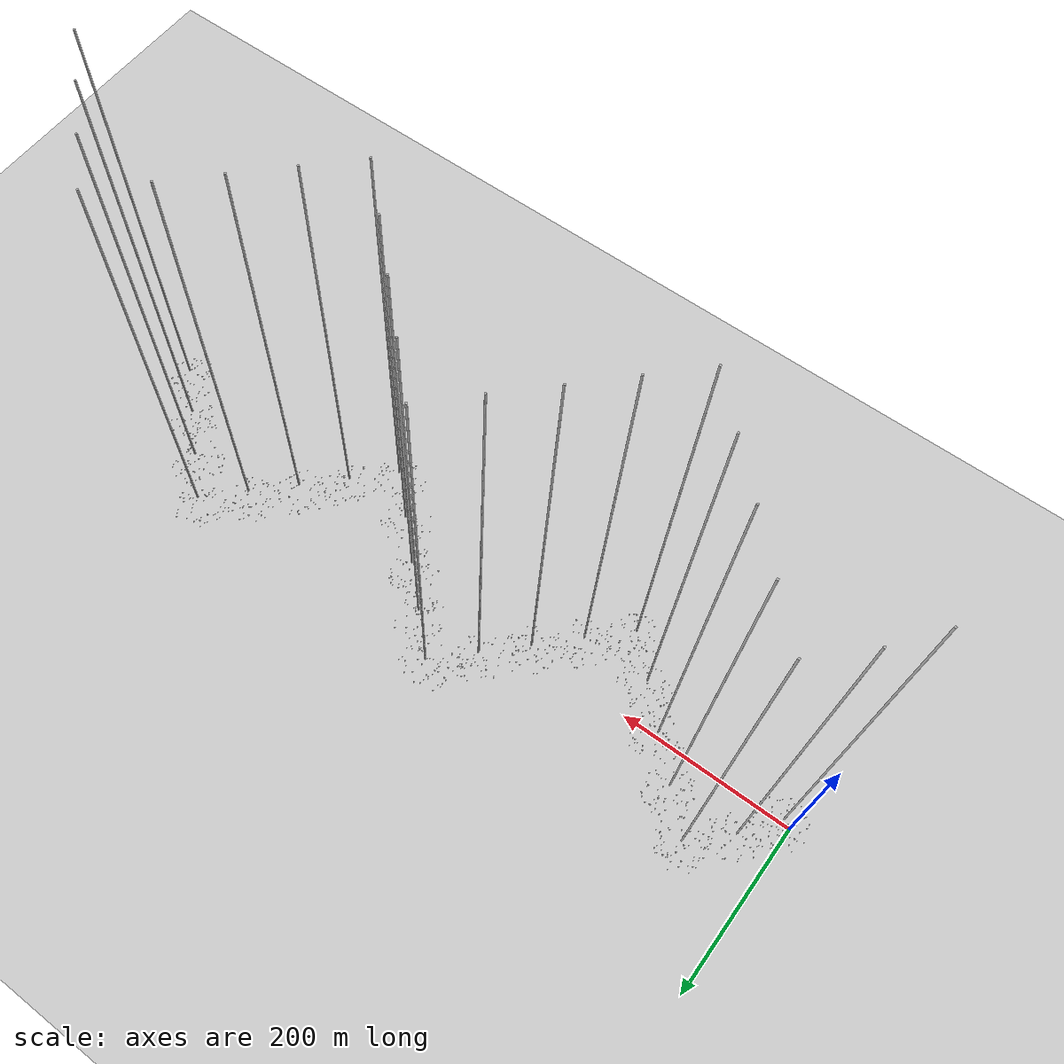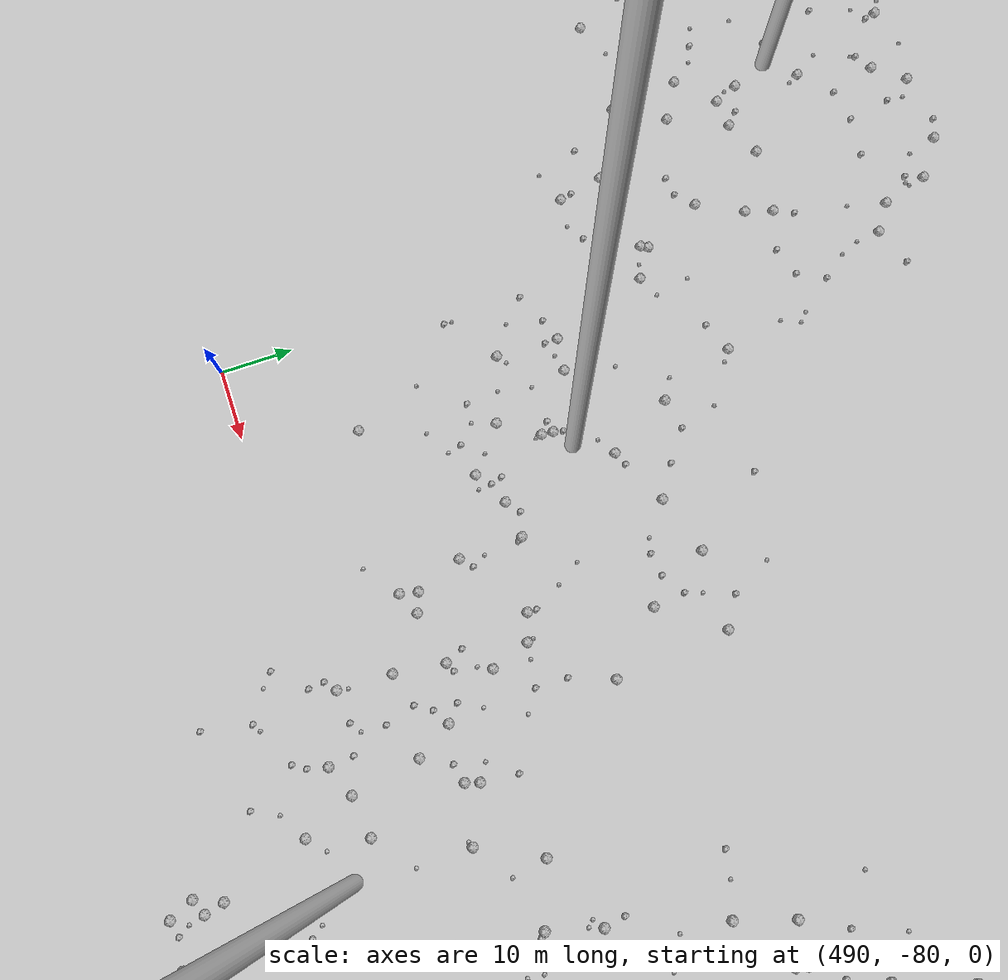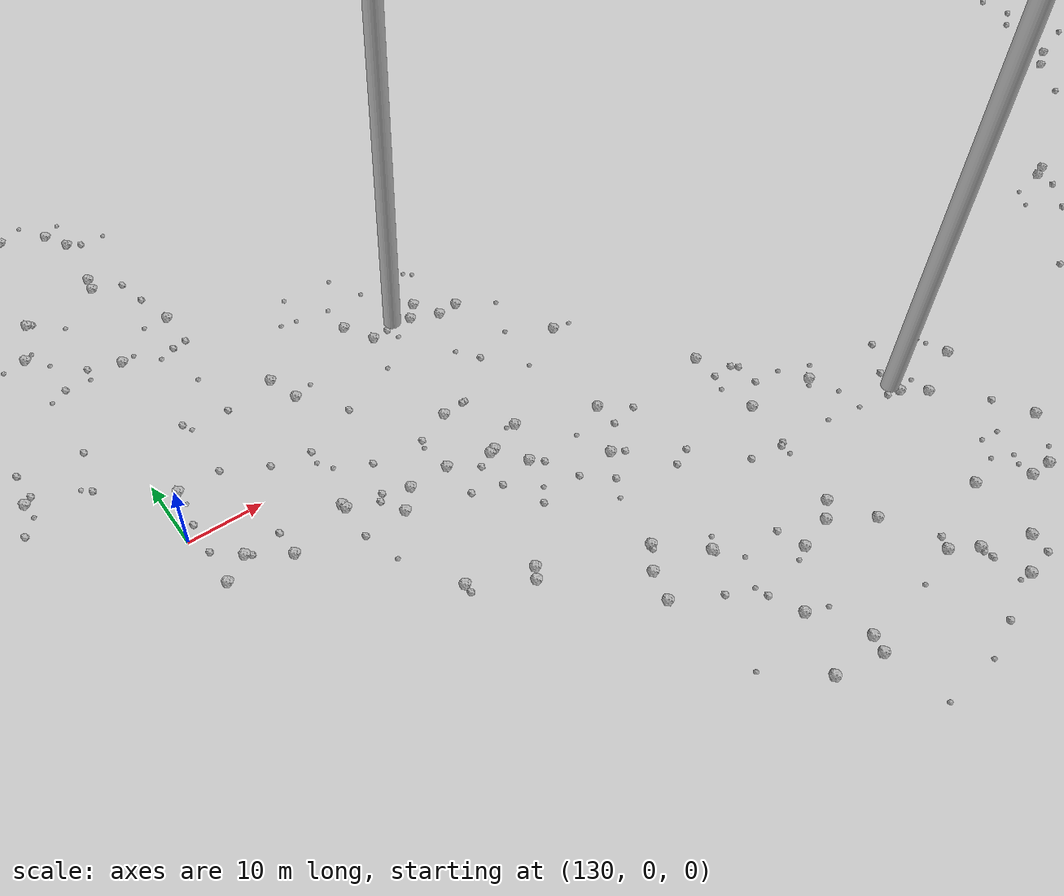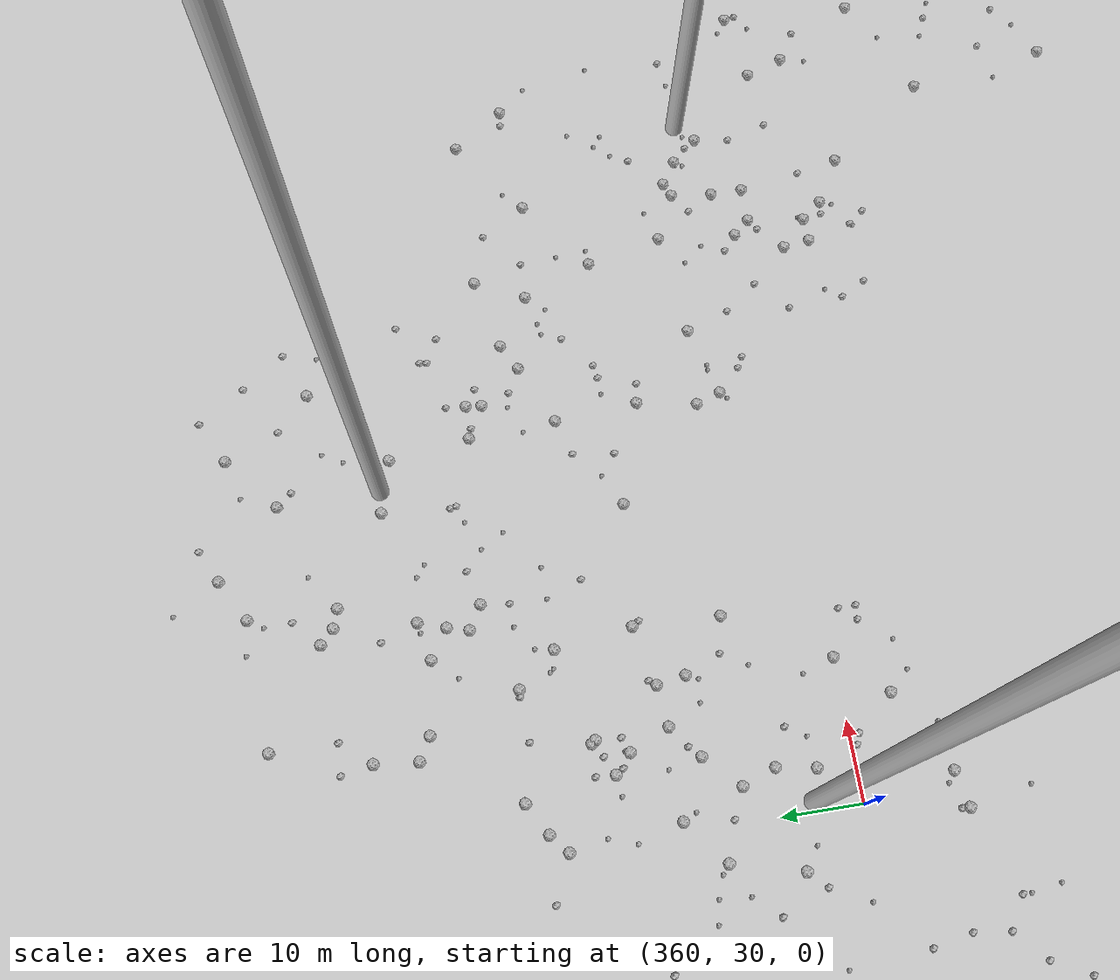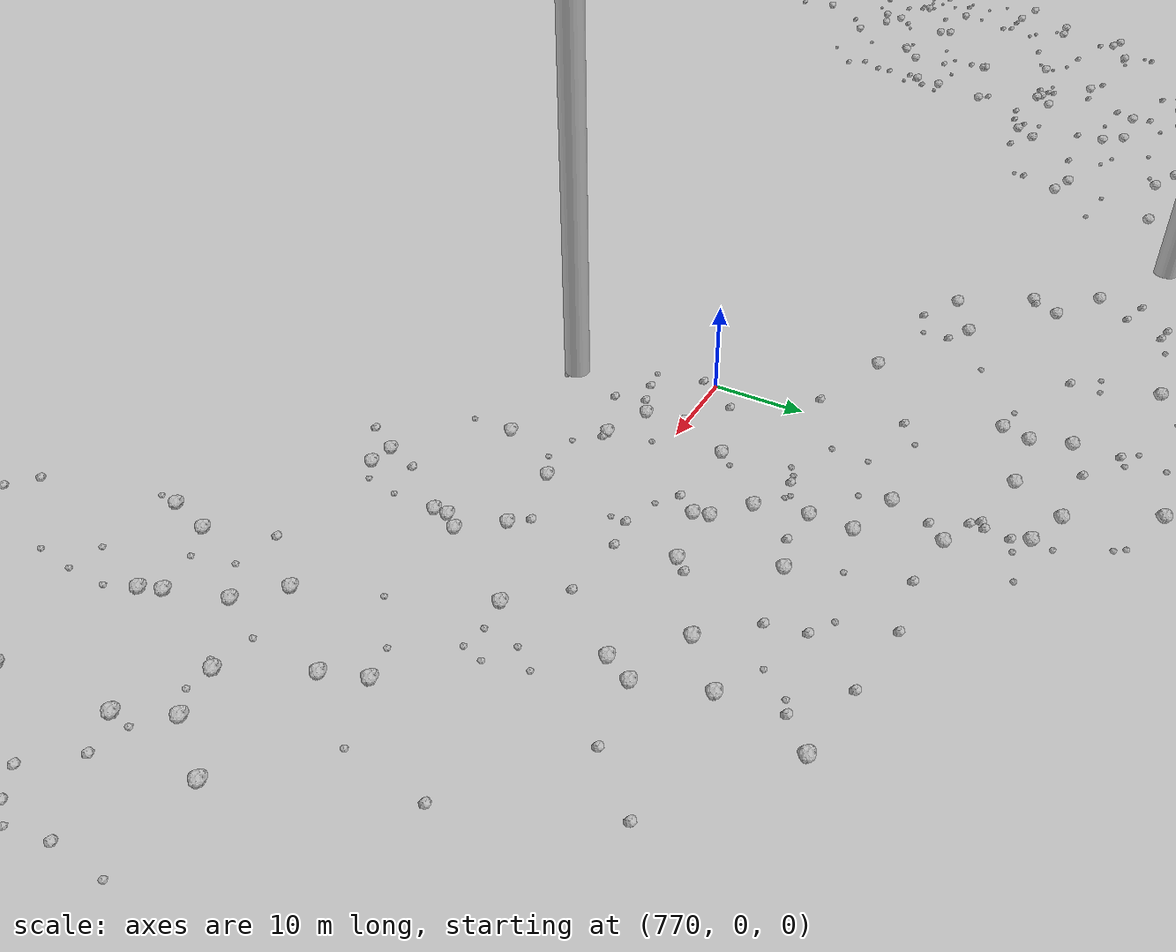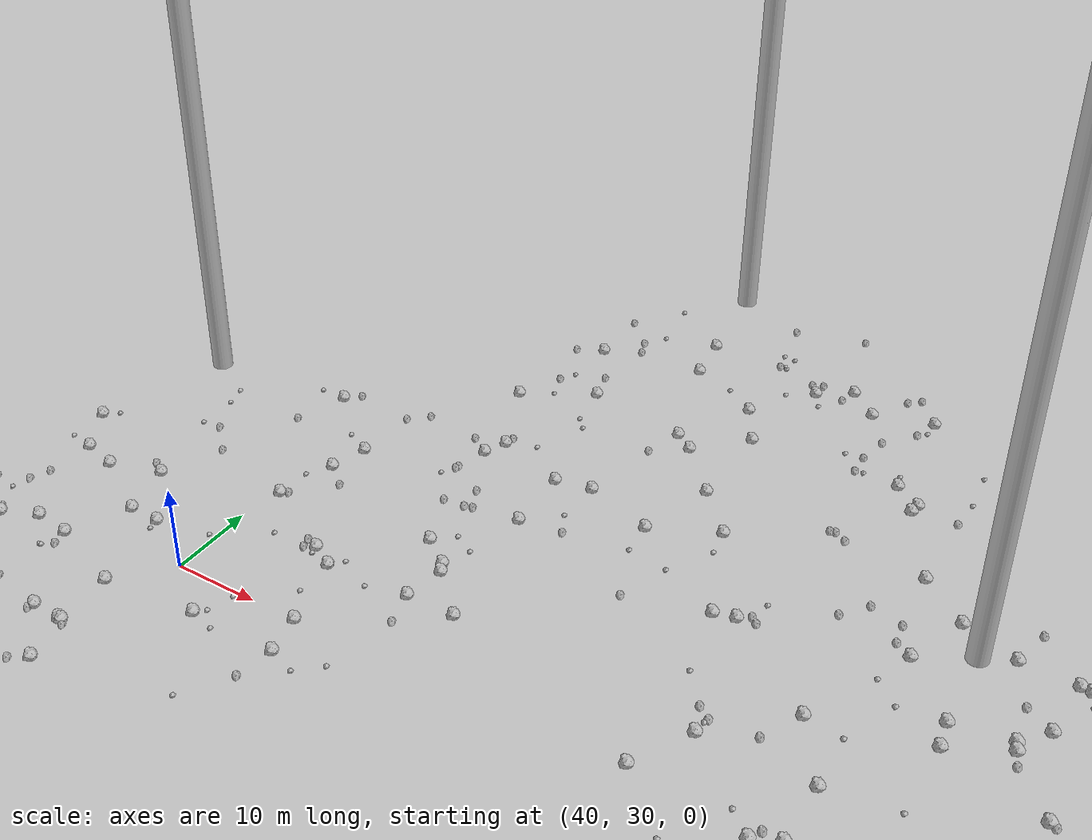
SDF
<sdf version="1.6">
 <world name="default">
  <include><uri>model://custom_ground</uri></include>
  <include><uri>model://sun</uri></include>
  <spherical_coordinates>
   <surface_model>EARTH_WGS84</surface_model>
   <latitude_deg>38.161479</latitude_deg>
   <longitude_deg>-122.454630</longitude_deg>
   <elevation>488.0</elevation>
   <heading_deg>90</heading_deg>
  </spherical_coordinates>
  <model name="rock1_0_0">
   <include><uri>model://rock1</uri><pose>17.490028786285016 0.2157174380187037 0.5 0 0 0</pose></include>
  </model>
  <model name="rock1_0_1">
   <include><uri>model://rock1</uri><pose>15.552308133637752 7.2812238678802785 0.5 0 0 0</pose></include>
  </model>
  <model name="rock1_0_2">
   <include><uri>model://rock1</uri><pose>-13.959517511296122 -16.448169961687878 0.5 0 0 0</pose></include>
  </model>
  <model name="rock1_0_3">
   <include><uri>model://rock1</uri><pose>-6.426104290065439 -19.773282048067323 0.5 0 0 0</pose></include>
  </model>
  <model name="rock1_0_4">
   <include><uri>model://rock1</uri><pose>-10.513384329000337 -3.477229423615217 0.5 0 0 0</pose></include>
  </model>
  <model name="rock1_0_5">
   <include><uri>model://rock1</uri><pose>34.9281571525718 4.83818163028905 0.5 0 0 0</pose></include>
  </model>
  <model name="rock1_0_6">
   <include><uri>model://rock1</uri><pose>-7.565671494527473 -21.202897996814464 0.5 0 0 0</pose></include>
  </model>
  <model name="rock1_0_7">
   <include><uri>model://rock1</uri><pose>31.737882586892837 17.3375868947572 0.5 0 0 0</pose></include>
  </model>
  <model name="rock1_0_8">
   <include><uri>model://rock1</uri><pose>12.695304742194729 18.15922169417653 0.5 0 0 0</pose></include>
  </model>
  <model name="rock1_0_9">
   <include><uri>model://rock1</uri><pose>-0.8341045443754744 6.677433893174474 0.5 0 0 0</pose></include>
  </model>
  <model name="rock1_0_10">
   <include><uri>model://rock1</uri><pose>4.318443628732329 23.02352458215067 0.5 0 0 0</pose></include>
  </model>
  <model name="rock1_0_11">
   <include><uri>model://rock1</uri><pose>-3.569362383473706 -7.1826873025046645 0.5 0 0 0</pose></include>
  </model>
  <model name="rock1_0_12">
   <include><uri>model://rock1</uri><pose>-13.767106848626367 17.734528653284357 0.5 0 0 0</pose></include>
  </model>
  <model name="rock1_0_13">
   <include><uri>model://rock1</uri><pose>-14.600755058833219 -11.815113729951175 0.5 0 0 0</pose></include>
  </model>
  <model name="rock1_0_14">
   <include><uri>model://rock1</uri><pose>6.7811659401622 22.473136450543258 0.5 0 0 0</pose></include>
  </model>
  <model name="rock1_0_15">
   <include><uri>model://rock1</uri><pose>-1.176387849155752 4.064066555425967 0.5 0 0 0</pose></include>
  </model>
  <model name="rock1_0_16">
   <include><uri>model://rock1</uri><pose>31.767623865012844 -0.0036093725433516965 0.5 0 0 0</pose></include>
  </model>
  <model name="rock1_0_17">
   <include><uri>model://rock1</uri><pose>-8.426478706242102 13.525920877029584 0.5 0 0 0</pose></include>
  </model>
  <model name="rock1_0_18">
   <include><uri>model://rock1</uri><pose>13.340647440166563 2.0593884351198355 0.5 0 0 0</pose></include>
  </model>
  <model name="rock1_0_19">
   <include><uri>model://rock1</uri><pose>11.24833495821025 -15.61057470901124 0.5 0 0 0</pose></include>
  </model>
  <model name="rock1_0_20">
   <include><uri>model://rock1</uri><pose>32.90035047088615 -16.819939998485275 0.5 0 0 0</pose></include>
  </model>
  <model name="rock1_0_21">
   <include><uri>model://rock1</uri><pose>25.226047405222083 -9.812946747274715 0.5 0 0 0</pose></include>
  </model>
  <model name="rock1_0_22">
   <include><uri>model://rock1</uri><pose>24.703914158098655 9.235450460300605 0.5 0 0 0</pose></include>
  </model>
  <model name="rock1_0_23">
   <include><uri>model://rock1</uri><pose>-9.721085314457332 4.894665270507232 0.5 0 0 0</pose></include>
  </model>
  <model name="rock1_0_24">
   <include><uri>model://rock1</uri><pose>23.266448646647703 1.7394043263250687 0.5 0 0 0</pose></include>
  </model>
  <model name="rock1_0_25">
   <include><uri>model://rock1</uri><pose>2.6724752828405123 -4.243457842265791 0.5 0 0 0</pose></include>
  </model>
  <model name="rock1_0_26">
   <include><uri>model://rock1</uri><pose>14.528146438450719 -28.95028437905785 0.5 0 0 0</pose></include>
  </model>
  <model name="rock2_0_0">
   <include><uri>model://rock2</uri><pose>21.772111254898228 13.600756680236472 0.3 0 0 0</pose></include>
  </model>
  <model name="rock2_0_1">
   <include><uri>model://rock2</uri><pose>14.663452946699351 -8.969330207973282 0.3 0 0 0</pose></include>
  </model>
  <model name="rock2_0_2">
   <include><uri>model://rock2</uri><pose>8.529473537914143 6.467718676867854 0.3 0 0 0</pose></include>
  </model>
  <model name="rock2_0_3">
   <include><uri>model://rock2</uri><pose>1.6079031754458626 -28.081586127538696 0.3 0 0 0</pose></include>
  </model>
  <model name="rock2_0_4">
   <include><uri>model://rock2</uri><pose>21.49086262873253 1.6072208820885479 0.3 0 0 0</pose></include>
  </model>
  <model name="rock2_0_5">
   <include><uri>model://rock2</uri><pose>3.249894448757857 26.474559433890953 0.3 0 0 0</pose></include>
  </model>
  <model name="rock2_0_6">
   <include><uri>model://rock2</uri><pose>0.4247086435552916 22.52104939537066 0.3 0 0 0</pose></include>
  </model>
  <model name="rock2_0_7">
   <include><uri>model://rock2</uri><pose>-11.058804746651562 -4.449608064901174 0.3 0 0 0</pose></include>
  </model>
  <model name="rock2_0_8">
   <include><uri>model://rock2</uri><pose>-9.253338144996535 -21.945245722285307 0.3 0 0 0</pose></include>
  </model>
  <model name="rock2_0_9">
   <include><uri>model://rock2</uri><pose>35.26114516598928 10.42156588927692 0.3 0 0 0</pose></include>
  </model>
  <model name="rock2_0_10">
   <include><uri>model://rock2</uri><pose>-14.91739128915076 13.1311883223729 0.3 0 0 0</pose></include>
  </model>
  <model name="rock2_0_11">
   <include><uri>model://rock2</uri><pose>8.928657171089132 -15.948631528100243 0.3 0 0 0</pose></include>
  </model>
  <model name="rock2_0_12">
   <include><uri>model://rock2</uri><pose>19.245222391107248 -1.425029726743098 0.3 0 0 0</pose></include>
  </model>
  <model name="rock2_0_13">
   <include><uri>model://rock2</uri><pose>11.50659969699523 5.330701066742542 0.3 0 0 0</pose></include>
  </model>
  <model name="rock2_0_14">
   <include><uri>model://rock2</uri><pose>13.501333065897413 -11.617174336484116 0.3 0 0 0</pose></include>
  </model>
  <model name="rock2_0_15">
   <include><uri>model://rock2</uri><pose>4.172303287446944 10.923406980248117 0.3 0 0 0</pose></include>
  </model>
  <model name="rock2_0_16">
   <include><uri>model://rock2</uri><pose>14.08243281720869 21.668331744075985 0.3 0 0 0</pose></include>
  </model>
  <model name="rock2_0_17">
   <include><uri>model://rock2</uri><pose>5.018882316853507 27.320691506718298 0.3 0 0 0</pose></include>
  </model>
  <model name="rock2_0_18">
   <include><uri>model://rock2</uri><pose>-1.724356932800923 -12.837849766764133 0.3 0 0 0</pose></include>
  </model>
  <model name="rock2_0_19">
   <include><uri>model://rock2</uri><pose>22.508345685757348 -20.946243619046932 0.3 0 0 0</pose></include>
  </model>
  <model name="rock2_0_20">
   <include><uri>model://rock2</uri><pose>24.40505440110659 -18.890016368429905 0.3 0 0 0</pose></include>
  </model>
  <model name="rock2_0_21">
   <include><uri>model://rock2</uri><pose>14.525786734457974 13.133107457313486 0.3 0 0 0</pose></include>
  </model>
  <model name="rock2_0_22">
   <include><uri>model://rock2</uri><pose>15.721531008282824 13.931231923244844 0.3 0 0 0</pose></include>
  </model>
  <model name="rock2_0_23">
   <include><uri>model://rock2</uri><pose>-2.4727630085940397 -12.644099898071207 0.3 0 0 0</pose></include>
  </model>
  <model name="rock2_0_24">
   <include><uri>model://rock2</uri><pose>20.56412871474995 -23.211723431182826 0.3 0 0 0</pose></include>
  </model>
  <model name="rock2_0_25">
   <include><uri>model://rock2</uri><pose>30.69739613234841 -17.57250051455209 0.3 0 0 0</pose></include>
  </model>
  <model name="rock2_0_26">
   <include><uri>model://rock2</uri><pose>13.02518508587881 -22.155175590378175 0.3 0 0 0</pose></include>
  </model>
  <model name="rock3_0_0">
   <include><uri>model://rock3</uri><pose>4.068485069165327 4.711863552902287 0.2 0 0 0</pose></include>
  </model>
  <model name="rock3_0_1">
   <include><uri>model://rock3</uri><pose>0.2976206375957844 12.356434172589893 0.2 0 0 0</pose></include>
  </model>
  <model name="rock3_0_2">
   <include><uri>model://rock3</uri><pose>-5.087694941448117 6.295776966280016 0.2 0 0 0</pose></include>
  </model>
  <model name="rock3_0_3">
   <include><uri>model://rock3</uri><pose>37.52687665882146 -8.011556580598647 0.2 0 0 0</pose></include>
  </model>
  <model name="rock3_0_4">
   <include><uri>model://rock3</uri><pose>8.643608142245032 3.8461926543505456 0.2 0 0 0</pose></include>
  </model>
  <model name="rock3_0_5">
   <include><uri>model://rock3</uri><pose>23.281007262254377 14.626748347326512 0.2 0 0 0</pose></include>
  </model>
  <model name="rock3_0_6">
   <include><uri>model://rock3</uri><pose>25.042160134183447 13.464831464630713 0.2 0 0 0</pose></include>
  </model>
  <model name="rock3_0_7">
   <include><uri>model://rock3</uri><pose>-11.922377867677385 6.519547826876149 0.2 0 0 0</pose></include>
  </model>
  <model name="rock3_0_8">
   <include><uri>model://rock3</uri><pose>35.54081393427688 -1.43126094069369 0.2 0 0 0</pose></include>
  </model>
  <model name="rock3_0_9">
   <include><uri>model://rock3</uri><pose>31.907394233141254 4.603401516512932 0.2 0 0 0</pose></include>
  </model>
  <model name="rock3_0_10">
   <include><uri>model://rock3</uri><pose>6.089348409005645 11.475223032600702 0.2 0 0 0</pose></include>
  </model>
  <model name="rock3_0_11">
   <include><uri>model://rock3</uri><pose>-12.433949047966822 5.211461592678887 0.2 0 0 0</pose></include>
  </model>
  <model name="rock3_0_12">
   <include><uri>model://rock3</uri><pose>1.1441449617343515 23.729280165929907 0.2 0 0 0</pose></include>
  </model>
  <model name="rock3_0_13">
   <include><uri>model://rock3</uri><pose>8.939085048594745 -26.01675700803327 0.2 0 0 0</pose></include>
  </model>
  <model name="rock3_0_14">
   <include><uri>model://rock3</uri><pose>-11.38018504175973 16.111687799507166 0.2 0 0 0</pose></include>
  </model>
  <model name="rock3_0_15">
   <include><uri>model://rock3</uri><pose>17.136206233262286 9.663345432479993 0.2 0 0 0</pose></include>
  </model>
  <model name="rock3_0_16">
   <include><uri>model://rock3</uri><pose>9.71073921494003 -4.59159375576742 0.2 0 0 0</pose></include>
  </model>
  <model name="rock3_0_17">
   <include><uri>model://rock3</uri><pose>-2.4616199577286153 -19.709025348964822 0.2 0 0 0</pose></include>
  </model>
  <model name="rock3_0_18">
   <include><uri>model://rock3</uri><pose>19.921413909897325 8.25058237603647 0.2 0 0 0</pose></include>
  </model>
  <model name="rock3_0_19">
   <include><uri>model://rock3</uri><pose>-14.29035473922906 -6.977904717782074 0.2 0 0 0</pose></include>
  </model>
  <model name="rock3_0_20">
   <include><uri>model://rock3</uri><pose>16.234752611833358 7.406225383889179 0.2 0 0 0</pose></include>
  </model>
  <model name="rock3_0_21">
   <include><uri>model://rock3</uri><pose>22.606657621859497 -5.32138233832999 0.2 0 0 0</pose></include>
  </model>
  <model name="rock3_0_22">
   <include><uri>model://rock3</uri><pose>25.11352040744753 24.53178515245842 0.2 0 0 0</pose></include>
  </model>
  <model name="rock3_0_23">
   <include><uri>model://rock3</uri><pose>-19.53339922470334 2.519710155780558 0.2 0 0 0</pose></include>
  </model>
  <model name="rock3_0_24">
   <include><uri>model://rock3</uri><pose>14.962230008112527 -23.00464837645273 0.2 0 0 0</pose></include>
  </model>
  <model name="rock3_0_25">
   <include><uri>model://rock3</uri><pose>18.102643327540136 -28.52378031608429 0.2 0 0 0</pose></include>
  </model>
  <model name="rock3_0_26">
   <include><uri>model://rock3</uri><pose>12.129043558374605 27.649488212764076 0.2 0 0 0</pose></include>
  </model>
  <model name="rock1_1_0">
   <include><uri>model://rock1</uri><pose>43.04939904285983 52.165143555207564 0.5 0 0 0</pose></include>
  </model>
  <model name="rock1_1_1">
   <include><uri>model://rock1</uri><pose>63.10372433862837 38.905339031747545 0.5 0 0 0</pose></include>
  </model>
  <model name="rock1_1_2">
   <include><uri>model://rock1</uri><pose>56.66217662388797 25.07962388893815 0.5 0 0 0</pose></include>
  </model>
  <model name="rock1_1_3">
   <include><uri>model://rock1</uri><pose>13.559171662539345 45.56450429360213 0.5 0 0 0</pose></include>
  </model>
  <model name="rock1_1_4">
   <include><uri>model://rock1</uri><pose>35.777343030951386 63.69646556772471 0.5 0 0 0</pose></include>
  </model>
  <model name="rock1_1_5">
   <include><uri>model://rock1</uri><pose>44.25253116629042 56.59244565744461 0.5 0 0 0</pose></include>
  </model>
  <model name="rock1_1_6">
   <include><uri>model://rock1</uri><pose>50.389460621869105 39.9590995627274 0.5 0 0 0</pose></include>
  </model>
  <model name="rock1_1_7">
   <include><uri>model://rock1</uri><pose>53.223021998179604 38.32540342047453 0.5 0 0 0</pose></include>
  </model>
  <model name="rock1_1_8">
   <include><uri>model://rock1</uri><pose>63.913007157419116 43.79035885134314 0.5 0 0 0</pose></include>
  </model>
  <model name="rock1_1_9">
   <include><uri>model://rock1</uri><pose>17.293525569926356 26.12455366831152 0.5 0 0 0</pose></include>
  </model>
  <model name="rock1_1_10">
   <include><uri>model://rock1</uri><pose>16.897687086303044 40.06966126916212 0.5 0 0 0</pose></include>
  </model>
  <model name="rock1_1_11">
   <include><uri>model://rock1</uri><pose>29.134543728627314 34.237546121603934 0.5 0 0 0</pose></include>
  </model>
  <model name="rock1_1_12">
   <include><uri>model://rock1</uri><pose>63.30301934821288 44.942030633653246 0.5 0 0 0</pose></include>
  </model>
  <model name="rock1_1_13">
   <include><uri>model://rock1</uri><pose>46.257953356447395 25.138945574804126 0.5 0 0 0</pose></include>
  </model>
  <model name="rock1_1_14">
   <include><uri>model://rock1</uri><pose>59.93804548444736 47.50132848026942 0.5 0 0 0</pose></include>
  </model>
  <model name="rock1_1_15">
   <include><uri>model://rock1</uri><pose>35.39685372994797 17.196871969438302 0.5 0 0 0</pose></include>
  </model>
  <model name="rock1_1_16">
   <include><uri>model://rock1</uri><pose>55.58267879443557 29.861527682574128 0.5 0 0 0</pose></include>
  </model>
  <model name="rock1_1_17">
   <include><uri>model://rock1</uri><pose>21.41207714680223 27.904672595719873 0.5 0 0 0</pose></include>
  </model>
  <model name="rock1_1_18">
   <include><uri>model://rock1</uri><pose>35.76101415385686 17.14085093616692 0.5 0 0 0</pose></include>
  </model>
  <model name="rock1_1_19">
   <include><uri>model://rock1</uri><pose>32.94846628138138 34.09686381037635 0.5 0 0 0</pose></include>
  </model>
  <model name="rock1_1_20">
   <include><uri>model://rock1</uri><pose>35.16434306107877 23.98643687993703 0.5 0 0 0</pose></include>
  </model>
  <model name="rock1_1_21">
   <include><uri>model://rock1</uri><pose>27.34757794848829 40.783543545974055 0.5 0 0 0</pose></include>
  </model>
  <model name="rock1_1_22">
   <include><uri>model://rock1</uri><pose>21.23571962756584 38.88762606214891 0.5 0 0 0</pose></include>
  </model>
  <model name="rock1_1_23">
   <include><uri>model://rock1</uri><pose>68.85157558163597 38.95200979291806 0.5 0 0 0</pose></include>
  </model>
  <model name="rock1_1_24">
   <include><uri>model://rock1</uri><pose>41.104101312538 45.14959669395413 0.5 0 0 0</pose></include>
  </model>
  <model name="rock1_1_25">
   <include><uri>model://rock1</uri><pose>37.170551027082524 11.726235356247475 0.5 0 0 0</pose></include>
  </model>
  <model name="rock1_1_26">
   <include><uri>model://rock1</uri><pose>25.894341372575116 27.301896347440856 0.5 0 0 0</pose></include>
  </model>
  <model name="rock2_1_0">
   <include><uri>model://rock2</uri><pose>64.09788415157412 34.931356195809705 0.3 0 0 0</pose></include>
  </model>
  <model name="rock2_1_1">
   <include><uri>model://rock2</uri><pose>45.79506151505739 49.93199872671477 0.3 0 0 0</pose></include>
  </model>
  <model name="rock2_1_2">
   <include><uri>model://rock2</uri><pose>46.895515637922074 66.23967967353431 0.3 0 0 0</pose></include>
  </model>
  <model name="rock2_1_3">
   <include><uri>model://rock2</uri><pose>55.15412917234031 59.94113228486747 0.3 0 0 0</pose></include>
  </model>
  <model name="rock2_1_4">
   <include><uri>model://rock2</uri><pose>44.75567388633665 64.25856758342417 0.3 0 0 0</pose></include>
  </model>
  <model name="rock2_1_5">
   <include><uri>model://rock2</uri><pose>60.71558142502013 54.534993795982004 0.3 0 0 0</pose></include>
  </model>
  <model name="rock2_1_6">
   <include><uri>model://rock2</uri><pose>25.664180232818556 41.84888193905567 0.3 0 0 0</pose></include>
  </model>
  <model name="rock2_1_7">
   <include><uri>model://rock2</uri><pose>41.87316738208037 45.73196816024003 0.3 0 0 0</pose></include>
  </model>
  <model name="rock2_1_8">
   <include><uri>model://rock2</uri><pose>25.212862825798574 18.604861133709086 0.3 0 0 0</pose></include>
  </model>
  <model name="rock2_1_9">
   <include><uri>model://rock2</uri><pose>55.04166882602959 59.53304352818768 0.3 0 0 0</pose></include>
  </model>
  <model name="rock2_1_10">
   <include><uri>model://rock2</uri><pose>26.346601179602224 25.39614493615941 0.3 0 0 0</pose></include>
  </model>
  <model name="rock2_1_11">
   <include><uri>model://rock2</uri><pose>33.67790252219696 57.483527770275415 0.3 0 0 0</pose></include>
  </model>
  <model name="rock2_1_12">
   <include><uri>model://rock2</uri><pose>12.065797082518754 30.46827404758998 0.3 0 0 0</pose></include>
  </model>
  <model name="rock2_1_13">
   <include><uri>model://rock2</uri><pose>16.510914937943358 34.25588876432562 0.3 0 0 0</pose></include>
  </model>
  <model name="rock2_1_14">
   <include><uri>model://rock2</uri><pose>55.953610346902856 20.605957873643902 0.3 0 0 0</pose></include>
  </model>
  <model name="rock2_1_15">
   <include><uri>model://rock2</uri><pose>27.102355674378053 51.06010095749527 0.3 0 0 0</pose></include>
  </model>
  <model name="rock2_1_16">
   <include><uri>model://rock2</uri><pose>59.4219832360617 57.28374721419612 0.3 0 0 0</pose></include>
  </model>
  <model name="rock2_1_17">
   <include><uri>model://rock2</uri><pose>59.762783640833625 54.28124869657673 0.3 0 0 0</pose></include>
  </model>
  <model name="rock2_1_18">
   <include><uri>model://rock2</uri><pose>53.75282193481034 65.45068427866858 0.3 0 0 0</pose></include>
  </model>
  <model name="rock2_1_19">
   <include><uri>model://rock2</uri><pose>37.40517989578599 65.21267193643439 0.3 0 0 0</pose></include>
  </model>
  <model name="rock2_1_20">
   <include><uri>model://rock2</uri><pose>36.317012897549844 16.73006388324145 0.3 0 0 0</pose></include>
  </model>
  <model name="rock2_1_21">
   <include><uri>model://rock2</uri><pose>49.184028412576936 39.30768800654536 0.3 0 0 0</pose></include>
  </model>
  <model name="rock2_1_22">
   <include><uri>model://rock2</uri><pose>30.35412775916848 47.812252107529225 0.3 0 0 0</pose></include>
  </model>
  <model name="rock2_1_23">
   <include><uri>model://rock2</uri><pose>57.208200845577785 54.044989026360525 0.3 0 0 0</pose></include>
  </model>
  <model name="rock2_1_24">
   <include><uri>model://rock2</uri><pose>15.577425216882636 32.03424847178397 0.3 0 0 0</pose></include>
  </model>
  <model name="rock2_1_25">
   <include><uri>model://rock2</uri><pose>31.52588325782137 16.629802007546697 0.3 0 0 0</pose></include>
  </model>
  <model name="rock2_1_26">
   <include><uri>model://rock2</uri><pose>48.83322786153211 40.53359680817873 0.3 0 0 0</pose></include>
  </model>
  <model name="rock3_1_0">
   <include><uri>model://rock3</uri><pose>15.013815623263982 46.89823100916868 0.2 0 0 0</pose></include>
  </model>
  <model name="rock3_1_1">
   <include><uri>model://rock3</uri><pose>14.922638340520074 30.001207027603975 0.2 0 0 0</pose></include>
  </model>
  <model name="rock3_1_2">
   <include><uri>model://rock3</uri><pose>59.83292022775731 24.02740875749474 0.2 0 0 0</pose></include>
  </model>
  <model name="rock3_1_3">
   <include><uri>model://rock3</uri><pose>44.94641606890671 39.5034091231643 0.2 0 0 0</pose></include>
  </model>
  <model name="rock3_1_4">
   <include><uri>model://rock3</uri><pose>54.378029525622914 39.86099273314285 0.2 0 0 0</pose></include>
  </model>
  <model name="rock3_1_5">
   <include><uri>model://rock3</uri><pose>24.87452464674144 24.552374736685472 0.2 0 0 0</pose></include>
  </model>
  <model name="rock3_1_6">
   <include><uri>model://rock3</uri><pose>24.607324683657637 55.753986302431095 0.2 0 0 0</pose></include>
  </model>
  <model name="rock3_1_7">
   <include><uri>model://rock3</uri><pose>32.433642727389525 63.83410953351099 0.2 0 0 0</pose></include>
  </model>
  <model name="rock3_1_8">
   <include><uri>model://rock3</uri><pose>23.961108176538342 58.30401816452499 0.2 0 0 0</pose></include>
  </model>
  <model name="rock3_1_9">
   <include><uri>model://rock3</uri><pose>24.66032675585794 50.9088054030653 0.2 0 0 0</pose></include>
  </model>
  <model name="rock3_1_10">
   <include><uri>model://rock3</uri><pose>58.41695046666439 37.79586608578774 0.2 0 0 0</pose></include>
  </model>
  <model name="rock3_1_11">
   <include><uri>model://rock3</uri><pose>64.56054633914036 48.24294306555478 0.2 0 0 0</pose></include>
  </model>
  <model name="rock3_1_12">
   <include><uri>model://rock3</uri><pose>39.20677957895307 35.48641796946392 0.2 0 0 0</pose></include>
  </model>
  <model name="rock3_1_13">
   <include><uri>model://rock3</uri><pose>40.973245171793565 58.31113700460776 0.2 0 0 0</pose></include>
  </model>
  <model name="rock3_1_14">
   <include><uri>model://rock3</uri><pose>52.42205491670214 15.39031643270709 0.2 0 0 0</pose></include>
  </model>
  <model name="rock3_1_15">
   <include><uri>model://rock3</uri><pose>49.173057085441194 24.399032425677696 0.2 0 0 0</pose></include>
  </model>
  <model name="rock3_1_16">
   <include><uri>model://rock3</uri><pose>16.3304980352951 27.22257069451741 0.2 0 0 0</pose></include>
  </model>
  <model name="rock3_1_17">
   <include><uri>model://rock3</uri><pose>47.973187604295966 29.291326656166095 0.2 0 0 0</pose></include>
  </model>
  <model name="rock3_1_18">
   <include><uri>model://rock3</uri><pose>41.26854159796534 49.48335852915923 0.2 0 0 0</pose></include>
  </model>
  <model name="rock3_1_19">
   <include><uri>model://rock3</uri><pose>62.40070112449549 26.402599740735493 0.2 0 0 0</pose></include>
  </model>
  <model name="rock3_1_20">
   <include><uri>model://rock3</uri><pose>33.06191770934704 32.85645985021385 0.2 0 0 0</pose></include>
  </model>
  <model name="rock3_1_21">
   <include><uri>model://rock3</uri><pose>13.637656651823896 40.74849437072008 0.2 0 0 0</pose></include>
  </model>
  <model name="rock3_1_22">
   <include><uri>model://rock3</uri><pose>53.21468578692081 33.667522137212174 0.2 0 0 0</pose></include>
  </model>
  <model name="rock3_1_23">
   <include><uri>model://rock3</uri><pose>62.07583094650512 49.641241373761446 0.2 0 0 0</pose></include>
  </model>
  <model name="rock3_1_24">
   <include><uri>model://rock3</uri><pose>53.983546202552525 58.04372193252886 0.2 0 0 0</pose></include>
  </model>
  <model name="rock3_1_25">
   <include><uri>model://rock3</uri><pose>47.15584951205804 26.245321308853306 0.2 0 0 0</pose></include>
  </model>
  <model name="rock3_1_26">
   <include><uri>model://rock3</uri><pose>50.48670804221363 39.03876053375129 0.2 0 0 0</pose></include>
  </model>
  <model name="rock1_2_0">
   <include><uri>model://rock1</uri><pose>102.01697795245431 81.1311915098214 0.5 0 0 0</pose></include>
  </model>
  <model name="rock1_2_1">
   <include><uri>model://rock1</uri><pose>65.83562395569707 63.55698109422447 0.5 0 0 0</pose></include>
  </model>
  <model name="rock1_2_2">
   <include><uri>model://rock1</uri><pose>78.24569609603012 87.73870636951767 0.5 0 0 0</pose></include>
  </model>
  <model name="rock1_2_3">
   <include><uri>model://rock1</uri><pose>78.43326935246667 61.674915987674005 0.5 0 0 0</pose></include>
  </model>
  <model name="rock1_2_4">
   <include><uri>model://rock1</uri><pose>93.1955375875315 54.06646297649543 0.5 0 0 0</pose></include>
  </model>
  <model name="rock1_2_5">
   <include><uri>model://rock1</uri><pose>81.17691509051289 70.8915404015373 0.5 0 0 0</pose></include>
  </model>
  <model name="rock1_2_6">
   <include><uri>model://rock1</uri><pose>86.0207906205747 65.38051507400476 0.5 0 0 0</pose></include>
  </model>
  <model name="rock1_2_7">
   <include><uri>model://rock1</uri><pose>83.58442892825971 95.21230457309477 0.5 0 0 0</pose></include>
  </model>
  <model name="rock1_2_8">
   <include><uri>model://rock1</uri><pose>101.77627750045383 79.82749293584973 0.5 0 0 0</pose></include>
  </model>
  <model name="rock1_2_9">
   <include><uri>model://rock1</uri><pose>90.77906875415928 53.438755864083404 0.5 0 0 0</pose></include>
  </model>
  <model name="rock1_2_10">
   <include><uri>model://rock1</uri><pose>75.84048645983238 77.03124619271762 0.5 0 0 0</pose></include>
  </model>
  <model name="rock1_2_11">
   <include><uri>model://rock1</uri><pose>91.10085951349679 94.6642925059631 0.5 0 0 0</pose></include>
  </model>
  <model name="rock1_2_12">
   <include><uri>model://rock1</uri><pose>56.18016111598383 63.752718230210576 0.5 0 0 0</pose></include>
  </model>
  <model name="rock1_2_13">
   <include><uri>model://rock1</uri><pose>68.56665128019569 98.26656600564394 0.5 0 0 0</pose></include>
  </model>
  <model name="rock1_2_14">
   <include><uri>model://rock1</uri><pose>81.17216729894852 82.51007507231431 0.5 0 0 0</pose></include>
  </model>
  <model name="rock1_2_15">
   <include><uri>model://rock1</uri><pose>98.83811932874849 83.3013974113104 0.5 0 0 0</pose></include>
  </model>
  <model name="rock1_2_16">
   <include><uri>model://rock1</uri><pose>57.32381390283977 66.47735250999837 0.5 0 0 0</pose></include>
  </model>
  <model name="rock1_2_17">
   <include><uri>model://rock1</uri><pose>73.44226290575352 78.78005666192831 0.5 0 0 0</pose></include>
  </model>
  <model name="rock1_2_18">
   <include><uri>model://rock1</uri><pose>69.38275285777341 92.06970171161782 0.5 0 0 0</pose></include>
  </model>
  <model name="rock1_2_19">
   <include><uri>model://rock1</uri><pose>61.20913235286024 80.84933146585098 0.5 0 0 0</pose></include>
  </model>
  <model name="rock1_2_20">
   <include><uri>model://rock1</uri><pose>66.18761885179957 55.405977918329285 0.5 0 0 0</pose></include>
  </model>
  <model name="rock1_2_21">
   <include><uri>model://rock1</uri><pose>57.07857924560517 89.72526831208646 0.5 0 0 0</pose></include>
  </model>
  <model name="rock1_2_22">
   <include><uri>model://rock1</uri><pose>107.16599434582542 69.99739722369318 0.5 0 0 0</pose></include>
  </model>
  <model name="rock1_2_23">
   <include><uri>model://rock1</uri><pose>53.14927061072265 75.98691294962788 0.5 0 0 0</pose></include>
  </model>
  <model name="rock1_2_24">
   <include><uri>model://rock1</uri><pose>70.164915968616 64.40159785795436 0.5 0 0 0</pose></include>
  </model>
  <model name="rock1_2_25">
   <include><uri>model://rock1</uri><pose>98.0842370755309 96.77250258927296 0.5 0 0 0</pose></include>
  </model>
  <model name="rock1_2_26">
   <include><uri>model://rock1</uri><pose>87.47699865011091 97.88162516171926 0.5 0 0 0</pose></include>
  </model>
  <model name="rock2_2_0">
   <include><uri>model://rock2</uri><pose>72.01806369438974 74.16995984108273 0.3 0 0 0</pose></include>
  </model>
  <model name="rock2_2_1">
   <include><uri>model://rock2</uri><pose>83.70647189714995 97.32331914005593 0.3 0 0 0</pose></include>
  </model>
  <model name="rock2_2_2">
   <include><uri>model://rock2</uri><pose>106.85953286193458 80.52781502990148 0.3 0 0 0</pose></include>
  </model>
  <model name="rock2_2_3">
   <include><uri>model://rock2</uri><pose>95.05946256410971 100.69860760937038 0.3 0 0 0</pose></include>
  </model>
  <model name="rock2_2_4">
   <include><uri>model://rock2</uri><pose>86.81635821639206 95.71105361944211 0.3 0 0 0</pose></include>
  </model>
  <model name="rock2_2_5">
   <include><uri>model://rock2</uri><pose>55.64927430905111 81.4068995045185 0.3 0 0 0</pose></include>
  </model>
  <model name="rock2_2_6">
   <include><uri>model://rock2</uri><pose>75.79492022676382 106.85570945752282 0.3 0 0 0</pose></include>
  </model>
  <model name="rock2_2_7">
   <include><uri>model://rock2</uri><pose>57.55143040790323 67.75745577779972 0.3 0 0 0</pose></include>
  </model>
  <model name="rock2_2_8">
   <include><uri>model://rock2</uri><pose>82.48053816680597 96.80194587878954 0.3 0 0 0</pose></include>
  </model>
  <model name="rock2_2_9">
   <include><uri>model://rock2</uri><pose>93.47509971804493 86.30630706181044 0.3 0 0 0</pose></include>
  </model>
  <model name="rock2_2_10">
   <include><uri>model://rock2</uri><pose>94.19625590741538 90.15119317517552 0.3 0 0 0</pose></include>
  </model>
  <model name="rock2_2_11">
   <include><uri>model://rock2</uri><pose>101.70251155547257 60.167361177822556 0.3 0 0 0</pose></include>
  </model>
  <model name="rock2_2_12">
   <include><uri>model://rock2</uri><pose>53.98679296676002 88.20959980048835 0.3 0 0 0</pose></include>
  </model>
  <model name="rock2_2_13">
   <include><uri>model://rock2</uri><pose>93.72097282337849 99.46571722570874 0.3 0 0 0</pose></include>
  </model>
  <model name="rock2_2_14">
   <include><uri>model://rock2</uri><pose>77.38783308587962 98.4906655946568 0.3 0 0 0</pose></include>
  </model>
  <model name="rock2_2_15">
   <include><uri>model://rock2</uri><pose>71.28635418867225 56.16895690504134 0.3 0 0 0</pose></include>
  </model>
  <model name="rock2_2_16">
   <include><uri>model://rock2</uri><pose>81.55403005363243 50.798692870005944 0.3 0 0 0</pose></include>
  </model>
  <model name="rock2_2_17">
   <include><uri>model://rock2</uri><pose>97.601795361879 71.2971724859639 0.3 0 0 0</pose></include>
  </model>
  <model name="rock2_2_18">
   <include><uri>model://rock2</uri><pose>84.25771787320869 109.22145071417441 0.3 0 0 0</pose></include>
  </model>
  <model name="rock2_2_19">
   <include><uri>model://rock2</uri><pose>97.10172882034007 93.76453794956325 0.3 0 0 0</pose></include>
  </model>
  <model name="rock2_2_20">
   <include><uri>model://rock2</uri><pose>61.25804200287572 92.00088210467071 0.3 0 0 0</pose></include>
  </model>
  <model name="rock2_2_21">
   <include><uri>model://rock2</uri><pose>60.54882167818706 94.01245607630726 0.3 0 0 0</pose></include>
  </model>
  <model name="rock2_2_22">
   <include><uri>model://rock2</uri><pose>96.16052187809858 72.16210562274657 0.3 0 0 0</pose></include>
  </model>
  <model name="rock2_2_23">
   <include><uri>model://rock2</uri><pose>57.090628865678596 97.57093293607983 0.3 0 0 0</pose></include>
  </model>
  <model name="rock2_2_24">
   <include><uri>model://rock2</uri><pose>95.56384413712492 72.02715916297153 0.3 0 0 0</pose></include>
  </model>
  <model name="rock2_2_25">
   <include><uri>model://rock2</uri><pose>93.60621950709137 83.49669103739608 0.3 0 0 0</pose></include>
  </model>
  <model name="rock2_2_26">
   <include><uri>model://rock2</uri><pose>60.29261645784206 84.48185573091853 0.3 0 0 0</pose></include>
  </model>
  <model name="rock3_2_0">
   <include><uri>model://rock3</uri><pose>61.91667366105683 75.48720185399712 0.2 0 0 0</pose></include>
  </model>
  <model name="rock3_2_1">
   <include><uri>model://rock3</uri><pose>74.36821838114989 90.46901366100651 0.2 0 0 0</pose></include>
  </model>
  <model name="rock3_2_2">
   <include><uri>model://rock3</uri><pose>94.9462493850954 57.600810477399946 0.2 0 0 0</pose></include>
  </model>
  <model name="rock3_2_3">
   <include><uri>model://rock3</uri><pose>83.7762101900585 97.43783045512848 0.2 0 0 0</pose></include>
  </model>
  <model name="rock3_2_4">
   <include><uri>model://rock3</uri><pose>86.4677436396342 62.07432070503397 0.2 0 0 0</pose></include>
  </model>
  <model name="rock3_2_5">
   <include><uri>model://rock3</uri><pose>78.24430493774624 100.75473697647337 0.2 0 0 0</pose></include>
  </model>
  <model name="rock3_2_6">
   <include><uri>model://rock3</uri><pose>56.58019206149898 78.35574571396455 0.2 0 0 0</pose></include>
  </model>
  <model name="rock3_2_7">
   <include><uri>model://rock3</uri><pose>97.96606696324503 94.72206443074224 0.2 0 0 0</pose></include>
  </model>
  <model name="rock3_2_8">
   <include><uri>model://rock3</uri><pose>60.6757812435128 67.92118773816937 0.2 0 0 0</pose></include>
  </model>
  <model name="rock3_2_9">
   <include><uri>model://rock3</uri><pose>62.22109481920312 96.60746611247626 0.2 0 0 0</pose></include>
  </model>
  <model name="rock3_2_10">
   <include><uri>model://rock3</uri><pose>84.81540690533578 93.09130886818005 0.2 0 0 0</pose></include>
  </model>
  <model name="rock3_2_11">
   <include><uri>model://rock3</uri><pose>80.48795904087895 93.24770364338876 0.2 0 0 0</pose></include>
  </model>
  <model name="rock3_2_12">
   <include><uri>model://rock3</uri><pose>76.82904836613288 100.90068912842712 0.2 0 0 0</pose></include>
  </model>
  <model name="rock3_2_13">
   <include><uri>model://rock3</uri><pose>94.51627480981247 83.67682391879116 0.2 0 0 0</pose></include>
  </model>
  <model name="rock3_2_14">
   <include><uri>model://rock3</uri><pose>78.21715275003409 98.42502941481067 0.2 0 0 0</pose></include>
  </model>
  <model name="rock3_2_15">
   <include><uri>model://rock3</uri><pose>98.33582944929935 85.1591543258344 0.2 0 0 0</pose></include>
  </model>
  <model name="rock3_2_16">
   <include><uri>model://rock3</uri><pose>77.79227451243135 98.86138164557127 0.2 0 0 0</pose></include>
  </model>
  <model name="rock3_2_17">
   <include><uri>model://rock3</uri><pose>56.670129812512215 83.27144030278765 0.2 0 0 0</pose></include>
  </model>
  <model name="rock3_2_18">
   <include><uri>model://rock3</uri><pose>63.20456690928865 74.02091414290038 0.2 0 0 0</pose></include>
  </model>
  <model name="rock3_2_19">
   <include><uri>model://rock3</uri><pose>91.30462816093853 86.05066313076796 0.2 0 0 0</pose></include>
  </model>
  <model name="rock3_2_20">
   <include><uri>model://rock3</uri><pose>83.54459183262728 56.85868164882904 0.2 0 0 0</pose></include>
  </model>
  <model name="rock3_2_21">
   <include><uri>model://rock3</uri><pose>61.27397753125056 103.40863132861993 0.2 0 0 0</pose></include>
  </model>
  <model name="rock3_2_22">
   <include><uri>model://rock3</uri><pose>106.53181001306329 89.89685457023094 0.2 0 0 0</pose></include>
  </model>
  <model name="rock3_2_23">
   <include><uri>model://rock3</uri><pose>78.71332683186456 57.6140002984313 0.2 0 0 0</pose></include>
  </model>
  <model name="rock3_2_24">
   <include><uri>model://rock3</uri><pose>107.07050538281135 84.5342870598032 0.2 0 0 0</pose></include>
  </model>
  <model name="rock3_2_25">
   <include><uri>model://rock3</uri><pose>77.87886425619854 62.149035180952936 0.2 0 0 0</pose></include>
  </model>
  <model name="rock3_2_26">
   <include><uri>model://rock3</uri><pose>69.85409767881721 58.89901627146699 0.2 0 0 0</pose></include>
  </model>
  <model name="rock1_3_0">
   <include><uri>model://rock1</uri><pose>119.20190381701372 63.31436776401354 0.5 0 0 0</pose></include>
  </model>
  <model name="rock1_3_1">
   <include><uri>model://rock1</uri><pose>122.55488163029375 52.80213846238781 0.5 0 0 0</pose></include>
  </model>
  <model name="rock1_3_2">
   <include><uri>model://rock1</uri><pose>109.2788053096807 30.61693010563567 0.5 0 0 0</pose></include>
  </model>
  <model name="rock1_3_3">
   <include><uri>model://rock1</uri><pose>138.4561032635953 46.677584077831625 0.5 0 0 0</pose></include>
  </model>
  <model name="rock1_3_4">
   <include><uri>model://rock1</uri><pose>93.38738221165372 31.121656677759002 0.5 0 0 0</pose></include>
  </model>
  <model name="rock1_3_5">
   <include><uri>model://rock1</uri><pose>125.37741968955507 38.924983286875474 0.5 0 0 0</pose></include>
  </model>
  <model name="rock1_3_6">
   <include><uri>model://rock1</uri><pose>125.41708156152 63.09581123044831 0.5 0 0 0</pose></include>
  </model>
  <model name="rock1_3_7">
   <include><uri>model://rock1</uri><pose>116.77610489422669 48.440097740858526 0.5 0 0 0</pose></include>
  </model>
  <model name="rock1_3_8">
   <include><uri>model://rock1</uri><pose>124.98258618436233 55.798959792308814 0.5 0 0 0</pose></include>
  </model>
  <model name="rock1_3_9">
   <include><uri>model://rock1</uri><pose>116.21065876373649 51.74170111115523 0.5 0 0 0</pose></include>
  </model>
  <model name="rock1_3_10">
   <include><uri>model://rock1</uri><pose>109.21672757051849 37.97233526564476 0.5 0 0 0</pose></include>
  </model>
  <model name="rock1_3_11">
   <include><uri>model://rock1</uri><pose>139.27810555120635 57.46656453864076 0.5 0 0 0</pose></include>
  </model>
  <model name="rock1_3_12">
   <include><uri>model://rock1</uri><pose>131.43202572331177 63.469914542837735 0.5 0 0 0</pose></include>
  </model>
  <model name="rock1_3_13">
   <include><uri>model://rock1</uri><pose>128.0304499118144 45.093841978477556 0.5 0 0 0</pose></include>
  </model>
  <model name="rock1_3_14">
   <include><uri>model://rock1</uri><pose>144.6341138790009 35.36611866790395 0.5 0 0 0</pose></include>
  </model>
  <model name="rock1_3_15">
   <include><uri>model://rock1</uri><pose>96.86781871813419 37.9255675681566 0.5 0 0 0</pose></include>
  </model>
  <model name="rock1_3_16">
   <include><uri>model://rock1</uri><pose>116.1140914679859 16.214860660588165 0.5 0 0 0</pose></include>
  </model>
  <model name="rock1_3_17">
   <include><uri>model://rock1</uri><pose>137.37348109418957 60.91566613790188 0.5 0 0 0</pose></include>
  </model>
  <model name="rock1_3_18">
   <include><uri>model://rock1</uri><pose>126.65407473613024 62.90446150926534 0.5 0 0 0</pose></include>
  </model>
  <model name="rock1_3_19">
   <include><uri>model://rock1</uri><pose>107.1927127977753 16.190421546178726 0.5 0 0 0</pose></include>
  </model>
  <model name="rock1_3_20">
   <include><uri>model://rock1</uri><pose>135.98283468930896 31.156615002485374 0.5 0 0 0</pose></include>
  </model>
  <model name="rock1_3_21">
   <include><uri>model://rock1</uri><pose>104.48416047351445 45.29866112248001 0.5 0 0 0</pose></include>
  </model>
  <model name="rock1_3_22">
   <include><uri>model://rock1</uri><pose>138.79268366834742 48.763284814544484 0.5 0 0 0</pose></include>
  </model>
  <model name="rock1_3_23">
   <include><uri>model://rock1</uri><pose>110.10240817216817 58.18613977593648 0.5 0 0 0</pose></include>
  </model>
  <model name="rock1_3_24">
   <include><uri>model://rock1</uri><pose>112.76864990626729 65.49680913857509 0.5 0 0 0</pose></include>
  </model>
  <model name="rock1_3_25">
   <include><uri>model://rock1</uri><pose>122.91236391616809 51.754767154222 0.5 0 0 0</pose></include>
  </model>
  <model name="rock1_3_26">
   <include><uri>model://rock1</uri><pose>106.48325805804865 29.299149052298716 0.5 0 0 0</pose></include>
  </model>
  <model name="rock2_3_0">
   <include><uri>model://rock2</uri><pose>123.74068730414004 13.524699804970071 0.3 0 0 0</pose></include>
  </model>
  <model name="rock2_3_1">
   <include><uri>model://rock2</uri><pose>95.21938722647656 54.422369178634426 0.3 0 0 0</pose></include>
  </model>
  <model name="rock2_3_2">
   <include><uri>model://rock2</uri><pose>114.27923176931856 11.796292045810757 0.3 0 0 0</pose></include>
  </model>
  <model name="rock2_3_3">
   <include><uri>model://rock2</uri><pose>131.5281441265868 32.77228727228111 0.3 0 0 0</pose></include>
  </model>
  <model name="rock2_3_4">
   <include><uri>model://rock2</uri><pose>142.30538364988283 45.1813155922126 0.3 0 0 0</pose></include>
  </model>
  <model name="rock2_3_5">
   <include><uri>model://rock2</uri><pose>102.22677949959157 40.64212004612389 0.3 0 0 0</pose></include>
  </model>
  <model name="rock2_3_6">
   <include><uri>model://rock2</uri><pose>123.54462980556394 49.99953435465115 0.3 0 0 0</pose></include>
  </model>
  <model name="rock2_3_7">
   <include><uri>model://rock2</uri><pose>121.89034431173005 57.732332539193415 0.3 0 0 0</pose></include>
  </model>
  <model name="rock2_3_8">
   <include><uri>model://rock2</uri><pose>140.95366596598626 56.5519589245223 0.3 0 0 0</pose></include>
  </model>
  <model name="rock2_3_9">
   <include><uri>model://rock2</uri><pose>142.74069577649382 29.746074673308254 0.3 0 0 0</pose></include>
  </model>
  <model name="rock2_3_10">
   <include><uri>model://rock2</uri><pose>128.68921010417588 44.95566652623707 0.3 0 0 0</pose></include>
  </model>
  <model name="rock2_3_11">
   <include><uri>model://rock2</uri><pose>108.17081713212558 59.4365238268878 0.3 0 0 0</pose></include>
  </model>
  <model name="rock2_3_12">
   <include><uri>model://rock2</uri><pose>117.16661286870283 17.127762505336847 0.3 0 0 0</pose></include>
  </model>
  <model name="rock2_3_13">
   <include><uri>model://rock2</uri><pose>107.76316064205216 62.09677384495155 0.3 0 0 0</pose></include>
  </model>
  <model name="rock2_3_14">
   <include><uri>model://rock2</uri><pose>101.68930876729235 20.664944069168453 0.3 0 0 0</pose></include>
  </model>
  <model name="rock2_3_15">
   <include><uri>model://rock2</uri><pose>97.16569987773755 40.09585868482496 0.3 0 0 0</pose></include>
  </model>
  <model name="rock2_3_16">
   <include><uri>model://rock2</uri><pose>116.91124899560003 21.051273884712497 0.3 0 0 0</pose></include>
  </model>
  <model name="rock2_3_17">
   <include><uri>model://rock2</uri><pose>120.27925788038607 68.23048838388705 0.3 0 0 0</pose></include>
  </model>
  <model name="rock2_3_18">
   <include><uri>model://rock2</uri><pose>125.32146565971067 19.832289749742248 0.3 0 0 0</pose></include>
  </model>
  <model name="rock2_3_19">
   <include><uri>model://rock2</uri><pose>127.65227292761548 31.00526493537361 0.3 0 0 0</pose></include>
  </model>
  <model name="rock2_3_20">
   <include><uri>model://rock2</uri><pose>103.9401462450384 63.107489355296586 0.3 0 0 0</pose></include>
  </model>
  <model name="rock2_3_21">
   <include><uri>model://rock2</uri><pose>94.4630798402048 55.11666005718189 0.3 0 0 0</pose></include>
  </model>
  <model name="rock2_3_22">
   <include><uri>model://rock2</uri><pose>143.23096507053447 40.81306451384695 0.3 0 0 0</pose></include>
  </model>
  <model name="rock2_3_23">
   <include><uri>model://rock2</uri><pose>107.18958392032022 30.752245954282547 0.3 0 0 0</pose></include>
  </model>
  <model name="rock2_3_24">
   <include><uri>model://rock2</uri><pose>105.4435402157056 14.218645061250276 0.3 0 0 0</pose></include>
  </model>
  <model name="rock2_3_25">
   <include><uri>model://rock2</uri><pose>95.67913180311888 41.220956001668874 0.3 0 0 0</pose></include>
  </model>
  <model name="rock2_3_26">
   <include><uri>model://rock2</uri><pose>144.71702395254863 30.1038483343801 0.3 0 0 0</pose></include>
  </model>
  <model name="rock3_3_0">
   <include><uri>model://rock3</uri><pose>103.30739346073064 15.12793567234745 0.2 0 0 0</pose></include>
  </model>
  <model name="rock3_3_1">
   <include><uri>model://rock3</uri><pose>111.31294543605972 51.1896423679415 0.2 0 0 0</pose></include>
  </model>
  <model name="rock3_3_2">
   <include><uri>model://rock3</uri><pose>131.16622302352448 30.856240886593874 0.2 0 0 0</pose></include>
  </model>
  <model name="rock3_3_3">
   <include><uri>model://rock3</uri><pose>134.77535321826306 65.05719148270637 0.2 0 0 0</pose></include>
  </model>
  <model name="rock3_3_4">
   <include><uri>model://rock3</uri><pose>127.72870512426442 36.32100870540535 0.2 0 0 0</pose></include>
  </model>
  <model name="rock3_3_5">
   <include><uri>model://rock3</uri><pose>132.196691953509 41.69543089639334 0.2 0 0 0</pose></include>
  </model>
  <model name="rock3_3_6">
   <include><uri>model://rock3</uri><pose>137.68997763561276 31.540950363187687 0.2 0 0 0</pose></include>
  </model>
  <model name="rock3_3_7">
   <include><uri>model://rock3</uri><pose>122.06535901227943 38.57203498803814 0.2 0 0 0</pose></include>
  </model>
  <model name="rock3_3_8">
   <include><uri>model://rock3</uri><pose>103.79885834283395 31.6623792850851 0.2 0 0 0</pose></include>
  </model>
  <model name="rock3_3_9">
   <include><uri>model://rock3</uri><pose>99.77120787125648 25.088017384767223 0.2 0 0 0</pose></include>
  </model>
  <model name="rock3_3_10">
   <include><uri>model://rock3</uri><pose>96.93510833256896 39.59675995508867 0.2 0 0 0</pose></include>
  </model>
  <model name="rock3_3_11">
   <include><uri>model://rock3</uri><pose>116.25991263789179 13.920708233619944 0.2 0 0 0</pose></include>
  </model>
  <model name="rock3_3_12">
   <include><uri>model://rock3</uri><pose>108.4697248383028 53.70570323820289 0.2 0 0 0</pose></include>
  </model>
  <model name="rock3_3_13">
   <include><uri>model://rock3</uri><pose>141.1610974522222 35.48761204998597 0.2 0 0 0</pose></include>
  </model>
  <model name="rock3_3_14">
   <include><uri>model://rock3</uri><pose>127.31943374195455 61.047817602106704 0.2 0 0 0</pose></include>
  </model>
  <model name="rock3_3_15">
   <include><uri>model://rock3</uri><pose>106.85449083776147 19.544270889488182 0.2 0 0 0</pose></include>
  </model>
  <model name="rock3_3_16">
   <include><uri>model://rock3</uri><pose>116.84448908198488 39.33456981251079 0.2 0 0 0</pose></include>
  </model>
  <model name="rock3_3_17">
   <include><uri>model://rock3</uri><pose>126.46808938039737 39.74273906570485 0.2 0 0 0</pose></include>
  </model>
  <model name="rock3_3_18">
   <include><uri>model://rock3</uri><pose>108.80952949474427 44.717851711629336 0.2 0 0 0</pose></include>
  </model>
  <model name="rock3_3_19">
   <include><uri>model://rock3</uri><pose>140.54654906214844 28.842683309379687 0.2 0 0 0</pose></include>
  </model>
  <model name="rock3_3_20">
   <include><uri>model://rock3</uri><pose>139.68553042204138 62.48328540996482 0.2 0 0 0</pose></include>
  </model>
  <model name="rock3_3_21">
   <include><uri>model://rock3</uri><pose>144.4209768621737 56.54332845747229 0.2 0 0 0</pose></include>
  </model>
  <model name="rock3_3_22">
   <include><uri>model://rock3</uri><pose>92.60674822739564 44.971579365000984 0.2 0 0 0</pose></include>
  </model>
  <model name="rock3_3_23">
   <include><uri>model://rock3</uri><pose>102.96739629841623 20.313557531071886 0.2 0 0 0</pose></include>
  </model>
  <model name="rock3_3_24">
   <include><uri>model://rock3</uri><pose>122.59796154614929 14.47675739200767 0.2 0 0 0</pose></include>
  </model>
  <model name="rock3_3_25">
   <include><uri>model://rock3</uri><pose>125.32017897253807 29.88944190166533 0.2 0 0 0</pose></include>
  </model>
  <model name="rock3_3_26">
   <include><uri>model://rock3</uri><pose>98.76336145308859 22.21332670347902 0.2 0 0 0</pose></include>
  </model>
  <model name="rock1_4_0">
   <include><uri>model://rock1</uri><pose>150.7022456530554 16.839576474031134 0.5 0 0 0</pose></include>
  </model>
  <model name="rock1_4_1">
   <include><uri>model://rock1</uri><pose>148.0397930909017 -6.6843875755257045 0.5 0 0 0</pose></include>
  </model>
  <model name="rock1_4_2">
   <include><uri>model://rock1</uri><pose>161.69526355006286 -8.525875678568418 0.5 0 0 0</pose></include>
  </model>
  <model name="rock1_4_3">
   <include><uri>model://rock1</uri><pose>172.77117775496242 -7.899467867519597 0.5 0 0 0</pose></include>
  </model>
  <model name="rock1_4_4">
   <include><uri>model://rock1</uri><pose>167.47410529267674 -9.852245993962935 0.5 0 0 0</pose></include>
  </model>
  <model name="rock1_4_5">
   <include><uri>model://rock1</uri><pose>168.23202391982647 -9.653271010893029 0.5 0 0 0</pose></include>
  </model>
  <model name="rock1_4_6">
   <include><uri>model://rock1</uri><pose>160.8360853337788 -28.191836001266278 0.5 0 0 0</pose></include>
  </model>
  <model name="rock1_4_7">
   <include><uri>model://rock1</uri><pose>172.31116689686385 15.83350924911663 0.5 0 0 0</pose></include>
  </model>
  <model name="rock1_4_8">
   <include><uri>model://rock1</uri><pose>132.35718022633182 7.265210884816675 0.5 0 0 0</pose></include>
  </model>
  <model name="rock1_4_9">
   <include><uri>model://rock1</uri><pose>179.06493883241507 14.530867061956414 0.5 0 0 0</pose></include>
  </model>
  <model name="rock1_4_10">
   <include><uri>model://rock1</uri><pose>187.3875729603317 2.8925439765310443 0.5 0 0 0</pose></include>
  </model>
  <model name="rock1_4_11">
   <include><uri>model://rock1</uri><pose>166.11293153561246 15.523923665274744 0.5 0 0 0</pose></include>
  </model>
  <model name="rock1_4_12">
   <include><uri>model://rock1</uri><pose>174.16174171332023 17.870499443776318 0.5 0 0 0</pose></include>
  </model>
  <model name="rock1_4_13">
   <include><uri>model://rock1</uri><pose>147.90602200392684 -6.013456500330854 0.5 0 0 0</pose></include>
  </model>
  <model name="rock1_4_14">
   <include><uri>model://rock1</uri><pose>176.14742862572683 14.292358955499097 0.5 0 0 0</pose></include>
  </model>
  <model name="rock1_4_15">
   <include><uri>model://rock1</uri><pose>139.57133838225644 -8.892626098683124 0.5 0 0 0</pose></include>
  </model>
  <model name="rock1_4_16">
   <include><uri>model://rock1</uri><pose>170.75473794583135 -13.601720094275937 0.5 0 0 0</pose></include>
  </model>
  <model name="rock1_4_17">
   <include><uri>model://rock1</uri><pose>131.1908565304941 -7.846225018016916 0.5 0 0 0</pose></include>
  </model>
  <model name="rock1_4_18">
   <include><uri>model://rock1</uri><pose>161.78643454147783 -26.679996992049052 0.5 0 0 0</pose></include>
  </model>
  <model name="rock1_4_19">
   <include><uri>model://rock1</uri><pose>183.41409723096135 -11.615067270590586 0.5 0 0 0</pose></include>
  </model>
  <model name="rock1_4_20">
   <include><uri>model://rock1</uri><pose>166.2943645747454 -1.2363981803120794 0.5 0 0 0</pose></include>
  </model>
  <model name="rock1_4_21">
   <include><uri>model://rock1</uri><pose>153.633341609953 -23.95607967481787 0.5 0 0 0</pose></include>
  </model>
  <model name="rock1_4_22">
   <include><uri>model://rock1</uri><pose>163.77545590862042 19.530835858995175 0.5 0 0 0</pose></include>
  </model>
  <model name="rock1_4_23">
   <include><uri>model://rock1</uri><pose>156.2267375343245 -8.575916024498728 0.5 0 0 0</pose></include>
  </model>
  <model name="rock1_4_24">
   <include><uri>model://rock1</uri><pose>134.65168880717903 -5.621083808789148 0.5 0 0 0</pose></include>
  </model>
  <model name="rock1_4_25">
   <include><uri>model://rock1</uri><pose>153.74145056427585 -11.194847789820244 0.5 0 0 0</pose></include>
  </model>
  <model name="rock1_4_26">
   <include><uri>model://rock1</uri><pose>152.04764083594245 12.44603919069555 0.5 0 0 0</pose></include>
  </model>
  <model name="rock2_4_0">
   <include><uri>model://rock2</uri><pose>138.02862049417985 7.380732795546734 0.3 0 0 0</pose></include>
  </model>
  <model name="rock2_4_1">
   <include><uri>model://rock2</uri><pose>165.76181989340665 -14.7337509473507 0.3 0 0 0</pose></include>
  </model>
  <model name="rock2_4_2">
   <include><uri>model://rock2</uri><pose>147.7956192247981 -11.465359258381675 0.3 0 0 0</pose></include>
  </model>
  <model name="rock2_4_3">
   <include><uri>model://rock2</uri><pose>135.35644027351938 -6.0152407146376845 0.3 0 0 0</pose></include>
  </model>
  <model name="rock2_4_4">
   <include><uri>model://rock2</uri><pose>153.5936644943896 -25.09722213554228 0.3 0 0 0</pose></include>
  </model>
  <model name="rock2_4_5">
   <include><uri>model://rock2</uri><pose>148.9767685873613 3.3895784534242566 0.3 0 0 0</pose></include>
  </model>
  <model name="rock2_4_6">
   <include><uri>model://rock2</uri><pose>181.63371800045275 -19.2903223889849 0.3 0 0 0</pose></include>
  </model>
  <model name="rock2_4_7">
   <include><uri>model://rock2</uri><pose>151.98799895823498 -8.182889903066929 0.3 0 0 0</pose></include>
  </model>
  <model name="rock2_4_8">
   <include><uri>model://rock2</uri><pose>161.843729683202 -13.55547908520131 0.3 0 0 0</pose></include>
  </model>
  <model name="rock2_4_9">
   <include><uri>model://rock2</uri><pose>172.29290214960332 -14.78763876928928 0.3 0 0 0</pose></include>
  </model>
  <model name="rock2_4_10">
   <include><uri>model://rock2</uri><pose>156.55746206105982 6.613182623166431 0.3 0 0 0</pose></include>
  </model>
  <model name="rock2_4_11">
   <include><uri>model://rock2</uri><pose>131.4012875251271 -2.806109520146883 0.3 0 0 0</pose></include>
  </model>
  <model name="rock2_4_12">
   <include><uri>model://rock2</uri><pose>168.44256482954017 15.903793427992746 0.3 0 0 0</pose></include>
  </model>
  <model name="rock2_4_13">
   <include><uri>model://rock2</uri><pose>143.65709802403964 4.381503143839119 0.3 0 0 0</pose></include>
  </model>
  <model name="rock2_4_14">
   <include><uri>model://rock2</uri><pose>139.53436654045188 -5.145972936695948 0.3 0 0 0</pose></include>
  </model>
  <model name="rock2_4_15">
   <include><uri>model://rock2</uri><pose>168.28846052475856 -19.83371184558549 0.3 0 0 0</pose></include>
  </model>
  <model name="rock2_4_16">
   <include><uri>model://rock2</uri><pose>152.78915290977872 -7.269555055972688 0.3 0 0 0</pose></include>
  </model>
  <model name="rock2_4_17">
   <include><uri>model://rock2</uri><pose>169.77408432788548 -0.802059707845185 0.3 0 0 0</pose></include>
  </model>
  <model name="rock2_4_18">
   <include><uri>model://rock2</uri><pose>175.98152188229764 4.348575253562679 0.3 0 0 0</pose></include>
  </model>
  <model name="rock2_4_19">
   <include><uri>model://rock2</uri><pose>143.6202613598535 15.605432712348318 0.3 0 0 0</pose></include>
  </model>
  <model name="rock2_4_20">
   <include><uri>model://rock2</uri><pose>131.61873255351352 1.8489107165513765 0.3 0 0 0</pose></include>
  </model>
  <model name="rock2_4_21">
   <include><uri>model://rock2</uri><pose>137.60089130200848 16.715116007039406 0.3 0 0 0</pose></include>
  </model>
  <model name="rock2_4_22">
   <include><uri>model://rock2</uri><pose>161.49050786220914 -3.1285094925263515 0.3 0 0 0</pose></include>
  </model>
  <model name="rock2_4_23">
   <include><uri>model://rock2</uri><pose>169.29894519282146 -0.867043095787075 0.3 0 0 0</pose></include>
  </model>
  <model name="rock2_4_24">
   <include><uri>model://rock2</uri><pose>174.4504566630851 -19.031739393678606 0.3 0 0 0</pose></include>
  </model>
  <model name="rock2_4_25">
   <include><uri>model://rock2</uri><pose>154.40041718319307 -2.66183310376762 0.3 0 0 0</pose></include>
  </model>
  <model name="rock2_4_26">
   <include><uri>model://rock2</uri><pose>165.2551199839111 -10.890716177436268 0.3 0 0 0</pose></include>
  </model>
  <model name="rock3_4_0">
   <include><uri>model://rock3</uri><pose>178.2170225143497 -13.74681498207375 0.2 0 0 0</pose></include>
  </model>
  <model name="rock3_4_1">
   <include><uri>model://rock3</uri><pose>164.69055889854977 9.915100539440125 0.2 0 0 0</pose></include>
  </model>
  <model name="rock3_4_2">
   <include><uri>model://rock3</uri><pose>176.42073811285383 -24.640825772386908 0.2 0 0 0</pose></include>
  </model>
  <model name="rock3_4_3">
   <include><uri>model://rock3</uri><pose>154.67235019963172 13.344666776444818 0.2 0 0 0</pose></include>
  </model>
  <model name="rock3_4_4">
   <include><uri>model://rock3</uri><pose>156.859802717832 24.988366219447705 0.2 0 0 0</pose></include>
  </model>
  <model name="rock3_4_5">
   <include><uri>model://rock3</uri><pose>183.95213546879728 11.698532877158101 0.2 0 0 0</pose></include>
  </model>
  <model name="rock3_4_6">
   <include><uri>model://rock3</uri><pose>169.0524786987683 13.968573676958336 0.2 0 0 0</pose></include>
  </model>
  <model name="rock3_4_7">
   <include><uri>model://rock3</uri><pose>142.91228584555634 22.687804035499077 0.2 0 0 0</pose></include>
  </model>
  <model name="rock3_4_8">
   <include><uri>model://rock3</uri><pose>169.7332380172486 -17.900185262165863 0.2 0 0 0</pose></include>
  </model>
  <model name="rock3_4_9">
   <include><uri>model://rock3</uri><pose>138.27740965208383 15.359385682285506 0.2 0 0 0</pose></include>
  </model>
  <model name="rock3_4_10">
   <include><uri>model://rock3</uri><pose>149.18562050157857 -16.40193759907941 0.2 0 0 0</pose></include>
  </model>
  <model name="rock3_4_11">
   <include><uri>model://rock3</uri><pose>159.0512339440616 24.61831293161037 0.2 0 0 0</pose></include>
  </model>
  <model name="rock3_4_12">
   <include><uri>model://rock3</uri><pose>132.3282663084271 5.110228796698607 0.2 0 0 0</pose></include>
  </model>
  <model name="rock3_4_13">
   <include><uri>model://rock3</uri><pose>181.62575796742402 6.379746234003058 0.2 0 0 0</pose></include>
  </model>
  <model name="rock3_4_14">
   <include><uri>model://rock3</uri><pose>148.65307242033617 1.4619203809966734 0.2 0 0 0</pose></include>
  </model>
  <model name="rock3_4_15">
   <include><uri>model://rock3</uri><pose>173.89443927385514 7.175716531393363 0.2 0 0 0</pose></include>
  </model>
  <model name="rock3_4_16">
   <include><uri>model://rock3</uri><pose>159.61195930061402 29.091828888225763 0.2 0 0 0</pose></include>
  </model>
  <model name="rock3_4_17">
   <include><uri>model://rock3</uri><pose>163.70796041002444 23.86738755175182 0.2 0 0 0</pose></include>
  </model>
  <model name="rock3_4_18">
   <include><uri>model://rock3</uri><pose>161.0553548182921 -4.315995003505453 0.2 0 0 0</pose></include>
  </model>
  <model name="rock3_4_19">
   <include><uri>model://rock3</uri><pose>169.18648193061506 24.032850990592188 0.2 0 0 0</pose></include>
  </model>
  <model name="rock3_4_20">
   <include><uri>model://rock3</uri><pose>180.55212744130412 -0.5731885432101222 0.2 0 0 0</pose></include>
  </model>
  <model name="rock3_4_21">
   <include><uri>model://rock3</uri><pose>177.3858459480888 23.26506404693467 0.2 0 0 0</pose></include>
  </model>
  <model name="rock3_4_22">
   <include><uri>model://rock3</uri><pose>176.37580062300486 24.098423419021408 0.2 0 0 0</pose></include>
  </model>
  <model name="rock3_4_23">
   <include><uri>model://rock3</uri><pose>166.8045778689882 28.785164363721364 0.2 0 0 0</pose></include>
  </model>
  <model name="rock3_4_24">
   <include><uri>model://rock3</uri><pose>149.90047451289857 -0.41050404621534753 0.2 0 0 0</pose></include>
  </model>
  <model name="rock3_4_25">
   <include><uri>model://rock3</uri><pose>171.57871614739156 -7.608402395269181 0.2 0 0 0</pose></include>
  </model>
  <model name="rock3_4_26">
   <include><uri>model://rock3</uri><pose>189.83847350436065 2.6306762468662797 0.2 0 0 0</pose></include>
  </model>
  <model name="rock1_5_0">
   <include><uri>model://rock1</uri><pose>208.78354538760323 -60.631722949617675 0.5 0 0 0</pose></include>
  </model>
  <model name="rock1_5_1">
   <include><uri>model://rock1</uri><pose>199.9562730042868 -23.189494743116995 0.5 0 0 0</pose></include>
  </model>
  <model name="rock1_5_2">
   <include><uri>model://rock1</uri><pose>199.66185145332 -12.622554961447378 0.5 0 0 0</pose></include>
  </model>
  <model name="rock1_5_3">
   <include><uri>model://rock1</uri><pose>186.7259245946224 -57.998174729141994 0.5 0 0 0</pose></include>
  </model>
  <model name="rock1_5_4">
   <include><uri>model://rock1</uri><pose>213.9179158501002 -48.19219760109211 0.5 0 0 0</pose></include>
  </model>
  <model name="rock1_5_5">
   <include><uri>model://rock1</uri><pose>180.17166556700948 -56.88204716874611 0.5 0 0 0</pose></include>
  </model>
  <model name="rock1_5_6">
   <include><uri>model://rock1</uri><pose>187.39080361091172 -55.820179516801375 0.5 0 0 0</pose></include>
  </model>
  <model name="rock1_5_7">
   <include><uri>model://rock1</uri><pose>180.44337722305187 -36.80683963500661 0.5 0 0 0</pose></include>
  </model>
  <model name="rock1_5_8">
   <include><uri>model://rock1</uri><pose>189.81142670940568 -42.78397394928162 0.5 0 0 0</pose></include>
  </model>
  <model name="rock1_5_9">
   <include><uri>model://rock1</uri><pose>224.0257009323747 -51.3801964205454 0.5 0 0 0</pose></include>
  </model>
  <model name="rock1_5_10">
   <include><uri>model://rock1</uri><pose>203.39965230272367 -52.817954102448546 0.5 0 0 0</pose></include>
  </model>
  <model name="rock1_5_11">
   <include><uri>model://rock1</uri><pose>180.03697976203884 -18.45389836249023 0.5 0 0 0</pose></include>
  </model>
  <model name="rock1_5_12">
   <include><uri>model://rock1</uri><pose>200.0551061497994 -44.858028710382726 0.5 0 0 0</pose></include>
  </model>
  <model name="rock1_5_13">
   <include><uri>model://rock1</uri><pose>183.22078823102026 -49.24796387135599 0.5 0 0 0</pose></include>
  </model>
  <model name="rock1_5_14">
   <include><uri>model://rock1</uri><pose>213.2788560630866 -57.16989694865469 0.5 0 0 0</pose></include>
  </model>
  <model name="rock1_5_15">
   <include><uri>model://rock1</uri><pose>194.7103502115378 -41.46076526399564 0.5 0 0 0</pose></include>
  </model>
  <model name="rock1_5_16">
   <include><uri>model://rock1</uri><pose>172.6868715844013 -35.11431387346765 0.5 0 0 0</pose></include>
  </model>
  <model name="rock1_5_17">
   <include><uri>model://rock1</uri><pose>206.83088356214694 -54.8733948865905 0.5 0 0 0</pose></include>
  </model>
  <model name="rock1_5_18">
   <include><uri>model://rock1</uri><pose>220.93010660730653 -34.59095347625452 0.5 0 0 0</pose></include>
  </model>
  <model name="rock1_5_19">
   <include><uri>model://rock1</uri><pose>209.59034570306713 -23.955015964366012 0.5 0 0 0</pose></include>
  </model>
  <model name="rock1_5_20">
   <include><uri>model://rock1</uri><pose>217.93311130499512 -32.337274573281306 0.5 0 0 0</pose></include>
  </model>
  <model name="rock1_5_21">
   <include><uri>model://rock1</uri><pose>174.99011954940227 -32.072987544361695 0.5 0 0 0</pose></include>
  </model>
  <model name="rock1_5_22">
   <include><uri>model://rock1</uri><pose>196.87485223137267 -39.511596237331496 0.5 0 0 0</pose></include>
  </model>
  <model name="rock1_5_23">
   <include><uri>model://rock1</uri><pose>229.30179402613865 -45.18895706967797 0.5 0 0 0</pose></include>
  </model>
  <model name="rock1_5_24">
   <include><uri>model://rock1</uri><pose>171.50982486560233 -39.06524740946713 0.5 0 0 0</pose></include>
  </model>
  <model name="rock1_5_25">
   <include><uri>model://rock1</uri><pose>220.80616547296813 -51.39208177827959 0.5 0 0 0</pose></include>
  </model>
  <model name="rock1_5_26">
   <include><uri>model://rock1</uri><pose>228.45712546890724 -31.289711670944776 0.5 0 0 0</pose></include>
  </model>
  <model name="rock2_5_0">
   <include><uri>model://rock2</uri><pose>199.6515481851476 -16.379007632136222 0.3 0 0 0</pose></include>
  </model>
  <model name="rock2_5_1">
   <include><uri>model://rock2</uri><pose>187.20574736986492 -14.304100587689085 0.3 0 0 0</pose></include>
  </model>
  <model name="rock2_5_2">
   <include><uri>model://rock2</uri><pose>212.88340096167474 -59.85791425690993 0.3 0 0 0</pose></include>
  </model>
  <model name="rock2_5_3">
   <include><uri>model://rock2</uri><pose>204.23306706524366 -51.13914747501435 0.3 0 0 0</pose></include>
  </model>
  <model name="rock2_5_4">
   <include><uri>model://rock2</uri><pose>188.69307847742505 -39.24189124473965 0.3 0 0 0</pose></include>
  </model>
  <model name="rock2_5_5">
   <include><uri>model://rock2</uri><pose>206.71586318110394 -55.4081755890428 0.3 0 0 0</pose></include>
  </model>
  <model name="rock2_5_6">
   <include><uri>model://rock2</uri><pose>181.41636594643026 -45.19217006826564 0.3 0 0 0</pose></include>
  </model>
  <model name="rock2_5_7">
   <include><uri>model://rock2</uri><pose>216.04186537602848 -31.92220407687696 0.3 0 0 0</pose></include>
  </model>
  <model name="rock2_5_8">
   <include><uri>model://rock2</uri><pose>185.61596138938143 -24.67848097464652 0.3 0 0 0</pose></include>
  </model>
  <model name="rock2_5_9">
   <include><uri>model://rock2</uri><pose>198.41934860185336 -30.09231684913211 0.3 0 0 0</pose></include>
  </model>
  <model name="rock2_5_10">
   <include><uri>model://rock2</uri><pose>206.96942874869634 -56.50885299058207 0.3 0 0 0</pose></include>
  </model>
  <model name="rock2_5_11">
   <include><uri>model://rock2</uri><pose>198.96095293432418 -29.776185189790688 0.3 0 0 0</pose></include>
  </model>
  <model name="rock2_5_12">
   <include><uri>model://rock2</uri><pose>193.84347619591432 -29.44338120160792 0.3 0 0 0</pose></include>
  </model>
  <model name="rock2_5_13">
   <include><uri>model://rock2</uri><pose>218.1550992854814 -28.654960779922078 0.3 0 0 0</pose></include>
  </model>
  <model name="rock2_5_14">
   <include><uri>model://rock2</uri><pose>202.58508808499366 -16.233172284727026 0.3 0 0 0</pose></include>
  </model>
  <model name="rock2_5_15">
   <include><uri>model://rock2</uri><pose>221.17950421148504 -24.385114738412007 0.3 0 0 0</pose></include>
  </model>
  <model name="rock2_5_16">
   <include><uri>model://rock2</uri><pose>183.4446306955261 -14.983300133558387 0.3 0 0 0</pose></include>
  </model>
  <model name="rock2_5_17">
   <include><uri>model://rock2</uri><pose>203.36513891271275 -16.945073489601093 0.3 0 0 0</pose></include>
  </model>
  <model name="rock2_5_18">
   <include><uri>model://rock2</uri><pose>226.92763906199826 -27.035432579432793 0.3 0 0 0</pose></include>
  </model>
  <model name="rock2_5_19">
   <include><uri>model://rock2</uri><pose>188.17191161712896 -23.545832632092704 0.3 0 0 0</pose></include>
  </model>
  <model name="rock2_5_20">
   <include><uri>model://rock2</uri><pose>180.57343562248502 -37.21039913977757 0.3 0 0 0</pose></include>
  </model>
  <model name="rock2_5_21">
   <include><uri>model://rock2</uri><pose>203.36954151797167 -20.21950939305951 0.3 0 0 0</pose></include>
  </model>
  <model name="rock2_5_22">
   <include><uri>model://rock2</uri><pose>174.77212609886726 -32.575712870905605 0.3 0 0 0</pose></include>
  </model>
  <model name="rock2_5_23">
   <include><uri>model://rock2</uri><pose>226.52296149127864 -40.31744168810276 0.3 0 0 0</pose></include>
  </model>
  <model name="rock2_5_24">
   <include><uri>model://rock2</uri><pose>177.89968373687122 -22.011423336761858 0.3 0 0 0</pose></include>
  </model>
  <model name="rock2_5_25">
   <include><uri>model://rock2</uri><pose>201.66636569778225 -63.368895261777226 0.3 0 0 0</pose></include>
  </model>
  <model name="rock2_5_26">
   <include><uri>model://rock2</uri><pose>177.41413884062388 -42.237933022591804 0.3 0 0 0</pose></include>
  </model>
  <model name="rock3_5_0">
   <include><uri>model://rock3</uri><pose>211.29074149111258 -27.74195766375459 0.2 0 0 0</pose></include>
  </model>
  <model name="rock3_5_1">
   <include><uri>model://rock3</uri><pose>222.8450959471641 -44.27680132084511 0.2 0 0 0</pose></include>
  </model>
  <model name="rock3_5_2">
   <include><uri>model://rock3</uri><pose>220.6586013318298 -31.85907037562349 0.2 0 0 0</pose></include>
  </model>
  <model name="rock3_5_3">
   <include><uri>model://rock3</uri><pose>198.48754029003237 -31.601188663808102 0.2 0 0 0</pose></include>
  </model>
  <model name="rock3_5_4">
   <include><uri>model://rock3</uri><pose>188.11111595582858 -66.27200088181074 0.2 0 0 0</pose></include>
  </model>
  <model name="rock3_5_5">
   <include><uri>model://rock3</uri><pose>196.24946707439358 -65.5677949855559 0.2 0 0 0</pose></include>
  </model>
  <model name="rock3_5_6">
   <include><uri>model://rock3</uri><pose>197.466278164316 -54.61651118462876 0.2 0 0 0</pose></include>
  </model>
  <model name="rock3_5_7">
   <include><uri>model://rock3</uri><pose>180.932687501546 -43.59117118106703 0.2 0 0 0</pose></include>
  </model>
  <model name="rock3_5_8">
   <include><uri>model://rock3</uri><pose>220.1704409534345 -44.06843798288395 0.2 0 0 0</pose></include>
  </model>
  <model name="rock3_5_9">
   <include><uri>model://rock3</uri><pose>208.7722540715056 -24.77378516617538 0.2 0 0 0</pose></include>
  </model>
  <model name="rock3_5_10">
   <include><uri>model://rock3</uri><pose>207.25846976096568 -20.534677923246967 0.2 0 0 0</pose></include>
  </model>
  <model name="rock3_5_11">
   <include><uri>model://rock3</uri><pose>218.70243585659563 -46.70796816440654 0.2 0 0 0</pose></include>
  </model>
  <model name="rock3_5_12">
   <include><uri>model://rock3</uri><pose>207.08841713738636 -60.55891844002127 0.2 0 0 0</pose></include>
  </model>
  <model name="rock3_5_13">
   <include><uri>model://rock3</uri><pose>206.91748752787802 -56.86851369462981 0.2 0 0 0</pose></include>
  </model>
  <model name="rock3_5_14">
   <include><uri>model://rock3</uri><pose>220.83124807970648 -49.31885920317072 0.2 0 0 0</pose></include>
  </model>
  <model name="rock3_5_15">
   <include><uri>model://rock3</uri><pose>182.95437124731058 -39.77784409779126 0.2 0 0 0</pose></include>
  </model>
  <model name="rock3_5_16">
   <include><uri>model://rock3</uri><pose>227.45027433430684 -28.408854620172058 0.2 0 0 0</pose></include>
  </model>
  <model name="rock3_5_17">
   <include><uri>model://rock3</uri><pose>186.13462836985636 -50.24639463813445 0.2 0 0 0</pose></include>
  </model>
  <model name="rock3_5_18">
   <include><uri>model://rock3</uri><pose>198.80028307958804 -18.60752412594877 0.2 0 0 0</pose></include>
  </model>
  <model name="rock3_5_19">
   <include><uri>model://rock3</uri><pose>181.71166662303227 -35.316640507364646 0.2 0 0 0</pose></include>
  </model>
  <model name="rock3_5_20">
   <include><uri>model://rock3</uri><pose>173.44196802519926 -51.51944117341834 0.2 0 0 0</pose></include>
  </model>
  <model name="rock3_5_21">
   <include><uri>model://rock3</uri><pose>211.47536837565002 -31.24584121635678 0.2 0 0 0</pose></include>
  </model>
  <model name="rock3_5_22">
   <include><uri>model://rock3</uri><pose>187.90422693072148 -43.746473088363075 0.2 0 0 0</pose></include>
  </model>
  <model name="rock3_5_23">
   <include><uri>model://rock3</uri><pose>211.4654464291842 -22.226222784474658 0.2 0 0 0</pose></include>
  </model>
  <model name="rock3_5_24">
   <include><uri>model://rock3</uri><pose>206.5388388092993 -30.458636176676634 0.2 0 0 0</pose></include>
  </model>
  <model name="rock3_5_25">
   <include><uri>model://rock3</uri><pose>221.5096116881634 -48.001343221243445 0.2 0 0 0</pose></include>
  </model>
  <model name="rock3_5_26">
   <include><uri>model://rock3</uri><pose>226.28720115014048 -49.64891105160736 0.2 0 0 0</pose></include>
  </model>
  <model name="rock1_6_0">
   <include><uri>model://rock1</uri><pose>228.24701130160963 -54.30832433986596 0.5 0 0 0</pose></include>
  </model>
  <model name="rock1_6_1">
   <include><uri>model://rock1</uri><pose>227.53709390578206 -75.22225320694187 0.5 0 0 0</pose></include>
  </model>
  <model name="rock1_6_2">
   <include><uri>model://rock1</uri><pose>233.21512667667116 -73.97548507917554 0.5 0 0 0</pose></include>
  </model>
  <model name="rock1_6_3">
   <include><uri>model://rock1</uri><pose>240.92990291911067 -74.76285340530269 0.5 0 0 0</pose></include>
  </model>
  <model name="rock1_6_4">
   <include><uri>model://rock1</uri><pose>255.65027123366679 -102.8306836570587 0.5 0 0 0</pose></include>
  </model>
  <model name="rock1_6_5">
   <include><uri>model://rock1</uri><pose>235.75270215557808 -63.21995173742911 0.5 0 0 0</pose></include>
  </model>
  <model name="rock1_6_6">
   <include><uri>model://rock1</uri><pose>234.02534773894968 -60.457520898585514 0.5 0 0 0</pose></include>
  </model>
  <model name="rock1_6_7">
   <include><uri>model://rock1</uri><pose>225.94277343769184 -79.45378556906547 0.5 0 0 0</pose></include>
  </model>
  <model name="rock1_6_8">
   <include><uri>model://rock1</uri><pose>260.74777001548887 -66.19795300285207 0.5 0 0 0</pose></include>
  </model>
  <model name="rock1_6_9">
   <include><uri>model://rock1</uri><pose>244.4950558589117 -77.98664832445724 0.5 0 0 0</pose></include>
  </model>
  <model name="rock1_6_10">
   <include><uri>model://rock1</uri><pose>221.04243676742834 -74.73201303190679 0.5 0 0 0</pose></include>
  </model>
  <model name="rock1_6_11">
   <include><uri>model://rock1</uri><pose>243.50146724711598 -107.40985795168051 0.5 0 0 0</pose></include>
  </model>
  <model name="rock1_6_12">
   <include><uri>model://rock1</uri><pose>233.33245229862172 -69.60212808831186 0.5 0 0 0</pose></include>
  </model>
  <model name="rock1_6_13">
   <include><uri>model://rock1</uri><pose>248.65306041855155 -103.60454363999337 0.5 0 0 0</pose></include>
  </model>
  <model name="rock1_6_14">
   <include><uri>model://rock1</uri><pose>246.07653276999343 -55.28736386834626 0.5 0 0 0</pose></include>
  </model>
  <model name="rock1_6_15">
   <include><uri>model://rock1</uri><pose>234.9449644589887 -79.64472219045282 0.5 0 0 0</pose></include>
  </model>
  <model name="rock1_6_16">
   <include><uri>model://rock1</uri><pose>252.74644104532896 -103.60098271677192 0.5 0 0 0</pose></include>
  </model>
  <model name="rock1_6_17">
   <include><uri>model://rock1</uri><pose>233.86574773436396 -62.9317629873414 0.5 0 0 0</pose></include>
  </model>
  <model name="rock1_6_18">
   <include><uri>model://rock1</uri><pose>248.5755918940084 -97.70881472537994 0.5 0 0 0</pose></include>
  </model>
  <model name="rock1_6_19">
   <include><uri>model://rock1</uri><pose>250.43092735937356 -67.7002628464497 0.5 0 0 0</pose></include>
  </model>
  <model name="rock1_6_20">
   <include><uri>model://rock1</uri><pose>249.95090539160054 -65.35599800414775 0.5 0 0 0</pose></include>
  </model>
  <model name="rock1_6_21">
   <include><uri>model://rock1</uri><pose>254.77492587522562 -56.3822680856025 0.5 0 0 0</pose></include>
  </model>
  <model name="rock1_6_22">
   <include><uri>model://rock1</uri><pose>213.08347064345764 -92.85563569287649 0.5 0 0 0</pose></include>
  </model>
  <model name="rock1_6_23">
   <include><uri>model://rock1</uri><pose>229.79652863819513 -103.59426907393988 0.5 0 0 0</pose></include>
  </model>
  <model name="rock1_6_24">
   <include><uri>model://rock1</uri><pose>259.46814094202745 -98.8443433300456 0.5 0 0 0</pose></include>
  </model>
  <model name="rock1_6_25">
   <include><uri>model://rock1</uri><pose>267.753397654083 -68.65810003164486 0.5 0 0 0</pose></include>
  </model>
  <model name="rock1_6_26">
   <include><uri>model://rock1</uri><pose>247.01258225154237 -83.95445410724594 0.5 0 0 0</pose></include>
  </model>
  <model name="rock2_6_0">
   <include><uri>model://rock2</uri><pose>260.0703117723771 -76.77366268935774 0.3 0 0 0</pose></include>
  </model>
  <model name="rock2_6_1">
   <include><uri>model://rock2</uri><pose>241.54536133621627 -108.37775935411271 0.3 0 0 0</pose></include>
  </model>
  <model name="rock2_6_2">
   <include><uri>model://rock2</uri><pose>220.62123991838646 -75.05140391352137 0.3 0 0 0</pose></include>
  </model>
  <model name="rock2_6_3">
   <include><uri>model://rock2</uri><pose>237.78556112829773 -104.18219004840564 0.3 0 0 0</pose></include>
  </model>
  <model name="rock2_6_4">
   <include><uri>model://rock2</uri><pose>211.54419468639477 -76.15064541755379 0.3 0 0 0</pose></include>
  </model>
  <model name="rock2_6_5">
   <include><uri>model://rock2</uri><pose>216.50267223511696 -61.618411041364396 0.3 0 0 0</pose></include>
  </model>
  <model name="rock2_6_6">
   <include><uri>model://rock2</uri><pose>253.66798855513647 -104.09685833455976 0.3 0 0 0</pose></include>
  </model>
  <model name="rock2_6_7">
   <include><uri>model://rock2</uri><pose>221.10163427824887 -89.87303901920858 0.3 0 0 0</pose></include>
  </model>
  <model name="rock2_6_8">
   <include><uri>model://rock2</uri><pose>235.36383808049402 -108.16439393887711 0.3 0 0 0</pose></include>
  </model>
  <model name="rock2_6_9">
   <include><uri>model://rock2</uri><pose>235.4827623437731 -100.15753053827322 0.3 0 0 0</pose></include>
  </model>
  <model name="rock2_6_10">
   <include><uri>model://rock2</uri><pose>245.05681204313282 -57.405717633785166 0.3 0 0 0</pose></include>
  </model>
  <model name="rock2_6_11">
   <include><uri>model://rock2</uri><pose>224.42732765657496 -65.19346792858445 0.3 0 0 0</pose></include>
  </model>
  <model name="rock2_6_12">
   <include><uri>model://rock2</uri><pose>211.8318401445043 -78.92475060565778 0.3 0 0 0</pose></include>
  </model>
  <model name="rock2_6_13">
   <include><uri>model://rock2</uri><pose>215.00549110303257 -92.56266976204702 0.3 0 0 0</pose></include>
  </model>
  <model name="rock2_6_14">
   <include><uri>model://rock2</uri><pose>230.5872886409494 -93.52964587452955 0.3 0 0 0</pose></include>
  </model>
  <model name="rock2_6_15">
   <include><uri>model://rock2</uri><pose>239.33622380562701 -74.63760627773566 0.3 0 0 0</pose></include>
  </model>
  <model name="rock2_6_16">
   <include><uri>model://rock2</uri><pose>211.86397334673507 -80.09288436188382 0.3 0 0 0</pose></include>
  </model>
  <model name="rock2_6_17">
   <include><uri>model://rock2</uri><pose>253.48114255962767 -80.76356571335464 0.3 0 0 0</pose></include>
  </model>
  <model name="rock2_6_18">
   <include><uri>model://rock2</uri><pose>246.18740728485847 -60.96174043062275 0.3 0 0 0</pose></include>
  </model>
  <model name="rock2_6_19">
   <include><uri>model://rock2</uri><pose>255.6526554543904 -72.05242321058296 0.3 0 0 0</pose></include>
  </model>
  <model name="rock2_6_20">
   <include><uri>model://rock2</uri><pose>258.7474043108019 -84.3010499809989 0.3 0 0 0</pose></include>
  </model>
  <model name="rock2_6_21">
   <include><uri>model://rock2</uri><pose>247.7342586390396 -104.5205644985752 0.3 0 0 0</pose></include>
  </model>
  <model name="rock2_6_22">
   <include><uri>model://rock2</uri><pose>250.768103097631 -101.4335871010219 0.3 0 0 0</pose></include>
  </model>
  <model name="rock2_6_23">
   <include><uri>model://rock2</uri><pose>250.72074655013728 -96.1828538681775 0.3 0 0 0</pose></include>
  </model>
  <model name="rock2_6_24">
   <include><uri>model://rock2</uri><pose>268.75972200651086 -78.10449986829349 0.3 0 0 0</pose></include>
  </model>
  <model name="rock2_6_25">
   <include><uri>model://rock2</uri><pose>266.56370968635275 -76.03957494619239 0.3 0 0 0</pose></include>
  </model>
  <model name="rock2_6_26">
   <include><uri>model://rock2</uri><pose>227.3497052972488 -82.35762903512554 0.3 0 0 0</pose></include>
  </model>
  <model name="rock3_6_0">
   <include><uri>model://rock3</uri><pose>255.58570858188642 -82.75800665647631 0.2 0 0 0</pose></include>
  </model>
  <model name="rock3_6_1">
   <include><uri>model://rock3</uri><pose>244.4283150117205 -87.32428090580645 0.2 0 0 0</pose></include>
  </model>
  <model name="rock3_6_2">
   <include><uri>model://rock3</uri><pose>214.72307793223686 -88.39344862716538 0.2 0 0 0</pose></include>
  </model>
  <model name="rock3_6_3">
   <include><uri>model://rock3</uri><pose>225.11086775543575 -60.27654448050915 0.2 0 0 0</pose></include>
  </model>
  <model name="rock3_6_4">
   <include><uri>model://rock3</uri><pose>267.60048598033893 -74.98574173350222 0.2 0 0 0</pose></include>
  </model>
  <model name="rock3_6_5">
   <include><uri>model://rock3</uri><pose>268.6375330181216 -85.40454724830025 0.2 0 0 0</pose></include>
  </model>
  <model name="rock3_6_6">
   <include><uri>model://rock3</uri><pose>227.8196453252987 -70.69445550367314 0.2 0 0 0</pose></include>
  </model>
  <model name="rock3_6_7">
   <include><uri>model://rock3</uri><pose>235.8974770026727 -50.40935852838942 0.2 0 0 0</pose></include>
  </model>
  <model name="rock3_6_8">
   <include><uri>model://rock3</uri><pose>241.28627040073667 -50.7127858340468 0.2 0 0 0</pose></include>
  </model>
  <model name="rock3_6_9">
   <include><uri>model://rock3</uri><pose>215.08712574721505 -78.77055690380267 0.2 0 0 0</pose></include>
  </model>
  <model name="rock3_6_10">
   <include><uri>model://rock3</uri><pose>238.3022561689703 -68.54900049073544 0.2 0 0 0</pose></include>
  </model>
  <model name="rock3_6_11">
   <include><uri>model://rock3</uri><pose>238.0864971035133 -51.682499148567814 0.2 0 0 0</pose></include>
  </model>
  <model name="rock3_6_12">
   <include><uri>model://rock3</uri><pose>229.5655012321796 -83.05439687700589 0.2 0 0 0</pose></include>
  </model>
  <model name="rock3_6_13">
   <include><uri>model://rock3</uri><pose>225.11634787265766 -75.43989145847232 0.2 0 0 0</pose></include>
  </model>
  <model name="rock3_6_14">
   <include><uri>model://rock3</uri><pose>253.557676395321 -66.87493269749365 0.2 0 0 0</pose></include>
  </model>
  <model name="rock3_6_15">
   <include><uri>model://rock3</uri><pose>256.992942014035 -87.11377997209908 0.2 0 0 0</pose></include>
  </model>
  <model name="rock3_6_16">
   <include><uri>model://rock3</uri><pose>220.14259385824275 -83.75760983566397 0.2 0 0 0</pose></include>
  </model>
  <model name="rock3_6_17">
   <include><uri>model://rock3</uri><pose>227.09476349062305 -90.34448405548308 0.2 0 0 0</pose></include>
  </model>
  <model name="rock3_6_18">
   <include><uri>model://rock3</uri><pose>236.82725432750922 -82.61909062100865 0.2 0 0 0</pose></include>
  </model>
  <model name="rock3_6_19">
   <include><uri>model://rock3</uri><pose>233.2641769898056 -80.30988468549685 0.2 0 0 0</pose></include>
  </model>
  <model name="rock3_6_20">
   <include><uri>model://rock3</uri><pose>233.7609815150886 -50.82302772358817 0.2 0 0 0</pose></include>
  </model>
  <model name="rock3_6_21">
   <include><uri>model://rock3</uri><pose>263.10436134309316 -88.79122106052421 0.2 0 0 0</pose></include>
  </model>
  <model name="rock3_6_22">
   <include><uri>model://rock3</uri><pose>253.426496191602 -96.75253025605433 0.2 0 0 0</pose></include>
  </model>
  <model name="rock3_6_23">
   <include><uri>model://rock3</uri><pose>245.9367505081159 -76.52529856031231 0.2 0 0 0</pose></include>
  </model>
  <model name="rock3_6_24">
   <include><uri>model://rock3</uri><pose>218.0047733839615 -70.4568823832779 0.2 0 0 0</pose></include>
  </model>
  <model name="rock3_6_25">
   <include><uri>model://rock3</uri><pose>242.30609987290478 -65.25640348906119 0.2 0 0 0</pose></include>
  </model>
  <model name="rock3_6_26">
   <include><uri>model://rock3</uri><pose>245.15917921718716 -50.7605043054938 0.2 0 0 0</pose></include>
  </model>
  <model name="rock1_7_0">
   <include><uri>model://rock1</uri><pose>301.5224409801219 -59.28976439489141 0.5 0 0 0</pose></include>
  </model>
  <model name="rock1_7_1">
   <include><uri>model://rock1</uri><pose>264.09669898951694 -59.61156782924449 0.5 0 0 0</pose></include>
  </model>
  <model name="rock1_7_2">
   <include><uri>model://rock1</uri><pose>270.60722887407417 -26.172692011319604 0.5 0 0 0</pose></include>
  </model>
  <model name="rock1_7_3">
   <include><uri>model://rock1</uri><pose>271.56470581318797 -13.239692199418549 0.5 0 0 0</pose></include>
  </model>
  <model name="rock1_7_4">
   <include><uri>model://rock1</uri><pose>280.3452635401982 -27.39563336347951 0.5 0 0 0</pose></include>
  </model>
  <model name="rock1_7_5">
   <include><uri>model://rock1</uri><pose>291.8763755893439 -28.2331765534719 0.5 0 0 0</pose></include>
  </model>
  <model name="rock1_7_6">
   <include><uri>model://rock1</uri><pose>270.3763723474299 -52.98773885719446 0.5 0 0 0</pose></include>
  </model>
  <model name="rock1_7_7">
   <include><uri>model://rock1</uri><pose>296.5002767110909 -23.566608596564897 0.5 0 0 0</pose></include>
  </model>
  <model name="rock1_7_8">
   <include><uri>model://rock1</uri><pose>306.11866454614255 -26.52475654117633 0.5 0 0 0</pose></include>
  </model>
  <model name="rock1_7_9">
   <include><uri>model://rock1</uri><pose>284.83765439577996 -31.8097921956863 0.5 0 0 0</pose></include>
  </model>
  <model name="rock1_7_10">
   <include><uri>model://rock1</uri><pose>266.72068330783736 -37.491375778246656 0.5 0 0 0</pose></include>
  </model>
  <model name="rock1_7_11">
   <include><uri>model://rock1</uri><pose>281.33490301337855 -18.893125719572808 0.5 0 0 0</pose></include>
  </model>
  <model name="rock1_7_12">
   <include><uri>model://rock1</uri><pose>288.05859780265183 -67.74620126429977 0.5 0 0 0</pose></include>
  </model>
  <model name="rock1_7_13">
   <include><uri>model://rock1</uri><pose>288.53854127042445 -23.210596400653984 0.5 0 0 0</pose></include>
  </model>
  <model name="rock1_7_14">
   <include><uri>model://rock1</uri><pose>250.2987255897575 -40.42661771430393 0.5 0 0 0</pose></include>
  </model>
  <model name="rock1_7_15">
   <include><uri>model://rock1</uri><pose>253.3900601734805 -53.767509613001174 0.5 0 0 0</pose></include>
  </model>
  <model name="rock1_7_16">
   <include><uri>model://rock1</uri><pose>254.63663965012285 -48.967634001144134 0.5 0 0 0</pose></include>
  </model>
  <model name="rock1_7_17">
   <include><uri>model://rock1</uri><pose>289.1976282073062 -61.086716046688174 0.5 0 0 0</pose></include>
  </model>
  <model name="rock1_7_18">
   <include><uri>model://rock1</uri><pose>269.88155407957476 -49.74756056738065 0.5 0 0 0</pose></include>
  </model>
  <model name="rock1_7_19">
   <include><uri>model://rock1</uri><pose>255.89490810244084 -42.63496875085161 0.5 0 0 0</pose></include>
  </model>
  <model name="rock1_7_20">
   <include><uri>model://rock1</uri><pose>272.85999876206847 -60.84392685892388 0.5 0 0 0</pose></include>
  </model>
  <model name="rock1_7_21">
   <include><uri>model://rock1</uri><pose>289.4210242421766 -13.963244369097431 0.5 0 0 0</pose></include>
  </model>
  <model name="rock1_7_22">
   <include><uri>model://rock1</uri><pose>275.84601079288024 -48.87514432636558 0.5 0 0 0</pose></include>
  </model>
  <model name="rock1_7_23">
   <include><uri>model://rock1</uri><pose>296.0007970799501 -32.514760739039104 0.5 0 0 0</pose></include>
  </model>
  <model name="rock1_7_24">
   <include><uri>model://rock1</uri><pose>278.4147337085797 -34.514281818006765 0.5 0 0 0</pose></include>
  </model>
  <model name="rock1_7_25">
   <include><uri>model://rock1</uri><pose>269.54393017305296 -14.028626657617579 0.5 0 0 0</pose></include>
  </model>
  <model name="rock1_7_26">
   <include><uri>model://rock1</uri><pose>277.74151981496 -65.32760425491165 0.5 0 0 0</pose></include>
  </model>
  <model name="rock2_7_0">
   <include><uri>model://rock2</uri><pose>266.49638884673044 -20.97805454878253 0.3 0 0 0</pose></include>
  </model>
  <model name="rock2_7_1">
   <include><uri>model://rock2</uri><pose>286.32329523311813 -43.862288116719604 0.3 0 0 0</pose></include>
  </model>
  <model name="rock2_7_2">
   <include><uri>model://rock2</uri><pose>286.12145909738774 -62.18332864674112 0.3 0 0 0</pose></include>
  </model>
  <model name="rock2_7_3">
   <include><uri>model://rock2</uri><pose>265.81957204015987 -50.76059875206721 0.3 0 0 0</pose></include>
  </model>
  <model name="rock2_7_4">
   <include><uri>model://rock2</uri><pose>274.2475794347537 -45.27999445549333 0.3 0 0 0</pose></include>
  </model>
  <model name="rock2_7_5">
   <include><uri>model://rock2</uri><pose>269.6478126693499 -16.754696259880944 0.3 0 0 0</pose></include>
  </model>
  <model name="rock2_7_6">
   <include><uri>model://rock2</uri><pose>281.17554886105546 -55.94320923058816 0.3 0 0 0</pose></include>
  </model>
  <model name="rock2_7_7">
   <include><uri>model://rock2</uri><pose>287.65774511183844 -24.667351988387658 0.3 0 0 0</pose></include>
  </model>
  <model name="rock2_7_8">
   <include><uri>model://rock2</uri><pose>281.5599926006363 -43.436621194968694 0.3 0 0 0</pose></include>
  </model>
  <model name="rock2_7_9">
   <include><uri>model://rock2</uri><pose>308.2658623619568 -34.57499985943977 0.3 0 0 0</pose></include>
  </model>
  <model name="rock2_7_10">
   <include><uri>model://rock2</uri><pose>261.70206292585465 -52.080970223750214 0.3 0 0 0</pose></include>
  </model>
  <model name="rock2_7_11">
   <include><uri>model://rock2</uri><pose>280.8531097641988 -21.83289085776341 0.3 0 0 0</pose></include>
  </model>
  <model name="rock2_7_12">
   <include><uri>model://rock2</uri><pose>259.7249703847236 -58.89448196206242 0.3 0 0 0</pose></include>
  </model>
  <model name="rock2_7_13">
   <include><uri>model://rock2</uri><pose>289.791518038802 -18.856121328947793 0.3 0 0 0</pose></include>
  </model>
  <model name="rock2_7_14">
   <include><uri>model://rock2</uri><pose>269.714548907218 -60.71149893730784 0.3 0 0 0</pose></include>
  </model>
  <model name="rock2_7_15">
   <include><uri>model://rock2</uri><pose>285.73494329940286 -66.88437711588958 0.3 0 0 0</pose></include>
  </model>
  <model name="rock2_7_16">
   <include><uri>model://rock2</uri><pose>284.17381213841594 -49.004589632748214 0.3 0 0 0</pose></include>
  </model>
  <model name="rock2_7_17">
   <include><uri>model://rock2</uri><pose>255.59666172746265 -28.879152887757684 0.3 0 0 0</pose></include>
  </model>
  <model name="rock2_7_18">
   <include><uri>model://rock2</uri><pose>255.59474034049964 -54.28831033310741 0.3 0 0 0</pose></include>
  </model>
  <model name="rock2_7_19">
   <include><uri>model://rock2</uri><pose>291.18311055193453 -48.27987888855164 0.3 0 0 0</pose></include>
  </model>
  <model name="rock2_7_20">
   <include><uri>model://rock2</uri><pose>282.6563714836978 -59.5661398192551 0.3 0 0 0</pose></include>
  </model>
  <model name="rock2_7_21">
   <include><uri>model://rock2</uri><pose>289.4393055476747 -62.096015341053125 0.3 0 0 0</pose></include>
  </model>
  <model name="rock2_7_22">
   <include><uri>model://rock2</uri><pose>303.5363107550199 -39.00952997027196 0.3 0 0 0</pose></include>
  </model>
  <model name="rock2_7_23">
   <include><uri>model://rock2</uri><pose>284.31826143727136 -52.45371761763157 0.3 0 0 0</pose></include>
  </model>
  <model name="rock2_7_24">
   <include><uri>model://rock2</uri><pose>292.6543448705921 -24.442978104559877 0.3 0 0 0</pose></include>
  </model>
  <model name="rock2_7_25">
   <include><uri>model://rock2</uri><pose>294.0071993910576 -57.71197482526484 0.3 0 0 0</pose></include>
  </model>
  <model name="rock2_7_26">
   <include><uri>model://rock2</uri><pose>301.3455951129895 -52.92861684259767 0.3 0 0 0</pose></include>
  </model>
  <model name="rock3_7_0">
   <include><uri>model://rock3</uri><pose>295.4651357911431 -19.58427437067433 0.2 0 0 0</pose></include>
  </model>
  <model name="rock3_7_1">
   <include><uri>model://rock3</uri><pose>266.6011110722847 -51.851183271761016 0.2 0 0 0</pose></include>
  </model>
  <model name="rock3_7_2">
   <include><uri>model://rock3</uri><pose>263.36366041024115 -48.50567935229222 0.2 0 0 0</pose></include>
  </model>
  <model name="rock3_7_3">
   <include><uri>model://rock3</uri><pose>264.0025856518993 -14.933754152323807 0.2 0 0 0</pose></include>
  </model>
  <model name="rock3_7_4">
   <include><uri>model://rock3</uri><pose>280.32647673285345 -33.32999224296976 0.2 0 0 0</pose></include>
  </model>
  <model name="rock3_7_5">
   <include><uri>model://rock3</uri><pose>283.209210021072 -66.90284815962568 0.2 0 0 0</pose></include>
  </model>
  <model name="rock3_7_6">
   <include><uri>model://rock3</uri><pose>287.04998998089815 -50.64344153954084 0.2 0 0 0</pose></include>
  </model>
  <model name="rock3_7_7">
   <include><uri>model://rock3</uri><pose>277.75119089138155 -16.311605386288264 0.2 0 0 0</pose></include>
  </model>
  <model name="rock3_7_8">
   <include><uri>model://rock3</uri><pose>265.43765655733614 -65.53246539272736 0.2 0 0 0</pose></include>
  </model>
  <model name="rock3_7_9">
   <include><uri>model://rock3</uri><pose>272.93193026968356 -51.83127439606409 0.2 0 0 0</pose></include>
  </model>
  <model name="rock3_7_10">
   <include><uri>model://rock3</uri><pose>272.8439321332986 -34.04811860406254 0.2 0 0 0</pose></include>
  </model>
  <model name="rock3_7_11">
   <include><uri>model://rock3</uri><pose>296.2548876434561 -46.23961528728985 0.2 0 0 0</pose></include>
  </model>
  <model name="rock3_7_12">
   <include><uri>model://rock3</uri><pose>256.011878376288 -51.60810767132224 0.2 0 0 0</pose></include>
  </model>
  <model name="rock3_7_13">
   <include><uri>model://rock3</uri><pose>278.82333413093784 -27.117467011797558 0.2 0 0 0</pose></include>
  </model>
  <model name="rock3_7_14">
   <include><uri>model://rock3</uri><pose>300.95309386153195 -20.802869332231985 0.2 0 0 0</pose></include>
  </model>
  <model name="rock3_7_15">
   <include><uri>model://rock3</uri><pose>281.34950086185825 -25.0653098767917 0.2 0 0 0</pose></include>
  </model>
  <model name="rock3_7_16">
   <include><uri>model://rock3</uri><pose>305.1716190290744 -30.315015492031975 0.2 0 0 0</pose></include>
  </model>
  <model name="rock3_7_17">
   <include><uri>model://rock3</uri><pose>306.2852882336422 -30.945463498276297 0.2 0 0 0</pose></include>
  </model>
  <model name="rock3_7_18">
   <include><uri>model://rock3</uri><pose>282.3089834777605 -53.22148644809574 0.2 0 0 0</pose></include>
  </model>
  <model name="rock3_7_19">
   <include><uri>model://rock3</uri><pose>289.0532472188397 -24.69415186306135 0.2 0 0 0</pose></include>
  </model>
  <model name="rock3_7_20">
   <include><uri>model://rock3</uri><pose>275.24349570350574 -57.30439194800452 0.2 0 0 0</pose></include>
  </model>
  <model name="rock3_7_21">
   <include><uri>model://rock3</uri><pose>275.65213784654185 -68.93344266270506 0.2 0 0 0</pose></include>
  </model>
  <model name="rock3_7_22">
   <include><uri>model://rock3</uri><pose>293.8121256970445 -17.63461874028848 0.2 0 0 0</pose></include>
  </model>
  <model name="rock3_7_23">
   <include><uri>model://rock3</uri><pose>262.39086496126686 -17.515167160470682 0.2 0 0 0</pose></include>
  </model>
  <model name="rock3_7_24">
   <include><uri>model://rock3</uri><pose>270.51955200554363 -49.13258388306812 0.2 0 0 0</pose></include>
  </model>
  <model name="rock3_7_25">
   <include><uri>model://rock3</uri><pose>285.05990266001055 -67.91010353131362 0.2 0 0 0</pose></include>
  </model>
  <model name="rock3_7_26">
   <include><uri>model://rock3</uri><pose>278.4516246530578 -58.626968618930235 0.2 0 0 0</pose></include>
  </model>
  <model name="rock1_8_0">
   <include><uri>model://rock1</uri><pose>316.8948899049889 9.177316979846182 0.5 0 0 0</pose></include>
  </model>
  <model name="rock1_8_1">
   <include><uri>model://rock1</uri><pose>337.6792776633195 -9.722810875873137 0.5 0 0 0</pose></include>
  </model>
  <model name="rock1_8_2">
   <include><uri>model://rock1</uri><pose>320.16468844434223 19.282716051450528 0.5 0 0 0</pose></include>
  </model>
  <model name="rock1_8_3">
   <include><uri>model://rock1</uri><pose>332.3283372790375 14.420508949023336 0.5 0 0 0</pose></include>
  </model>
  <model name="rock1_8_4">
   <include><uri>model://rock1</uri><pose>334.68553945603173 -12.164766462543334 0.5 0 0 0</pose></include>
  </model>
  <model name="rock1_8_5">
   <include><uri>model://rock1</uri><pose>294.823586484603 -4.115604478788665 0.5 0 0 0</pose></include>
  </model>
  <model name="rock1_8_6">
   <include><uri>model://rock1</uri><pose>334.0882298336981 13.995030558568885 0.5 0 0 0</pose></include>
  </model>
  <model name="rock1_8_7">
   <include><uri>model://rock1</uri><pose>307.6301391633658 -17.395403916017315 0.5 0 0 0</pose></include>
  </model>
  <model name="rock1_8_8">
   <include><uri>model://rock1</uri><pose>322.6432142705474 -2.053844628749662 0.5 0 0 0</pose></include>
  </model>
  <model name="rock1_8_9">
   <include><uri>model://rock1</uri><pose>331.0565811296243 6.593637705476681 0.5 0 0 0</pose></include>
  </model>
  <model name="rock1_8_10">
   <include><uri>model://rock1</uri><pose>325.35850780335016 19.20709860554605 0.5 0 0 0</pose></include>
  </model>
  <model name="rock1_8_11">
   <include><uri>model://rock1</uri><pose>294.3672670361659 4.73744110973535 0.5 0 0 0</pose></include>
  </model>
  <model name="rock1_8_12">
   <include><uri>model://rock1</uri><pose>345.48141331330845 -0.42071383849072674 0.5 0 0 0</pose></include>
  </model>
  <model name="rock1_8_13">
   <include><uri>model://rock1</uri><pose>326.2026287441303 5.209232277841508 0.5 0 0 0</pose></include>
  </model>
  <model name="rock1_8_14">
   <include><uri>model://rock1</uri><pose>308.13188812280237 5.9664993935539385 0.5 0 0 0</pose></include>
  </model>
  <model name="rock1_8_15">
   <include><uri>model://rock1</uri><pose>303.1336352796153 -18.888043213562867 0.5 0 0 0</pose></include>
  </model>
  <model name="rock1_8_16">
   <include><uri>model://rock1</uri><pose>339.3009804272152 -5.134519438588097 0.5 0 0 0</pose></include>
  </model>
  <model name="rock1_8_17">
   <include><uri>model://rock1</uri><pose>316.16343894090033 -17.880517269903926 0.5 0 0 0</pose></include>
  </model>
  <model name="rock1_8_18">
   <include><uri>model://rock1</uri><pose>304.5602389696403 -8.723415927168226 0.5 0 0 0</pose></include>
  </model>
  <model name="rock1_8_19">
   <include><uri>model://rock1</uri><pose>297.84584237981403 6.894844451262443 0.5 0 0 0</pose></include>
  </model>
  <model name="rock1_8_20">
   <include><uri>model://rock1</uri><pose>324.6332266429515 2.1287190376956104 0.5 0 0 0</pose></include>
  </model>
  <model name="rock1_8_21">
   <include><uri>model://rock1</uri><pose>312.18882451820417 1.288308678320604 0.5 0 0 0</pose></include>
  </model>
  <model name="rock1_8_22">
   <include><uri>model://rock1</uri><pose>315.0705308594648 -6.754621844736228 0.5 0 0 0</pose></include>
  </model>
  <model name="rock1_8_23">
   <include><uri>model://rock1</uri><pose>336.1594712289188 5.043170312045966 0.5 0 0 0</pose></include>
  </model>
  <model name="rock1_8_24">
   <include><uri>model://rock1</uri><pose>332.86219973419736 14.922466534847985 0.5 0 0 0</pose></include>
  </model>
  <model name="rock1_8_25">
   <include><uri>model://rock1</uri><pose>319.3906488093524 -19.758090927748064 0.5 0 0 0</pose></include>
  </model>
  <model name="rock1_8_26">
   <include><uri>model://rock1</uri><pose>332.72748140754146 8.38672623348063 0.5 0 0 0</pose></include>
  </model>
  <model name="rock2_8_0">
   <include><uri>model://rock2</uri><pose>330.3080461455854 8.157690012880366 0.3 0 0 0</pose></include>
  </model>
  <model name="rock2_8_1">
   <include><uri>model://rock2</uri><pose>317.84701781523603 -26.43391217843696 0.3 0 0 0</pose></include>
  </model>
  <model name="rock2_8_2">
   <include><uri>model://rock2</uri><pose>312.5170414502764 -26.392879304304312 0.3 0 0 0</pose></include>
  </model>
  <model name="rock2_8_3">
   <include><uri>model://rock2</uri><pose>339.55406902509316 -20.833876787380937 0.3 0 0 0</pose></include>
  </model>
  <model name="rock2_8_4">
   <include><uri>model://rock2</uri><pose>299.3739028825599 -14.563839933080862 0.3 0 0 0</pose></include>
  </model>
  <model name="rock2_8_5">
   <include><uri>model://rock2</uri><pose>332.96610919058946 -8.07660681553212 0.3 0 0 0</pose></include>
  </model>
  <model name="rock2_8_6">
   <include><uri>model://rock2</uri><pose>347.00024920885687 -4.130736914689926 0.3 0 0 0</pose></include>
  </model>
  <model name="rock2_8_7">
   <include><uri>model://rock2</uri><pose>331.9916795262895 -26.729308130599602 0.3 0 0 0</pose></include>
  </model>
  <model name="rock2_8_8">
   <include><uri>model://rock2</uri><pose>339.80760693159084 13.174542168029177 0.3 0 0 0</pose></include>
  </model>
  <model name="rock2_8_9">
   <include><uri>model://rock2</uri><pose>295.52832482549354 -5.476200229097831 0.3 0 0 0</pose></include>
  </model>
  <model name="rock2_8_10">
   <include><uri>model://rock2</uri><pose>348.5545842017754 2.016697436452773 0.3 0 0 0</pose></include>
  </model>
  <model name="rock2_8_11">
   <include><uri>model://rock2</uri><pose>349.1714473351242 -0.11256524223378506 0.3 0 0 0</pose></include>
  </model>
  <model name="rock2_8_12">
   <include><uri>model://rock2</uri><pose>309.8209677445196 -28.106450643767843 0.3 0 0 0</pose></include>
  </model>
  <model name="rock2_8_13">
   <include><uri>model://rock2</uri><pose>299.6370912490655 16.23839545760888 0.3 0 0 0</pose></include>
  </model>
  <model name="rock2_8_14">
   <include><uri>model://rock2</uri><pose>314.72636984986195 0.7786031438869365 0.3 0 0 0</pose></include>
  </model>
  <model name="rock2_8_15">
   <include><uri>model://rock2</uri><pose>328.34886667377515 -23.27187121584585 0.3 0 0 0</pose></include>
  </model>
  <model name="rock2_8_16">
   <include><uri>model://rock2</uri><pose>302.7624819574718 18.53662048846489 0.3 0 0 0</pose></include>
  </model>
  <model name="rock2_8_17">
   <include><uri>model://rock2</uri><pose>334.21748147391753 -19.5378526757314 0.3 0 0 0</pose></include>
  </model>
  <model name="rock2_8_18">
   <include><uri>model://rock2</uri><pose>305.402566021299 9.448936121865088 0.3 0 0 0</pose></include>
  </model>
  <model name="rock2_8_19">
   <include><uri>model://rock2</uri><pose>307.81912705677996 3.933256285972078 0.3 0 0 0</pose></include>
  </model>
  <model name="rock2_8_20">
   <include><uri>model://rock2</uri><pose>328.6854791746076 -15.320577527279152 0.3 0 0 0</pose></include>
  </model>
  <model name="rock2_8_21">
   <include><uri>model://rock2</uri><pose>299.4747157077805 -11.895322748040488 0.3 0 0 0</pose></include>
  </model>
  <model name="rock2_8_22">
   <include><uri>model://rock2</uri><pose>290.2906553308092 -1.43263269460207 0.3 0 0 0</pose></include>
  </model>
  <model name="rock2_8_23">
   <include><uri>model://rock2</uri><pose>337.4638554101115 8.694723467811883 0.3 0 0 0</pose></include>
  </model>
  <model name="rock2_8_24">
   <include><uri>model://rock2</uri><pose>302.1167366436734 23.535287984657614 0.3 0 0 0</pose></include>
  </model>
  <model name="rock2_8_25">
   <include><uri>model://rock2</uri><pose>331.21501718619515 23.482501899799757 0.3 0 0 0</pose></include>
  </model>
  <model name="rock2_8_26">
   <include><uri>model://rock2</uri><pose>305.2054243813423 -14.220973105000565 0.3 0 0 0</pose></include>
  </model>
  <model name="rock3_8_0">
   <include><uri>model://rock3</uri><pose>306.8363225761686 3.3434844820230722 0.2 0 0 0</pose></include>
  </model>
  <model name="rock3_8_1">
   <include><uri>model://rock3</uri><pose>330.2332956164386 0.176593813654236 0.2 0 0 0</pose></include>
  </model>
  <model name="rock3_8_2">
   <include><uri>model://rock3</uri><pose>340.4324476457698 -0.7955115732649816 0.2 0 0 0</pose></include>
  </model>
  <model name="rock3_8_3">
   <include><uri>model://rock3</uri><pose>308.59900754229125 -10.923110831567126 0.2 0 0 0</pose></include>
  </model>
  <model name="rock3_8_4">
   <include><uri>model://rock3</uri><pose>313.25722957498715 -16.896430442921197 0.2 0 0 0</pose></include>
  </model>
  <model name="rock3_8_5">
   <include><uri>model://rock3</uri><pose>303.1046177153031 13.255914796762937 0.2 0 0 0</pose></include>
  </model>
  <model name="rock3_8_6">
   <include><uri>model://rock3</uri><pose>320.09134498253627 7.200007029570131 0.2 0 0 0</pose></include>
  </model>
  <model name="rock3_8_7">
   <include><uri>model://rock3</uri><pose>312.6079840189611 7.928487266966243 0.2 0 0 0</pose></include>
  </model>
  <model name="rock3_8_8">
   <include><uri>model://rock3</uri><pose>304.4463740201477 14.362826872554372 0.2 0 0 0</pose></include>
  </model>
  <model name="rock3_8_9">
   <include><uri>model://rock3</uri><pose>322.5419227896587 29.665590979024557 0.2 0 0 0</pose></include>
  </model>
  <model name="rock3_8_10">
   <include><uri>model://rock3</uri><pose>334.38080833955786 -1.8956390748718945 0.2 0 0 0</pose></include>
  </model>
  <model name="rock3_8_11">
   <include><uri>model://rock3</uri><pose>341.2521386794785 -0.2581713700385251 0.2 0 0 0</pose></include>
  </model>
  <model name="rock3_8_12">
   <include><uri>model://rock3</uri><pose>347.8804208515579 9.55505263264952 0.2 0 0 0</pose></include>
  </model>
  <model name="rock3_8_13">
   <include><uri>model://rock3</uri><pose>329.7725164029039 -20.151889228511976 0.2 0 0 0</pose></include>
  </model>
  <model name="rock3_8_14">
   <include><uri>model://rock3</uri><pose>310.87958703382634 -3.3058843941158784 0.2 0 0 0</pose></include>
  </model>
  <model name="rock3_8_15">
   <include><uri>model://rock3</uri><pose>295.4916399343862 -13.947792901400373 0.2 0 0 0</pose></include>
  </model>
  <model name="rock3_8_16">
   <include><uri>model://rock3</uri><pose>313.2088354439493 8.404057019689496 0.2 0 0 0</pose></include>
  </model>
  <model name="rock3_8_17">
   <include><uri>model://rock3</uri><pose>326.50612906254247 -3.470568765284334 0.2 0 0 0</pose></include>
  </model>
  <model name="rock3_8_18">
   <include><uri>model://rock3</uri><pose>300.3839020539797 -17.20745392143106 0.2 0 0 0</pose></include>
  </model>
  <model name="rock3_8_19">
   <include><uri>model://rock3</uri><pose>329.36087013280246 20.149349807471886 0.2 0 0 0</pose></include>
  </model>
  <model name="rock3_8_20">
   <include><uri>model://rock3</uri><pose>305.9459147332801 -0.21660860001333404 0.2 0 0 0</pose></include>
  </model>
  <model name="rock3_8_21">
   <include><uri>model://rock3</uri><pose>321.3877809944689 1.6326605193029273 0.2 0 0 0</pose></include>
  </model>
  <model name="rock3_8_22">
   <include><uri>model://rock3</uri><pose>304.6723704094262 -4.779140054191529 0.2 0 0 0</pose></include>
  </model>
  <model name="rock3_8_23">
   <include><uri>model://rock3</uri><pose>340.49076494445353 1.4908647738379948 0.2 0 0 0</pose></include>
  </model>
  <model name="rock3_8_24">
   <include><uri>model://rock3</uri><pose>302.83944647965313 -11.199711628822321 0.2 0 0 0</pose></include>
  </model>
  <model name="rock3_8_25">
   <include><uri>model://rock3</uri><pose>339.18847858860295 2.1530121891349125 0.2 0 0 0</pose></include>
  </model>
  <model name="rock3_8_26">
   <include><uri>model://rock3</uri><pose>301.3846073471239 -2.002505071488926 0.2 0 0 0</pose></include>
  </model>
  <model name="rock1_9_0">
   <include><uri>model://rock1</uri><pose>362.2761247953089 18.876417520077162 0.5 0 0 0</pose></include>
  </model>
  <model name="rock1_9_1">
   <include><uri>model://rock1</uri><pose>377.6488417199613 30.050650289777398 0.5 0 0 0</pose></include>
  </model>
  <model name="rock1_9_2">
   <include><uri>model://rock1</uri><pose>362.1636505032515 67.00132829501868 0.5 0 0 0</pose></include>
  </model>
  <model name="rock1_9_3">
   <include><uri>model://rock1</uri><pose>359.8057582323818 65.02239027828398 0.5 0 0 0</pose></include>
  </model>
  <model name="rock1_9_4">
   <include><uri>model://rock1</uri><pose>385.04070687909046 53.32036595428353 0.5 0 0 0</pose></include>
  </model>
  <model name="rock1_9_5">
   <include><uri>model://rock1</uri><pose>334.88086788137747 46.86982413073051 0.5 0 0 0</pose></include>
  </model>
  <model name="rock1_9_6">
   <include><uri>model://rock1</uri><pose>370.10331568917707 56.12511879712189 0.5 0 0 0</pose></include>
  </model>
  <model name="rock1_9_7">
   <include><uri>model://rock1</uri><pose>345.841543074131 45.63687461582632 0.5 0 0 0</pose></include>
  </model>
  <model name="rock1_9_8">
   <include><uri>model://rock1</uri><pose>365.79001783980704 39.56344849099138 0.5 0 0 0</pose></include>
  </model>
  <model name="rock1_9_9">
   <include><uri>model://rock1</uri><pose>378.1915854893972 48.01982053621025 0.5 0 0 0</pose></include>
  </model>
  <model name="rock1_9_10">
   <include><uri>model://rock1</uri><pose>372.17217158851895 59.97172275194008 0.5 0 0 0</pose></include>
  </model>
  <model name="rock1_9_11">
   <include><uri>model://rock1</uri><pose>338.1305877531137 34.1169273972744 0.5 0 0 0</pose></include>
  </model>
  <model name="rock1_9_12">
   <include><uri>model://rock1</uri><pose>361.2514005404335 51.38542134439535 0.5 0 0 0</pose></include>
  </model>
  <model name="rock1_9_13">
   <include><uri>model://rock1</uri><pose>353.5387928484192 38.34794220350875 0.5 0 0 0</pose></include>
  </model>
  <model name="rock1_9_14">
   <include><uri>model://rock1</uri><pose>377.540179635625 51.65618834213616 0.5 0 0 0</pose></include>
  </model>
  <model name="rock1_9_15">
   <include><uri>model://rock1</uri><pose>372.4411705780565 24.16543137910169 0.5 0 0 0</pose></include>
  </model>
  <model name="rock1_9_16">
   <include><uri>model://rock1</uri><pose>366.1155836020154 69.22250946359378 0.5 0 0 0</pose></include>
  </model>
  <model name="rock1_9_17">
   <include><uri>model://rock1</uri><pose>355.79408280809315 47.02502257781447 0.5 0 0 0</pose></include>
  </model>
  <model name="rock1_9_18">
   <include><uri>model://rock1</uri><pose>384.70115359151373 42.513430985829686 0.5 0 0 0</pose></include>
  </model>
  <model name="rock1_9_19">
   <include><uri>model://rock1</uri><pose>371.81071909133607 60.44149180826857 0.5 0 0 0</pose></include>
  </model>
  <model name="rock1_9_20">
   <include><uri>model://rock1</uri><pose>367.7765409497133 58.215244599525334 0.5 0 0 0</pose></include>
  </model>
  <model name="rock1_9_21">
   <include><uri>model://rock1</uri><pose>365.8104140585915 22.378819411947656 0.5 0 0 0</pose></include>
  </model>
  <model name="rock1_9_22">
   <include><uri>model://rock1</uri><pose>364.20254866066 43.79738977836091 0.5 0 0 0</pose></include>
  </model>
  <model name="rock1_9_23">
   <include><uri>model://rock1</uri><pose>357.79263025074005 18.02413765878989 0.5 0 0 0</pose></include>
  </model>
  <model name="rock1_9_24">
   <include><uri>model://rock1</uri><pose>368.34207437444104 47.91779581430041 0.5 0 0 0</pose></include>
  </model>
  <model name="rock1_9_25">
   <include><uri>model://rock1</uri><pose>364.98631810936047 34.742098058967755 0.5 0 0 0</pose></include>
  </model>
  <model name="rock1_9_26">
   <include><uri>model://rock1</uri><pose>372.4132906799218 51.119815128041665 0.5 0 0 0</pose></include>
  </model>
  <model name="rock2_9_0">
   <include><uri>model://rock2</uri><pose>370.3410206274404 37.524056619948816 0.3 0 0 0</pose></include>
  </model>
  <model name="rock2_9_1">
   <include><uri>model://rock2</uri><pose>366.94408114802405 29.470349388517924 0.3 0 0 0</pose></include>
  </model>
  <model name="rock2_9_2">
   <include><uri>model://rock2</uri><pose>333.7189255041005 47.69357767601387 0.3 0 0 0</pose></include>
  </model>
  <model name="rock2_9_3">
   <include><uri>model://rock2</uri><pose>368.40679244731996 57.247978282705056 0.3 0 0 0</pose></include>
  </model>
  <model name="rock2_9_4">
   <include><uri>model://rock2</uri><pose>385.6333903672505 52.42363683374029 0.3 0 0 0</pose></include>
  </model>
  <model name="rock2_9_5">
   <include><uri>model://rock2</uri><pose>349.0116262964138 42.06442702365679 0.3 0 0 0</pose></include>
  </model>
  <model name="rock2_9_6">
   <include><uri>model://rock2</uri><pose>341.67075495273525 51.720180529913016 0.3 0 0 0</pose></include>
  </model>
  <model name="rock2_9_7">
   <include><uri>model://rock2</uri><pose>351.4167657061438 36.21287236079006 0.3 0 0 0</pose></include>
  </model>
  <model name="rock2_9_8">
   <include><uri>model://rock2</uri><pose>344.64791569355447 55.44005092011765 0.3 0 0 0</pose></include>
  </model>
  <model name="rock2_9_9">
   <include><uri>model://rock2</uri><pose>383.4953961207767 28.153765922823737 0.3 0 0 0</pose></include>
  </model>
  <model name="rock2_9_10">
   <include><uri>model://rock2</uri><pose>354.2381963289712 67.45374911545716 0.3 0 0 0</pose></include>
  </model>
  <model name="rock2_9_11">
   <include><uri>model://rock2</uri><pose>360.5872355094473 45.42167771945606 0.3 0 0 0</pose></include>
  </model>
  <model name="rock2_9_12">
   <include><uri>model://rock2</uri><pose>344.0807050884726 21.041248757286386 0.3 0 0 0</pose></include>
  </model>
  <model name="rock2_9_13">
   <include><uri>model://rock2</uri><pose>369.72662959151575 49.25820931542544 0.3 0 0 0</pose></include>
  </model>
  <model name="rock2_9_14">
   <include><uri>model://rock2</uri><pose>367.91434351515267 60.63116595282358 0.3 0 0 0</pose></include>
  </model>
  <model name="rock2_9_15">
   <include><uri>model://rock2</uri><pose>357.8580529437202 18.916508697253338 0.3 0 0 0</pose></include>
  </model>
  <model name="rock2_9_16">
   <include><uri>model://rock2</uri><pose>378.210890074514 52.495396443165696 0.3 0 0 0</pose></include>
  </model>
  <model name="rock2_9_17">
   <include><uri>model://rock2</uri><pose>347.33353349455234 14.37353341264055 0.3 0 0 0</pose></include>
  </model>
  <model name="rock2_9_18">
   <include><uri>model://rock2</uri><pose>372.0173277702215 56.85849379904103 0.3 0 0 0</pose></include>
  </model>
  <model name="rock2_9_19">
   <include><uri>model://rock2</uri><pose>343.0693181270312 25.914927264077896 0.3 0 0 0</pose></include>
  </model>
  <model name="rock2_9_20">
   <include><uri>model://rock2</uri><pose>381.78895221769807 26.138421997882894 0.3 0 0 0</pose></include>
  </model>
  <model name="rock2_9_21">
   <include><uri>model://rock2</uri><pose>380.19169852630523 43.477673200205565 0.3 0 0 0</pose></include>
  </model>
  <model name="rock2_9_22">
   <include><uri>model://rock2</uri><pose>344.849740834809 45.178189002924356 0.3 0 0 0</pose></include>
  </model>
  <model name="rock2_9_23">
   <include><uri>model://rock2</uri><pose>383.558891506523 25.990907487959056 0.3 0 0 0</pose></include>
  </model>
  <model name="rock2_9_24">
   <include><uri>model://rock2</uri><pose>343.531475298181 16.577998521297207 0.3 0 0 0</pose></include>
  </model>
  <model name="rock2_9_25">
   <include><uri>model://rock2</uri><pose>370.0757466645479 59.28568857049303 0.3 0 0 0</pose></include>
  </model>
  <model name="rock2_9_26">
   <include><uri>model://rock2</uri><pose>368.2778348164222 28.92572878914654 0.3 0 0 0</pose></include>
  </model>
  <model name="rock3_9_0">
   <include><uri>model://rock3</uri><pose>378.73509956632057 22.36811762091512 0.2 0 0 0</pose></include>
  </model>
  <model name="rock3_9_1">
   <include><uri>model://rock3</uri><pose>374.65662638638577 46.83341237427643 0.2 0 0 0</pose></include>
  </model>
  <model name="rock3_9_2">
   <include><uri>model://rock3</uri><pose>368.8166953122664 35.064014096683366 0.2 0 0 0</pose></include>
  </model>
  <model name="rock3_9_3">
   <include><uri>model://rock3</uri><pose>362.0637105591033 49.66355826233763 0.2 0 0 0</pose></include>
  </model>
  <model name="rock3_9_4">
   <include><uri>model://rock3</uri><pose>360.6723913175812 60.33693117874784 0.2 0 0 0</pose></include>
  </model>
  <model name="rock3_9_5">
   <include><uri>model://rock3</uri><pose>342.1966725748403 56.43906275058736 0.2 0 0 0</pose></include>
  </model>
  <model name="rock3_9_6">
   <include><uri>model://rock3</uri><pose>360.89542030214943 19.701158468555683 0.2 0 0 0</pose></include>
  </model>
  <model name="rock3_9_7">
   <include><uri>model://rock3</uri><pose>374.8610381301062 21.498393084669654 0.2 0 0 0</pose></include>
  </model>
  <model name="rock3_9_8">
   <include><uri>model://rock3</uri><pose>349.20416290252024 49.471792626166334 0.2 0 0 0</pose></include>
  </model>
  <model name="rock3_9_9">
   <include><uri>model://rock3</uri><pose>356.21343283618535 36.47831439457592 0.2 0 0 0</pose></include>
  </model>
  <model name="rock3_9_10">
   <include><uri>model://rock3</uri><pose>351.72254900639786 45.1105141093477 0.2 0 0 0</pose></include>
  </model>
  <model name="rock3_9_11">
   <include><uri>model://rock3</uri><pose>367.4130998382829 51.927375468675805 0.2 0 0 0</pose></include>
  </model>
  <model name="rock3_9_12">
   <include><uri>model://rock3</uri><pose>378.27523633336386 40.25944948915952 0.2 0 0 0</pose></include>
  </model>
  <model name="rock3_9_13">
   <include><uri>model://rock3</uri><pose>376.2149955020329 33.99263869923813 0.2 0 0 0</pose></include>
  </model>
  <model name="rock3_9_14">
   <include><uri>model://rock3</uri><pose>365.1575041673413 57.89781050750262 0.2 0 0 0</pose></include>
  </model>
  <model name="rock3_9_15">
   <include><uri>model://rock3</uri><pose>352.03317284138114 48.86577722027805 0.2 0 0 0</pose></include>
  </model>
  <model name="rock3_9_16">
   <include><uri>model://rock3</uri><pose>347.29633907167874 13.263768590076197 0.2 0 0 0</pose></include>
  </model>
  <model name="rock3_9_17">
   <include><uri>model://rock3</uri><pose>336.2667699015755 34.160890310434226 0.2 0 0 0</pose></include>
  </model>
  <model name="rock3_9_18">
   <include><uri>model://rock3</uri><pose>334.85458912606333 44.754684816557 0.2 0 0 0</pose></include>
  </model>
  <model name="rock3_9_19">
   <include><uri>model://rock3</uri><pose>349.0551998296543 31.481544987828507 0.2 0 0 0</pose></include>
  </model>
  <model name="rock3_9_20">
   <include><uri>model://rock3</uri><pose>359.351297895211 10.225682241030698 0.2 0 0 0</pose></include>
  </model>
  <model name="rock3_9_21">
   <include><uri>model://rock3</uri><pose>342.1947921862098 35.79914628729668 0.2 0 0 0</pose></include>
  </model>
  <model name="rock3_9_22">
   <include><uri>model://rock3</uri><pose>368.21818613071684 19.28935099987025 0.2 0 0 0</pose></include>
  </model>
  <model name="rock3_9_23">
   <include><uri>model://rock3</uri><pose>354.6577857585043 47.90227632819413 0.2 0 0 0</pose></include>
  </model>
  <model name="rock3_9_24">
   <include><uri>model://rock3</uri><pose>377.5416411640665 46.494488779888 0.2 0 0 0</pose></include>
  </model>
  <model name="rock3_9_25">
   <include><uri>model://rock3</uri><pose>359.54087082411814 56.94574830986829 0.2 0 0 0</pose></include>
  </model>
  <model name="rock3_9_26">
   <include><uri>model://rock3</uri><pose>370.32484301261763 56.66804755276392 0.2 0 0 0</pose></include>
  </model>
  <model name="rock1_10_0">
   <include><uri>model://rock1</uri><pose>388.49580672663507 90.83870802473604 0.5 0 0 0</pose></include>
  </model>
  <model name="rock1_10_1">
   <include><uri>model://rock1</uri><pose>412.71622205387 58.431093583384595 0.5 0 0 0</pose></include>
  </model>
  <model name="rock1_10_2">
   <include><uri>model://rock1</uri><pose>376.4894471375792 98.27862192440556 0.5 0 0 0</pose></include>
  </model>
  <model name="rock1_10_3">
   <include><uri>model://rock1</uri><pose>416.39891383284055 69.33842195123111 0.5 0 0 0</pose></include>
  </model>
  <model name="rock1_10_4">
   <include><uri>model://rock1</uri><pose>420.5463502089976 62.02386704812317 0.5 0 0 0</pose></include>
  </model>
  <model name="rock1_10_5">
   <include><uri>model://rock1</uri><pose>392.889614467988 99.33046168502972 0.5 0 0 0</pose></include>
  </model>
  <model name="rock1_10_6">
   <include><uri>model://rock1</uri><pose>410.6548707623114 79.84957137147696 0.5 0 0 0</pose></include>
  </model>
  <model name="rock1_10_7">
   <include><uri>model://rock1</uri><pose>375.63968556051384 79.20309018986117 0.5 0 0 0</pose></include>
  </model>
  <model name="rock1_10_8">
   <include><uri>model://rock1</uri><pose>413.6187708955813 100.20283477875047 0.5 0 0 0</pose></include>
  </model>
  <model name="rock1_10_9">
   <include><uri>model://rock1</uri><pose>383.67550585959196 63.098052122511454 0.5 0 0 0</pose></include>
  </model>
  <model name="rock1_10_10">
   <include><uri>model://rock1</uri><pose>400.5426044447924 51.72776267441699 0.5 0 0 0</pose></include>
  </model>
  <model name="rock1_10_11">
   <include><uri>model://rock1</uri><pose>384.6421139653866 77.90251207163234 0.5 0 0 0</pose></include>
  </model>
  <model name="rock1_10_12">
   <include><uri>model://rock1</uri><pose>420.9275376698957 89.15498228931133 0.5 0 0 0</pose></include>
  </model>
  <model name="rock1_10_13">
   <include><uri>model://rock1</uri><pose>416.2063772264985 67.34094266869597 0.5 0 0 0</pose></include>
  </model>
  <model name="rock1_10_14">
   <include><uri>model://rock1</uri><pose>373.35114429540045 86.25024782533907 0.5 0 0 0</pose></include>
  </model>
  <model name="rock1_10_15">
   <include><uri>model://rock1</uri><pose>390.29119082281863 89.11970246834665 0.5 0 0 0</pose></include>
  </model>
  <model name="rock1_10_16">
   <include><uri>model://rock1</uri><pose>372.8169198054904 80.81189053422652 0.5 0 0 0</pose></include>
  </model>
  <model name="rock1_10_17">
   <include><uri>model://rock1</uri><pose>389.4475379247638 78.97139570811083 0.5 0 0 0</pose></include>
  </model>
  <model name="rock1_10_18">
   <include><uri>model://rock1</uri><pose>390.5603005639142 71.09866127541774 0.5 0 0 0</pose></include>
  </model>
  <model name="rock1_10_19">
   <include><uri>model://rock1</uri><pose>388.30030259642007 75.54794781952165 0.5 0 0 0</pose></include>
  </model>
  <model name="rock1_10_20">
   <include><uri>model://rock1</uri><pose>387.5908411260455 72.8191435500201 0.5 0 0 0</pose></include>
  </model>
  <model name="rock1_10_21">
   <include><uri>model://rock1</uri><pose>412.0443944307793 69.51837407872699 0.5 0 0 0</pose></include>
  </model>
  <model name="rock1_10_22">
   <include><uri>model://rock1</uri><pose>379.47063664041957 67.945036292847 0.5 0 0 0</pose></include>
  </model>
  <model name="rock1_10_23">
   <include><uri>model://rock1</uri><pose>403.94939209917004 81.62533674945405 0.5 0 0 0</pose></include>
  </model>
  <model name="rock1_10_24">
   <include><uri>model://rock1</uri><pose>406.67782139911935 94.35149443532063 0.5 0 0 0</pose></include>
  </model>
  <model name="rock1_10_25">
   <include><uri>model://rock1</uri><pose>392.676158120764 88.35800973009603 0.5 0 0 0</pose></include>
  </model>
  <model name="rock1_10_26">
   <include><uri>model://rock1</uri><pose>398.22632869962024 102.32784410828998 0.5 0 0 0</pose></include>
  </model>
  <model name="rock2_10_0">
   <include><uri>model://rock2</uri><pose>407.35567865632487 51.724411233596875 0.3 0 0 0</pose></include>
  </model>
  <model name="rock2_10_1">
   <include><uri>model://rock2</uri><pose>391.804854998056 93.98297898861364 0.3 0 0 0</pose></include>
  </model>
  <model name="rock2_10_2">
   <include><uri>model://rock2</uri><pose>394.95978047356215 72.19509349371785 0.3 0 0 0</pose></include>
  </model>
  <model name="rock2_10_3">
   <include><uri>model://rock2</uri><pose>428.4850149447343 76.85760525941885 0.3 0 0 0</pose></include>
  </model>
  <model name="rock2_10_4">
   <include><uri>model://rock2</uri><pose>423.2698818004157 74.37655358062366 0.3 0 0 0</pose></include>
  </model>
  <model name="rock2_10_5">
   <include><uri>model://rock2</uri><pose>378.5998601095923 68.02635492580283 0.3 0 0 0</pose></include>
  </model>
  <model name="rock2_10_6">
   <include><uri>model://rock2</uri><pose>391.8225579846855 58.499640890732415 0.3 0 0 0</pose></include>
  </model>
  <model name="rock2_10_7">
   <include><uri>model://rock2</uri><pose>426.88266664456137 91.6708718846704 0.3 0 0 0</pose></include>
  </model>
  <model name="rock2_10_8">
   <include><uri>model://rock2</uri><pose>408.288009757219 92.47227787527027 0.3 0 0 0</pose></include>
  </model>
  <model name="rock2_10_9">
   <include><uri>model://rock2</uri><pose>376.46709863540656 90.0456529042475 0.3 0 0 0</pose></include>
  </model>
  <model name="rock2_10_10">
   <include><uri>model://rock2</uri><pose>426.2620934252788 71.86536705245125 0.3 0 0 0</pose></include>
  </model>
  <model name="rock2_10_11">
   <include><uri>model://rock2</uri><pose>387.70056723779396 83.62126113348305 0.3 0 0 0</pose></include>
  </model>
  <model name="rock2_10_12">
   <include><uri>model://rock2</uri><pose>423.1415517490809 73.50039821552475 0.3 0 0 0</pose></include>
  </model>
  <model name="rock2_10_13">
   <include><uri>model://rock2</uri><pose>423.0411798901009 97.13505807313183 0.3 0 0 0</pose></include>
  </model>
  <model name="rock2_10_14">
   <include><uri>model://rock2</uri><pose>373.0890837373075 67.69147499760844 0.3 0 0 0</pose></include>
  </model>
  <model name="rock2_10_15">
   <include><uri>model://rock2</uri><pose>417.45913257233804 63.699139247085625 0.3 0 0 0</pose></include>
  </model>
  <model name="rock2_10_16">
   <include><uri>model://rock2</uri><pose>372.56150756423295 90.21009537454114 0.3 0 0 0</pose></include>
  </model>
  <model name="rock2_10_17">
   <include><uri>model://rock2</uri><pose>418.5923968454771 67.93372249940458 0.3 0 0 0</pose></include>
  </model>
  <model name="rock2_10_18">
   <include><uri>model://rock2</uri><pose>403.2758607957365 73.09421850346801 0.3 0 0 0</pose></include>
  </model>
  <model name="rock2_10_19">
   <include><uri>model://rock2</uri><pose>402.41831510073007 104.44187811138218 0.3 0 0 0</pose></include>
  </model>
  <model name="rock2_10_20">
   <include><uri>model://rock2</uri><pose>408.0654118805591 56.933375510779484 0.3 0 0 0</pose></include>
  </model>
  <model name="rock2_10_21">
   <include><uri>model://rock2</uri><pose>416.6279247116445 71.8832814583674 0.3 0 0 0</pose></include>
  </model>
  <model name="rock2_10_22">
   <include><uri>model://rock2</uri><pose>413.3757636021637 69.1039549001868 0.3 0 0 0</pose></include>
  </model>
  <model name="rock2_10_23">
   <include><uri>model://rock2</uri><pose>390.1386506529059 67.57693756309804 0.3 0 0 0</pose></include>
  </model>
  <model name="rock2_10_24">
   <include><uri>model://rock2</uri><pose>403.4522891641744 72.34337737820084 0.3 0 0 0</pose></include>
  </model>
  <model name="rock2_10_25">
   <include><uri>model://rock2</uri><pose>416.5759176487153 93.31160087225123 0.3 0 0 0</pose></include>
  </model>
  <model name="rock2_10_26">
   <include><uri>model://rock2</uri><pose>419.15170341696427 103.06717247889645 0.3 0 0 0</pose></include>
  </model>
  <model name="rock3_10_0">
   <include><uri>model://rock3</uri><pose>411.9304039279747 62.59437556449204 0.2 0 0 0</pose></include>
  </model>
  <model name="rock3_10_1">
   <include><uri>model://rock3</uri><pose>414.9040155853658 83.94835939293199 0.2 0 0 0</pose></include>
  </model>
  <model name="rock3_10_2">
   <include><uri>model://rock3</uri><pose>411.3356884939145 85.60696270122114 0.2 0 0 0</pose></include>
  </model>
  <model name="rock3_10_3">
   <include><uri>model://rock3</uri><pose>401.1963686603434 71.55950506893791 0.2 0 0 0</pose></include>
  </model>
  <model name="rock3_10_4">
   <include><uri>model://rock3</uri><pose>390.03337435112564 62.95589592183161 0.2 0 0 0</pose></include>
  </model>
  <model name="rock3_10_5">
   <include><uri>model://rock3</uri><pose>381.3648636843773 63.48736859262936 0.2 0 0 0</pose></include>
  </model>
  <model name="rock3_10_6">
   <include><uri>model://rock3</uri><pose>425.81917028488635 87.41226221689624 0.2 0 0 0</pose></include>
  </model>
  <model name="rock3_10_7">
   <include><uri>model://rock3</uri><pose>397.45611909828386 69.97749250903121 0.2 0 0 0</pose></include>
  </model>
  <model name="rock3_10_8">
   <include><uri>model://rock3</uri><pose>381.9281448538873 74.89409537149491 0.2 0 0 0</pose></include>
  </model>
  <model name="rock3_10_9">
   <include><uri>model://rock3</uri><pose>397.1251950005546 91.48000385223479 0.2 0 0 0</pose></include>
  </model>
  <model name="rock3_10_10">
   <include><uri>model://rock3</uri><pose>404.6241895268537 53.7555875431625 0.2 0 0 0</pose></include>
  </model>
  <model name="rock3_10_11">
   <include><uri>model://rock3</uri><pose>412.6958671361375 88.1567167908619 0.2 0 0 0</pose></include>
  </model>
  <model name="rock3_10_12">
   <include><uri>model://rock3</uri><pose>395.08965909692523 78.32005379486228 0.2 0 0 0</pose></include>
  </model>
  <model name="rock3_10_13">
   <include><uri>model://rock3</uri><pose>387.1722957008752 67.45801769035313 0.2 0 0 0</pose></include>
  </model>
  <model name="rock3_10_14">
   <include><uri>model://rock3</uri><pose>422.96159697655725 83.99515715171499 0.2 0 0 0</pose></include>
  </model>
  <model name="rock3_10_15">
   <include><uri>model://rock3</uri><pose>388.1213862705597 78.74607518530622 0.2 0 0 0</pose></include>
  </model>
  <model name="rock3_10_16">
   <include><uri>model://rock3</uri><pose>408.48154286693256 98.7894483154179 0.2 0 0 0</pose></include>
  </model>
  <model name="rock3_10_17">
   <include><uri>model://rock3</uri><pose>384.06801201702933 65.37291231679649 0.2 0 0 0</pose></include>
  </model>
  <model name="rock3_10_18">
   <include><uri>model://rock3</uri><pose>388.5066237045011 99.85653778953858 0.2 0 0 0</pose></include>
  </model>
  <model name="rock3_10_19">
   <include><uri>model://rock3</uri><pose>396.5873357370159 77.19498362824507 0.2 0 0 0</pose></include>
  </model>
  <model name="rock3_10_20">
   <include><uri>model://rock3</uri><pose>417.46318285901793 82.62114412955356 0.2 0 0 0</pose></include>
  </model>
  <model name="rock3_10_21">
   <include><uri>model://rock3</uri><pose>391.65875673491746 97.43826090840022 0.2 0 0 0</pose></include>
  </model>
  <model name="rock3_10_22">
   <include><uri>model://rock3</uri><pose>394.0423320887279 63.04952832861202 0.2 0 0 0</pose></include>
  </model>
  <model name="rock3_10_23">
   <include><uri>model://rock3</uri><pose>399.2201502604797 67.04902426617167 0.2 0 0 0</pose></include>
  </model>
  <model name="rock3_10_24">
   <include><uri>model://rock3</uri><pose>380.9656543027207 63.96387341445158 0.2 0 0 0</pose></include>
  </model>
  <model name="rock3_10_25">
   <include><uri>model://rock3</uri><pose>415.52398199610775 64.06901403430447 0.2 0 0 0</pose></include>
  </model>
  <model name="rock3_10_26">
   <include><uri>model://rock3</uri><pose>394.7150870487229 108.20619664491343 0.2 0 0 0</pose></include>
  </model>
  <model name="rock1_11_0">
   <include><uri>model://rock1</uri><pose>460.5679940779578 19.589417337523496 0.5 0 0 0</pose></include>
  </model>
  <model name="rock1_11_1">
   <include><uri>model://rock1</uri><pose>443.93941053617806 38.92159489997417 0.5 0 0 0</pose></include>
  </model>
  <model name="rock1_11_2">
   <include><uri>model://rock1</uri><pose>432.83463794241544 21.409709170165634 0.5 0 0 0</pose></include>
  </model>
  <model name="rock1_11_3">
   <include><uri>model://rock1</uri><pose>423.9745979158942 63.8267176808378 0.5 0 0 0</pose></include>
  </model>
  <model name="rock1_11_4">
   <include><uri>model://rock1</uri><pose>436.94645528627956 28.789640559096373 0.5 0 0 0</pose></include>
  </model>
  <model name="rock1_11_5">
   <include><uri>model://rock1</uri><pose>441.48636669334934 32.88211732208281 0.5 0 0 0</pose></include>
  </model>
  <model name="rock1_11_6">
   <include><uri>model://rock1</uri><pose>435.0810414473329 30.915784205259097 0.5 0 0 0</pose></include>
  </model>
  <model name="rock1_11_7">
   <include><uri>model://rock1</uri><pose>443.3267196525365 58.03480001817256 0.5 0 0 0</pose></include>
  </model>
  <model name="rock1_11_8">
   <include><uri>model://rock1</uri><pose>433.30787088361484 65.89734422800575 0.5 0 0 0</pose></include>
  </model>
  <model name="rock1_11_9">
   <include><uri>model://rock1</uri><pose>436.03873449657266 41.00065211785784 0.5 0 0 0</pose></include>
  </model>
  <model name="rock1_11_10">
   <include><uri>model://rock1</uri><pose>458.1037399107234 58.95780174394312 0.5 0 0 0</pose></include>
  </model>
  <model name="rock1_11_11">
   <include><uri>model://rock1</uri><pose>438.15488634518715 18.8092859586191 0.5 0 0 0</pose></include>
  </model>
  <model name="rock1_11_12">
   <include><uri>model://rock1</uri><pose>422.4139764035289 39.57450325026336 0.5 0 0 0</pose></include>
  </model>
  <model name="rock1_11_13">
   <include><uri>model://rock1</uri><pose>433.8353570159551 50.68471082352672 0.5 0 0 0</pose></include>
  </model>
  <model name="rock1_11_14">
   <include><uri>model://rock1</uri><pose>432.3460813963914 24.86822906046229 0.5 0 0 0</pose></include>
  </model>
  <model name="rock1_11_15">
   <include><uri>model://rock1</uri><pose>453.45184018681937 65.572797317019 0.5 0 0 0</pose></include>
  </model>
  <model name="rock1_11_16">
   <include><uri>model://rock1</uri><pose>412.2856982440818 40.26592824872492 0.5 0 0 0</pose></include>
  </model>
  <model name="rock1_11_17">
   <include><uri>model://rock1</uri><pose>435.9745989242721 21.48858706055736 0.5 0 0 0</pose></include>
  </model>
  <model name="rock1_11_18">
   <include><uri>model://rock1</uri><pose>458.81045847142275 24.47482753440803 0.5 0 0 0</pose></include>
  </model>
  <model name="rock1_11_19">
   <include><uri>model://rock1</uri><pose>447.01662212654037 36.926761968306515 0.5 0 0 0</pose></include>
  </model>
  <model name="rock1_11_20">
   <include><uri>model://rock1</uri><pose>442.12407281136745 38.1554564682573 0.5 0 0 0</pose></include>
  </model>
  <model name="rock1_11_21">
   <include><uri>model://rock1</uri><pose>413.58499974252686 47.84041037299785 0.5 0 0 0</pose></include>
  </model>
  <model name="rock1_11_22">
   <include><uri>model://rock1</uri><pose>413.39175028933266 37.09636101305565 0.5 0 0 0</pose></include>
  </model>
  <model name="rock1_11_23">
   <include><uri>model://rock1</uri><pose>430.28932261159326 59.64617755347683 0.5 0 0 0</pose></include>
  </model>
  <model name="rock1_11_24">
   <include><uri>model://rock1</uri><pose>449.909130827116 33.590096885359344 0.5 0 0 0</pose></include>
  </model>
  <model name="rock1_11_25">
   <include><uri>model://rock1</uri><pose>441.52094496311656 28.76359952089745 0.5 0 0 0</pose></include>
  </model>
  <model name="rock1_11_26">
   <include><uri>model://rock1</uri><pose>443.99813740163324 15.46704853653375 0.5 0 0 0</pose></include>
  </model>
  <model name="rock2_11_0">
   <include><uri>model://rock2</uri><pose>436.08576290562974 13.42268143366914 0.3 0 0 0</pose></include>
  </model>
  <model name="rock2_11_1">
   <include><uri>model://rock2</uri><pose>433.0475873926019 32.59736613477702 0.3 0 0 0</pose></include>
  </model>
  <model name="rock2_11_2">
   <include><uri>model://rock2</uri><pose>462.5732436582962 36.39051384388374 0.3 0 0 0</pose></include>
  </model>
  <model name="rock2_11_3">
   <include><uri>model://rock2</uri><pose>423.6742177113564 25.8778458101873 0.3 0 0 0</pose></include>
  </model>
  <model name="rock2_11_4">
   <include><uri>model://rock2</uri><pose>450.87969934084856 23.787861548703333 0.3 0 0 0</pose></include>
  </model>
  <model name="rock2_11_5">
   <include><uri>model://rock2</uri><pose>426.0113321407001 15.47961047052554 0.3 0 0 0</pose></include>
  </model>
  <model name="rock2_11_6">
   <include><uri>model://rock2</uri><pose>448.92399796237703 35.08302329487152 0.3 0 0 0</pose></include>
  </model>
  <model name="rock2_11_7">
   <include><uri>model://rock2</uri><pose>436.46888544927174 18.985890179632918 0.3 0 0 0</pose></include>
  </model>
  <model name="rock2_11_8">
   <include><uri>model://rock2</uri><pose>427.732662458145 29.70287414221708 0.3 0 0 0</pose></include>
  </model>
  <model name="rock2_11_9">
   <include><uri>model://rock2</uri><pose>439.84688363105954 63.815504531775936 0.3 0 0 0</pose></include>
  </model>
  <model name="rock2_11_10">
   <include><uri>model://rock2</uri><pose>416.22775306227834 47.371223176650915 0.3 0 0 0</pose></include>
  </model>
  <model name="rock2_11_11">
   <include><uri>model://rock2</uri><pose>435.532039566259 27.795819756181213 0.3 0 0 0</pose></include>
  </model>
  <model name="rock2_11_12">
   <include><uri>model://rock2</uri><pose>417.7705874964791 52.11438078375331 0.3 0 0 0</pose></include>
  </model>
  <model name="rock2_11_13">
   <include><uri>model://rock2</uri><pose>449.31927059037446 29.078754135394842 0.3 0 0 0</pose></include>
  </model>
  <model name="rock2_11_14">
   <include><uri>model://rock2</uri><pose>463.3797954944117 32.94323359908296 0.3 0 0 0</pose></include>
  </model>
  <model name="rock2_11_15">
   <include><uri>model://rock2</uri><pose>434.46678694492937 15.463854791966007 0.3 0 0 0</pose></include>
  </model>
  <model name="rock2_11_16">
   <include><uri>model://rock2</uri><pose>424.43194085389996 33.99359339025462 0.3 0 0 0</pose></include>
  </model>
  <model name="rock2_11_17">
   <include><uri>model://rock2</uri><pose>456.1561623404385 59.17249539864508 0.3 0 0 0</pose></include>
  </model>
  <model name="rock2_11_18">
   <include><uri>model://rock2</uri><pose>416.43342209835293 34.113438466106416 0.3 0 0 0</pose></include>
  </model>
  <model name="rock2_11_19">
   <include><uri>model://rock2</uri><pose>419.5693657626384 52.439065237408315 0.3 0 0 0</pose></include>
  </model>
  <model name="rock2_11_20">
   <include><uri>model://rock2</uri><pose>424.19946896257784 18.71508384665442 0.3 0 0 0</pose></include>
  </model>
  <model name="rock2_11_21">
   <include><uri>model://rock2</uri><pose>448.18041455550633 42.94717905438796 0.3 0 0 0</pose></include>
  </model>
  <model name="rock2_11_22">
   <include><uri>model://rock2</uri><pose>417.85879018162564 33.32893184888627 0.3 0 0 0</pose></include>
  </model>
  <model name="rock2_11_23">
   <include><uri>model://rock2</uri><pose>439.4849286049168 36.26250154443683 0.3 0 0 0</pose></include>
  </model>
  <model name="rock2_11_24">
   <include><uri>model://rock2</uri><pose>442.9047340159325 20.795017508525333 0.3 0 0 0</pose></include>
  </model>
  <model name="rock2_11_25">
   <include><uri>model://rock2</uri><pose>423.8333166780705 55.8702258132145 0.3 0 0 0</pose></include>
  </model>
  <model name="rock2_11_26">
   <include><uri>model://rock2</uri><pose>435.1394562439009 59.49712934606975 0.3 0 0 0</pose></include>
  </model>
  <model name="rock3_11_0">
   <include><uri>model://rock3</uri><pose>458.97136122441265 35.810514899658116 0.2 0 0 0</pose></include>
  </model>
  <model name="rock3_11_1">
   <include><uri>model://rock3</uri><pose>426.38435779842393 58.58031728591354 0.2 0 0 0</pose></include>
  </model>
  <model name="rock3_11_2">
   <include><uri>model://rock3</uri><pose>417.387446970923 37.931069568231145 0.2 0 0 0</pose></include>
  </model>
  <model name="rock3_11_3">
   <include><uri>model://rock3</uri><pose>436.40657655985166 22.06669488164377 0.2 0 0 0</pose></include>
  </model>
  <model name="rock3_11_4">
   <include><uri>model://rock3</uri><pose>452.45829125312684 46.05223125483332 0.2 0 0 0</pose></include>
  </model>
  <model name="rock3_11_5">
   <include><uri>model://rock3</uri><pose>463.08089888094867 46.37438575237519 0.2 0 0 0</pose></include>
  </model>
  <model name="rock3_11_6">
   <include><uri>model://rock3</uri><pose>434.2077789613838 35.51595149598226 0.2 0 0 0</pose></include>
  </model>
  <model name="rock3_11_7">
   <include><uri>model://rock3</uri><pose>453.26527748083566 50.43431725690575 0.2 0 0 0</pose></include>
  </model>
  <model name="rock3_11_8">
   <include><uri>model://rock3</uri><pose>466.1139872066285 27.170205343290192 0.2 0 0 0</pose></include>
  </model>
  <model name="rock3_11_9">
   <include><uri>model://rock3</uri><pose>415.5134187082067 52.02410573385482 0.2 0 0 0</pose></include>
  </model>
  <model name="rock3_11_10">
   <include><uri>model://rock3</uri><pose>461.23976578364585 55.29833366076428 0.2 0 0 0</pose></include>
  </model>
  <model name="rock3_11_11">
   <include><uri>model://rock3</uri><pose>435.7973842752434 50.70285755330802 0.2 0 0 0</pose></include>
  </model>
  <model name="rock3_11_12">
   <include><uri>model://rock3</uri><pose>434.2103264069162 15.093738578786589 0.2 0 0 0</pose></include>
  </model>
  <model name="rock3_11_13">
   <include><uri>model://rock3</uri><pose>437.66680175340764 17.19571797078464 0.2 0 0 0</pose></include>
  </model>
  <model name="rock3_11_14">
   <include><uri>model://rock3</uri><pose>446.39082907877497 35.83064180840256 0.2 0 0 0</pose></include>
  </model>
  <model name="rock3_11_15">
   <include><uri>model://rock3</uri><pose>445.69638645940734 60.32857269075932 0.2 0 0 0</pose></include>
  </model>
  <model name="rock3_11_16">
   <include><uri>model://rock3</uri><pose>451.0218502000082 47.12703455171784 0.2 0 0 0</pose></include>
  </model>
  <model name="rock3_11_17">
   <include><uri>model://rock3</uri><pose>412.53522394438664 36.21179767487836 0.2 0 0 0</pose></include>
  </model>
  <model name="rock3_11_18">
   <include><uri>model://rock3</uri><pose>432.12101889018317 38.052917925288845 0.2 0 0 0</pose></include>
  </model>
  <model name="rock3_11_19">
   <include><uri>model://rock3</uri><pose>440.10229792952464 42.120839306717755 0.2 0 0 0</pose></include>
  </model>
  <model name="rock3_11_20">
   <include><uri>model://rock3</uri><pose>425.5763792953164 20.664699392450625 0.2 0 0 0</pose></include>
  </model>
  <model name="rock3_11_21">
   <include><uri>model://rock3</uri><pose>428.27837867083775 57.273211515879126 0.2 0 0 0</pose></include>
  </model>
  <model name="rock3_11_22">
   <include><uri>model://rock3</uri><pose>416.6804805267411 37.95557264292926 0.2 0 0 0</pose></include>
  </model>
  <model name="rock3_11_23">
   <include><uri>model://rock3</uri><pose>424.8709040329297 58.321277416731945 0.2 0 0 0</pose></include>
  </model>
  <model name="rock3_11_24">
   <include><uri>model://rock3</uri><pose>449.33194964256637 45.18082992468572 0.2 0 0 0</pose></include>
  </model>
  <model name="rock3_11_25">
   <include><uri>model://rock3</uri><pose>450.7352102835785 35.032268509241156 0.2 0 0 0</pose></include>
  </model>
  <model name="rock3_11_26">
   <include><uri>model://rock3</uri><pose>435.47403779568117 54.73206640697741 0.2 0 0 0</pose></include>
  </model>
  <model name="rock1_12_0">
   <include><uri>model://rock1</uri><pose>487.9120528646999 -9.55050116030834 0.5 0 0 0</pose></include>
  </model>
  <model name="rock1_12_1">
   <include><uri>model://rock1</uri><pose>492.34554399029156 0.5994942537340862 0.5 0 0 0</pose></include>
  </model>
  <model name="rock1_12_2">
   <include><uri>model://rock1</uri><pose>470.2164174126084 -15.70078759524176 0.5 0 0 0</pose></include>
  </model>
  <model name="rock1_12_3">
   <include><uri>model://rock1</uri><pose>489.3105879351182 26.517393173551 0.5 0 0 0</pose></include>
  </model>
  <model name="rock1_12_4">
   <include><uri>model://rock1</uri><pose>491.3603019652943 -19.018613558987614 0.5 0 0 0</pose></include>
  </model>
  <model name="rock1_12_5">
   <include><uri>model://rock1</uri><pose>473.92801913442594 -0.965677880040527 0.5 0 0 0</pose></include>
  </model>
  <model name="rock1_12_6">
   <include><uri>model://rock1</uri><pose>483.0938128530927 1.6379898546844842 0.5 0 0 0</pose></include>
  </model>
  <model name="rock1_12_7">
   <include><uri>model://rock1</uri><pose>453.61603233897984 2.3005758463847883 0.5 0 0 0</pose></include>
  </model>
  <model name="rock1_12_8">
   <include><uri>model://rock1</uri><pose>456.4290099223687 -15.714453626525657 0.5 0 0 0</pose></include>
  </model>
  <model name="rock1_12_9">
   <include><uri>model://rock1</uri><pose>484.8449652943893 -20.380487733310087 0.5 0 0 0</pose></include>
  </model>
  <model name="rock1_12_10">
   <include><uri>model://rock1</uri><pose>469.0307820416973 -5.746113042967533 0.5 0 0 0</pose></include>
  </model>
  <model name="rock1_12_11">
   <include><uri>model://rock1</uri><pose>479.6958218194609 -20.99353997773518 0.5 0 0 0</pose></include>
  </model>
  <model name="rock1_12_12">
   <include><uri>model://rock1</uri><pose>478.0076501734825 -0.647709144815618 0.5 0 0 0</pose></include>
  </model>
  <model name="rock1_12_13">
   <include><uri>model://rock1</uri><pose>494.45804304291056 22.737986614717293 0.5 0 0 0</pose></include>
  </model>
  <model name="rock1_12_14">
   <include><uri>model://rock1</uri><pose>476.11288763268595 22.163318918185354 0.5 0 0 0</pose></include>
  </model>
  <model name="rock1_12_15">
   <include><uri>model://rock1</uri><pose>500.1200739579505 13.58624848989625 0.5 0 0 0</pose></include>
  </model>
  <model name="rock1_12_16">
   <include><uri>model://rock1</uri><pose>496.3957177185439 16.21020452067809 0.5 0 0 0</pose></include>
  </model>
  <model name="rock1_12_17">
   <include><uri>model://rock1</uri><pose>491.1875278848666 -3.231648592818189 0.5 0 0 0</pose></include>
  </model>
  <model name="rock1_12_18">
   <include><uri>model://rock1</uri><pose>474.2404812728668 -8.775669698155571 0.5 0 0 0</pose></include>
  </model>
  <model name="rock1_12_19">
   <include><uri>model://rock1</uri><pose>472.4592229818466 2.390322852031595 0.5 0 0 0</pose></include>
  </model>
  <model name="rock1_12_20">
   <include><uri>model://rock1</uri><pose>468.0384471321636 25.965447487818444 0.5 0 0 0</pose></include>
  </model>
  <model name="rock1_12_21">
   <include><uri>model://rock1</uri><pose>481.0954796005569 -27.35021974357281 0.5 0 0 0</pose></include>
  </model>
  <model name="rock1_12_22">
   <include><uri>model://rock1</uri><pose>479.4159993819049 26.427168003836854 0.5 0 0 0</pose></include>
  </model>
  <model name="rock1_12_23">
   <include><uri>model://rock1</uri><pose>491.8620778691669 -18.052513357727424 0.5 0 0 0</pose></include>
  </model>
  <model name="rock1_12_24">
   <include><uri>model://rock1</uri><pose>467.4339599719245 8.931329747876468 0.5 0 0 0</pose></include>
  </model>
  <model name="rock1_12_25">
   <include><uri>model://rock1</uri><pose>495.88087891443763 -20.727598652792633 0.5 0 0 0</pose></include>
  </model>
  <model name="rock1_12_26">
   <include><uri>model://rock1</uri><pose>473.6623649020114 11.610976478677074 0.5 0 0 0</pose></include>
  </model>
  <model name="rock2_12_0">
   <include><uri>model://rock2</uri><pose>464.1403420392271 -11.087813805191061 0.3 0 0 0</pose></include>
  </model>
  <model name="rock2_12_1">
   <include><uri>model://rock2</uri><pose>470.8206812995454 -12.671407119553734 0.3 0 0 0</pose></include>
  </model>
  <model name="rock2_12_2">
   <include><uri>model://rock2</uri><pose>493.4293320760728 20.3947157804293 0.3 0 0 0</pose></include>
  </model>
  <model name="rock2_12_3">
   <include><uri>model://rock2</uri><pose>502.1698988016886 0.32080504868336845 0.3 0 0 0</pose></include>
  </model>
  <model name="rock2_12_4">
   <include><uri>model://rock2</uri><pose>505.21059291006264 -14.35164638198055 0.3 0 0 0</pose></include>
  </model>
  <model name="rock2_12_5">
   <include><uri>model://rock2</uri><pose>464.48750889805063 17.14176330299731 0.3 0 0 0</pose></include>
  </model>
  <model name="rock2_12_6">
   <include><uri>model://rock2</uri><pose>473.61235864586615 20.77215963211151 0.3 0 0 0</pose></include>
  </model>
  <model name="rock2_12_7">
   <include><uri>model://rock2</uri><pose>468.36952632983946 24.51983165864862 0.3 0 0 0</pose></include>
  </model>
  <model name="rock2_12_8">
   <include><uri>model://rock2</uri><pose>468.05520156942566 -12.143732515773465 0.3 0 0 0</pose></include>
  </model>
  <model name="rock2_12_9">
   <include><uri>model://rock2</uri><pose>493.5514679291648 3.4258300246770617 0.3 0 0 0</pose></include>
  </model>
  <model name="rock2_12_10">
   <include><uri>model://rock2</uri><pose>488.2570087746884 15.752553860935407 0.3 0 0 0</pose></include>
  </model>
  <model name="rock2_12_11">
   <include><uri>model://rock2</uri><pose>481.57710647649424 22.528780575008724 0.3 0 0 0</pose></include>
  </model>
  <model name="rock2_12_12">
   <include><uri>model://rock2</uri><pose>477.88994460170494 15.676165565575403 0.3 0 0 0</pose></include>
  </model>
  <model name="rock2_12_13">
   <include><uri>model://rock2</uri><pose>485.44212795868424 -11.743700053110587 0.3 0 0 0</pose></include>
  </model>
  <model name="rock2_12_14">
   <include><uri>model://rock2</uri><pose>464.2021842503548 -1.5298545189373627 0.3 0 0 0</pose></include>
  </model>
  <model name="rock2_12_15">
   <include><uri>model://rock2</uri><pose>476.1653477107677 1.0693467767556193 0.3 0 0 0</pose></include>
  </model>
  <model name="rock2_12_16">
   <include><uri>model://rock2</uri><pose>482.69627470352845 -12.037325812752396 0.3 0 0 0</pose></include>
  </model>
  <model name="rock2_12_17">
   <include><uri>model://rock2</uri><pose>482.63076705070927 16.428519206868593 0.3 0 0 0</pose></include>
  </model>
  <model name="rock2_12_18">
   <include><uri>model://rock2</uri><pose>474.4995066475237 -22.93982955702591 0.3 0 0 0</pose></include>
  </model>
  <model name="rock2_12_19">
   <include><uri>model://rock2</uri><pose>487.5838029168003 -26.22931720760969 0.3 0 0 0</pose></include>
  </model>
  <model name="rock2_12_20">
   <include><uri>model://rock2</uri><pose>458.6456920405738 -7.853154892895084 0.3 0 0 0</pose></include>
  </model>
  <model name="rock2_12_21">
   <include><uri>model://rock2</uri><pose>486.41762366664295 27.674006340246038 0.3 0 0 0</pose></include>
  </model>
  <model name="rock2_12_22">
   <include><uri>model://rock2</uri><pose>497.95847649919534 -0.9701906968181291 0.3 0 0 0</pose></include>
  </model>
  <model name="rock2_12_23">
   <include><uri>model://rock2</uri><pose>480.5938730050582 -25.60079285319081 0.3 0 0 0</pose></include>
  </model>
  <model name="rock2_12_24">
   <include><uri>model://rock2</uri><pose>504.16311832488617 4.1578729386828925 0.3 0 0 0</pose></include>
  </model>
  <model name="rock2_12_25">
   <include><uri>model://rock2</uri><pose>505.5217792069388 15.718032084858194 0.3 0 0 0</pose></include>
  </model>
  <model name="rock2_12_26">
   <include><uri>model://rock2</uri><pose>489.47568222108606 -22.400170282668224 0.3 0 0 0</pose></include>
  </model>
  <model name="rock3_12_0">
   <include><uri>model://rock3</uri><pose>474.3542424575651 10.177286650631189 0.2 0 0 0</pose></include>
  </model>
  <model name="rock3_12_1">
   <include><uri>model://rock3</uri><pose>507.8681364446359 -4.263707383143952 0.2 0 0 0</pose></include>
  </model>
  <model name="rock3_12_2">
   <include><uri>model://rock3</uri><pose>501.54198334674896 7.54808589998661 0.2 0 0 0</pose></include>
  </model>
  <model name="rock3_12_3">
   <include><uri>model://rock3</uri><pose>500.41664496381094 10.195360210857267 0.2 0 0 0</pose></include>
  </model>
  <model name="rock3_12_4">
   <include><uri>model://rock3</uri><pose>494.34291530561376 20.141856723846622 0.2 0 0 0</pose></include>
  </model>
  <model name="rock3_12_5">
   <include><uri>model://rock3</uri><pose>493.7341447931778 -20.093298587893784 0.2 0 0 0</pose></include>
  </model>
  <model name="rock3_12_6">
   <include><uri>model://rock3</uri><pose>476.4321957952379 -28.990517797476073 0.2 0 0 0</pose></include>
  </model>
  <model name="rock3_12_7">
   <include><uri>model://rock3</uri><pose>471.31351292284717 15.082575547998083 0.2 0 0 0</pose></include>
  </model>
  <model name="rock3_12_8">
   <include><uri>model://rock3</uri><pose>485.11015025990315 -27.771981711299645 0.2 0 0 0</pose></include>
  </model>
  <model name="rock3_12_9">
   <include><uri>model://rock3</uri><pose>490.3367478308113 22.455274813501596 0.2 0 0 0</pose></include>
  </model>
  <model name="rock3_12_10">
   <include><uri>model://rock3</uri><pose>473.56475966651954 27.635022850633 0.2 0 0 0</pose></include>
  </model>
  <model name="rock3_12_11">
   <include><uri>model://rock3</uri><pose>466.5931922853265 -2.6114313127693514 0.2 0 0 0</pose></include>
  </model>
  <model name="rock3_12_12">
   <include><uri>model://rock3</uri><pose>498.83186313934243 -19.255962430501878 0.2 0 0 0</pose></include>
  </model>
  <model name="rock3_12_13">
   <include><uri>model://rock3</uri><pose>461.3394492829476 -13.507680004727106 0.2 0 0 0</pose></include>
  </model>
  <model name="rock3_12_14">
   <include><uri>model://rock3</uri><pose>473.26576631228323 20.104021811699454 0.2 0 0 0</pose></include>
  </model>
  <model name="rock3_12_15">
   <include><uri>model://rock3</uri><pose>472.6665545012786 0.6987679863411564 0.2 0 0 0</pose></include>
  </model>
  <model name="rock3_12_16">
   <include><uri>model://rock3</uri><pose>461.4817722662949 -0.4629354411605 0.2 0 0 0</pose></include>
  </model>
  <model name="rock3_12_17">
   <include><uri>model://rock3</uri><pose>466.2502950319462 22.97572865219437 0.2 0 0 0</pose></include>
  </model>
  <model name="rock3_12_18">
   <include><uri>model://rock3</uri><pose>459.9389832663434 16.279037675273152 0.2 0 0 0</pose></include>
  </model>
  <model name="rock3_12_19">
   <include><uri>model://rock3</uri><pose>497.8688827587274 -14.40404922283255 0.2 0 0 0</pose></include>
  </model>
  <model name="rock3_12_20">
   <include><uri>model://rock3</uri><pose>481.72553513310277 24.873310145170734 0.2 0 0 0</pose></include>
  </model>
  <model name="rock3_12_21">
   <include><uri>model://rock3</uri><pose>494.8309079142709 20.484256695281587 0.2 0 0 0</pose></include>
  </model>
  <model name="rock3_12_22">
   <include><uri>model://rock3</uri><pose>507.85441372514674 -0.48228327659808556 0.2 0 0 0</pose></include>
  </model>
  <model name="rock3_12_23">
   <include><uri>model://rock3</uri><pose>509.04805468037154 -1.6381913891455397 0.2 0 0 0</pose></include>
  </model>
  <model name="rock3_12_24">
   <include><uri>model://rock3</uri><pose>494.93449896293964 10.882052866112325 0.2 0 0 0</pose></include>
  </model>
  <model name="rock3_12_25">
   <include><uri>model://rock3</uri><pose>453.50336997164044 -8.92692548957536 0.2 0 0 0</pose></include>
  </model>
  <model name="rock3_12_26">
   <include><uri>model://rock3</uri><pose>462.13345617083456 5.4295002939103725 0.2 0 0 0</pose></include>
  </model>
  <model name="rock1_13_0">
   <include><uri>model://rock1</uri><pose>545.8725143757025 -26.517005164658997 0.5 0 0 0</pose></include>
  </model>
  <model name="rock1_13_1">
   <include><uri>model://rock1</uri><pose>518.460839337724 -32.54002794547303 0.5 0 0 0</pose></include>
  </model>
  <model name="rock1_13_2">
   <include><uri>model://rock1</uri><pose>534.8298976584383 -26.067633519569547 0.5 0 0 0</pose></include>
  </model>
  <model name="rock1_13_3">
   <include><uri>model://rock1</uri><pose>513.6543712232555 -23.557590488324607 0.5 0 0 0</pose></include>
  </model>
  <model name="rock1_13_4">
   <include><uri>model://rock1</uri><pose>509.5406188662234 -12.728080300299965 0.5 0 0 0</pose></include>
  </model>
  <model name="rock1_13_5">
   <include><uri>model://rock1</uri><pose>504.2082398227099 -64.56761795659973 0.5 0 0 0</pose></include>
  </model>
  <model name="rock1_13_6">
   <include><uri>model://rock1</uri><pose>540.7072301447272 -57.50859719692763 0.5 0 0 0</pose></include>
  </model>
  <model name="rock1_13_7">
   <include><uri>model://rock1</uri><pose>538.8903324014975 -52.13181535000929 0.5 0 0 0</pose></include>
  </model>
  <model name="rock1_13_8">
   <include><uri>model://rock1</uri><pose>530.5592430326916 -64.6548448701116 0.5 0 0 0</pose></include>
  </model>
  <model name="rock1_13_9">
   <include><uri>model://rock1</uri><pose>526.5587053686894 -28.661654982242027 0.5 0 0 0</pose></include>
  </model>
  <model name="rock1_13_10">
   <include><uri>model://rock1</uri><pose>547.2236164654935 -42.63341653889684 0.5 0 0 0</pose></include>
  </model>
  <model name="rock1_13_11">
   <include><uri>model://rock1</uri><pose>500.5220721717717 -34.601449822784836 0.5 0 0 0</pose></include>
  </model>
  <model name="rock1_13_12">
   <include><uri>model://rock1</uri><pose>512.754221058484 -41.160686752523006 0.5 0 0 0</pose></include>
  </model>
  <model name="rock1_13_13">
   <include><uri>model://rock1</uri><pose>512.9221197682147 -39.53443583352658 0.5 0 0 0</pose></include>
  </model>
  <model name="rock1_13_14">
   <include><uri>model://rock1</uri><pose>505.13378923539227 -35.22931592169668 0.5 0 0 0</pose></include>
  </model>
  <model name="rock1_13_15">
   <include><uri>model://rock1</uri><pose>509.2795603994011 -46.472929873034644 0.5 0 0 0</pose></include>
  </model>
  <model name="rock1_13_16">
   <include><uri>model://rock1</uri><pose>539.8776164025048 -34.758449358195165 0.5 0 0 0</pose></include>
  </model>
  <model name="rock1_13_17">
   <include><uri>model://rock1</uri><pose>500.22955413370346 -43.365981647542014 0.5 0 0 0</pose></include>
  </model>
  <model name="rock1_13_18">
   <include><uri>model://rock1</uri><pose>515.2509787796695 -51.4133556448374 0.5 0 0 0</pose></include>
  </model>
  <model name="rock1_13_19">
   <include><uri>model://rock1</uri><pose>525.2870536267618 -48.2628843023509 0.5 0 0 0</pose></include>
  </model>
  <model name="rock1_13_20">
   <include><uri>model://rock1</uri><pose>507.9763326100753 -32.854732102438895 0.5 0 0 0</pose></include>
  </model>
  <model name="rock1_13_21">
   <include><uri>model://rock1</uri><pose>527.8836727656576 -63.628407088588396 0.5 0 0 0</pose></include>
  </model>
  <model name="rock1_13_22">
   <include><uri>model://rock1</uri><pose>525.4567627383693 -57.1397859451028 0.5 0 0 0</pose></include>
  </model>
  <model name="rock1_13_23">
   <include><uri>model://rock1</uri><pose>520.1000647025252 -48.8190426634977 0.5 0 0 0</pose></include>
  </model>
  <model name="rock1_13_24">
   <include><uri>model://rock1</uri><pose>538.019837240196 -63.06824256186544 0.5 0 0 0</pose></include>
  </model>
  <model name="rock1_13_25">
   <include><uri>model://rock1</uri><pose>535.1325590527069 -50.85708609077163 0.5 0 0 0</pose></include>
  </model>
  <model name="rock1_13_26">
   <include><uri>model://rock1</uri><pose>527.3381037467461 -66.12985645289082 0.5 0 0 0</pose></include>
  </model>
  <model name="rock2_13_0">
   <include><uri>model://rock2</uri><pose>539.3027412624494 -62.429630806371385 0.3 0 0 0</pose></include>
  </model>
  <model name="rock2_13_1">
   <include><uri>model://rock2</uri><pose>544.9311510407349 -48.58900311219566 0.3 0 0 0</pose></include>
  </model>
  <model name="rock2_13_2">
   <include><uri>model://rock2</uri><pose>510.55241128271854 -51.98602286293453 0.3 0 0 0</pose></include>
  </model>
  <model name="rock2_13_3">
   <include><uri>model://rock2</uri><pose>516.5624594630904 -48.191685901544275 0.3 0 0 0</pose></include>
  </model>
  <model name="rock2_13_4">
   <include><uri>model://rock2</uri><pose>518.0156609848889 -22.637271363811195 0.3 0 0 0</pose></include>
  </model>
  <model name="rock2_13_5">
   <include><uri>model://rock2</uri><pose>526.9020324346122 -15.46479749164046 0.3 0 0 0</pose></include>
  </model>
  <model name="rock2_13_6">
   <include><uri>model://rock2</uri><pose>535.1108399030534 -49.53868841338568 0.3 0 0 0</pose></include>
  </model>
  <model name="rock2_13_7">
   <include><uri>model://rock2</uri><pose>493.00250155148 -37.51931237486568 0.3 0 0 0</pose></include>
  </model>
  <model name="rock2_13_8">
   <include><uri>model://rock2</uri><pose>493.3513255353432 -48.77419931861361 0.3 0 0 0</pose></include>
  </model>
  <model name="rock2_13_9">
   <include><uri>model://rock2</uri><pose>539.3551922476067 -30.212478214154295 0.3 0 0 0</pose></include>
  </model>
  <model name="rock2_13_10">
   <include><uri>model://rock2</uri><pose>494.8278876655192 -26.05266134294579 0.3 0 0 0</pose></include>
  </model>
  <model name="rock2_13_11">
   <include><uri>model://rock2</uri><pose>532.9727211367913 -32.658921620711915 0.3 0 0 0</pose></include>
  </model>
  <model name="rock2_13_12">
   <include><uri>model://rock2</uri><pose>544.8429056737256 -53.02068148852278 0.3 0 0 0</pose></include>
  </model>
  <model name="rock2_13_13">
   <include><uri>model://rock2</uri><pose>526.9928302626342 -55.66669881936771 0.3 0 0 0</pose></include>
  </model>
  <model name="rock2_13_14">
   <include><uri>model://rock2</uri><pose>522.1677648392146 -25.76504184391971 0.3 0 0 0</pose></include>
  </model>
  <model name="rock2_13_15">
   <include><uri>model://rock2</uri><pose>520.3332186364125 -31.688906571246363 0.3 0 0 0</pose></include>
  </model>
  <model name="rock2_13_16">
   <include><uri>model://rock2</uri><pose>517.0615306728437 -49.76940994558265 0.3 0 0 0</pose></include>
  </model>
  <model name="rock2_13_17">
   <include><uri>model://rock2</uri><pose>536.8689061113635 -60.52464957026568 0.3 0 0 0</pose></include>
  </model>
  <model name="rock2_13_18">
   <include><uri>model://rock2</uri><pose>525.6805494767781 -48.822491831157556 0.3 0 0 0</pose></include>
  </model>
  <model name="rock2_13_19">
   <include><uri>model://rock2</uri><pose>497.28820158957444 -35.633754276248965 0.3 0 0 0</pose></include>
  </model>
  <model name="rock2_13_20">
   <include><uri>model://rock2</uri><pose>521.9285142929207 -47.3179459705585 0.3 0 0 0</pose></include>
  </model>
  <model name="rock2_13_21">
   <include><uri>model://rock2</uri><pose>511.18470516788426 -39.808340961362966 0.3 0 0 0</pose></include>
  </model>
  <model name="rock2_13_22">
   <include><uri>model://rock2</uri><pose>536.2128172622243 -32.2376745297152 0.3 0 0 0</pose></include>
  </model>
  <model name="rock2_13_23">
   <include><uri>model://rock2</uri><pose>505.3128342017855 -49.36873888463498 0.3 0 0 0</pose></include>
  </model>
  <model name="rock2_13_24">
   <include><uri>model://rock2</uri><pose>513.1714330050761 -38.12976041496958 0.3 0 0 0</pose></include>
  </model>
  <model name="rock2_13_25">
   <include><uri>model://rock2</uri><pose>541.7018596477736 -23.828520540201886 0.3 0 0 0</pose></include>
  </model>
  <model name="rock2_13_26">
   <include><uri>model://rock2</uri><pose>500.5219308799844 -36.40145098845568 0.3 0 0 0</pose></include>
  </model>
  <model name="rock3_13_0">
   <include><uri>model://rock3</uri><pose>506.78294548811647 -28.30377422911429 0.2 0 0 0</pose></include>
  </model>
  <model name="rock3_13_1">
   <include><uri>model://rock3</uri><pose>512.9260261530711 -41.99824421996435 0.2 0 0 0</pose></include>
  </model>
  <model name="rock3_13_2">
   <include><uri>model://rock3</uri><pose>538.7759844088301 -18.260649700006994 0.2 0 0 0</pose></include>
  </model>
  <model name="rock3_13_3">
   <include><uri>model://rock3</uri><pose>502.64990836284016 -35.722123472804356 0.2 0 0 0</pose></include>
  </model>
  <model name="rock3_13_4">
   <include><uri>model://rock3</uri><pose>530.8717345040945 -32.11676742060703 0.2 0 0 0</pose></include>
  </model>
  <model name="rock3_13_5">
   <include><uri>model://rock3</uri><pose>508.0494990740702 -49.705958125546104 0.2 0 0 0</pose></include>
  </model>
  <model name="rock3_13_6">
   <include><uri>model://rock3</uri><pose>530.8642970715915 -42.38891776259236 0.2 0 0 0</pose></include>
  </model>
  <model name="rock3_13_7">
   <include><uri>model://rock3</uri><pose>541.0932935119245 -52.408498668261075 0.2 0 0 0</pose></include>
  </model>
  <model name="rock3_13_8">
   <include><uri>model://rock3</uri><pose>500.6076486625189 -55.19796073021862 0.2 0 0 0</pose></include>
  </model>
  <model name="rock3_13_9">
   <include><uri>model://rock3</uri><pose>540.152393695314 -27.905162315998034 0.2 0 0 0</pose></include>
  </model>
  <model name="rock3_13_10">
   <include><uri>model://rock3</uri><pose>512.7323478265807 -49.29516483420909 0.2 0 0 0</pose></include>
  </model>
  <model name="rock3_13_11">
   <include><uri>model://rock3</uri><pose>510.7210961502376 -21.787701974712952 0.2 0 0 0</pose></include>
  </model>
  <model name="rock3_13_12">
   <include><uri>model://rock3</uri><pose>511.0280913340082 -53.97421452773639 0.2 0 0 0</pose></include>
  </model>
  <model name="rock3_13_13">
   <include><uri>model://rock3</uri><pose>496.1003029869728 -40.6171496043352 0.2 0 0 0</pose></include>
  </model>
  <model name="rock3_13_14">
   <include><uri>model://rock3</uri><pose>504.9552923862583 -44.84014446003749 0.2 0 0 0</pose></include>
  </model>
  <model name="rock3_13_15">
   <include><uri>model://rock3</uri><pose>525.9729202885985 -53.75502321116025 0.2 0 0 0</pose></include>
  </model>
  <model name="rock3_13_16">
   <include><uri>model://rock3</uri><pose>516.4302765688805 -17.352281147667966 0.2 0 0 0</pose></include>
  </model>
  <model name="rock3_13_17">
   <include><uri>model://rock3</uri><pose>507.4973753664972 -55.9393364066781 0.2 0 0 0</pose></include>
  </model>
  <model name="rock3_13_18">
   <include><uri>model://rock3</uri><pose>505.8766574179575 -40.19417392824083 0.2 0 0 0</pose></include>
  </model>
  <model name="rock3_13_19">
   <include><uri>model://rock3</uri><pose>532.9606827574642 -45.68414781077584 0.2 0 0 0</pose></include>
  </model>
  <model name="rock3_13_20">
   <include><uri>model://rock3</uri><pose>517.2327402462275 -51.659748988840335 0.2 0 0 0</pose></include>
  </model>
  <model name="rock3_13_21">
   <include><uri>model://rock3</uri><pose>493.34129833900994 -47.70519361890646 0.2 0 0 0</pose></include>
  </model>
  <model name="rock3_13_22">
   <include><uri>model://rock3</uri><pose>522.5212184297353 -69.70802697128363 0.2 0 0 0</pose></include>
  </model>
  <model name="rock3_13_23">
   <include><uri>model://rock3</uri><pose>538.6108873755604 -51.260949615039756 0.2 0 0 0</pose></include>
  </model>
  <model name="rock3_13_24">
   <include><uri>model://rock3</uri><pose>515.8805417804169 -34.125137487537906 0.2 0 0 0</pose></include>
  </model>
  <model name="rock3_13_25">
   <include><uri>model://rock3</uri><pose>511.03371962514444 -13.806407802475917 0.2 0 0 0</pose></include>
  </model>
  <model name="rock3_13_26">
   <include><uri>model://rock3</uri><pose>501.44494081874154 -42.37989866227127 0.2 0 0 0</pose></include>
  </model>
  <model name="rock1_14_0">
   <include><uri>model://rock1</uri><pose>558.1651263968482 -101.65609770928685 0.5 0 0 0</pose></include>
  </model>
  <model name="rock1_14_1">
   <include><uri>model://rock1</uri><pose>584.2391585827991 -76.67179083157747 0.5 0 0 0</pose></include>
  </model>
  <model name="rock1_14_2">
   <include><uri>model://rock1</uri><pose>582.3623575702579 -85.8820051799336 0.5 0 0 0</pose></include>
  </model>
  <model name="rock1_14_3">
   <include><uri>model://rock1</uri><pose>557.4559665283837 -105.95270130209161 0.5 0 0 0</pose></include>
  </model>
  <model name="rock1_14_4">
   <include><uri>model://rock1</uri><pose>545.8094498524014 -81.55685188632674 0.5 0 0 0</pose></include>
  </model>
  <model name="rock1_14_5">
   <include><uri>model://rock1</uri><pose>545.5668926270022 -65.20753810087265 0.5 0 0 0</pose></include>
  </model>
  <model name="rock1_14_6">
   <include><uri>model://rock1</uri><pose>563.8111679373792 -106.10299457897837 0.5 0 0 0</pose></include>
  </model>
  <model name="rock1_14_7">
   <include><uri>model://rock1</uri><pose>579.8722955155113 -73.87246520949003 0.5 0 0 0</pose></include>
  </model>
  <model name="rock1_14_8">
   <include><uri>model://rock1</uri><pose>555.9182346117565 -102.61027105237122 0.5 0 0 0</pose></include>
  </model>
  <model name="rock1_14_9">
   <include><uri>model://rock1</uri><pose>561.2648547929176 -67.14062106894342 0.5 0 0 0</pose></include>
  </model>
  <model name="rock1_14_10">
   <include><uri>model://rock1</uri><pose>553.4071669476415 -86.96382673308051 0.5 0 0 0</pose></include>
  </model>
  <model name="rock1_14_11">
   <include><uri>model://rock1</uri><pose>553.9393715049529 -63.692240588468565 0.5 0 0 0</pose></include>
  </model>
  <model name="rock1_14_12">
   <include><uri>model://rock1</uri><pose>583.816879825491 -72.08567472636733 0.5 0 0 0</pose></include>
  </model>
  <model name="rock1_14_13">
   <include><uri>model://rock1</uri><pose>565.556161993292 -58.659084784060255 0.5 0 0 0</pose></include>
  </model>
  <model name="rock1_14_14">
   <include><uri>model://rock1</uri><pose>557.4994669218629 -98.92539989722994 0.5 0 0 0</pose></include>
  </model>
  <model name="rock1_14_15">
   <include><uri>model://rock1</uri><pose>556.0062611599991 -79.04017171333874 0.5 0 0 0</pose></include>
  </model>
  <model name="rock1_14_16">
   <include><uri>model://rock1</uri><pose>582.9561231593823 -83.20864162119223 0.5 0 0 0</pose></include>
  </model>
  <model name="rock1_14_17">
   <include><uri>model://rock1</uri><pose>553.3446876979403 -65.59401396818735 0.5 0 0 0</pose></include>
  </model>
  <model name="rock1_14_18">
   <include><uri>model://rock1</uri><pose>537.0853602039025 -70.16883493045809 0.5 0 0 0</pose></include>
  </model>
  <model name="rock1_14_19">
   <include><uri>model://rock1</uri><pose>566.7049489063811 -103.82205632002875 0.5 0 0 0</pose></include>
  </model>
  <model name="rock1_14_20">
   <include><uri>model://rock1</uri><pose>572.1647070574109 -72.61130936798816 0.5 0 0 0</pose></include>
  </model>
  <model name="rock1_14_21">
   <include><uri>model://rock1</uri><pose>563.3704348261675 -99.45148880818502 0.5 0 0 0</pose></include>
  </model>
  <model name="rock1_14_22">
   <include><uri>model://rock1</uri><pose>550.2071605170568 -79.79703105648835 0.5 0 0 0</pose></include>
  </model>
  <model name="rock1_14_23">
   <include><uri>model://rock1</uri><pose>548.5541350401683 -70.15586627283544 0.5 0 0 0</pose></include>
  </model>
  <model name="rock1_14_24">
   <include><uri>model://rock1</uri><pose>571.1980203889391 -106.15083987018438 0.5 0 0 0</pose></include>
  </model>
  <model name="rock1_14_25">
   <include><uri>model://rock1</uri><pose>573.8712877649454 -61.78840872756892 0.5 0 0 0</pose></include>
  </model>
  <model name="rock1_14_26">
   <include><uri>model://rock1</uri><pose>536.7872642418574 -77.71401669945527 0.5 0 0 0</pose></include>
  </model>
  <model name="rock2_14_0">
   <include><uri>model://rock2</uri><pose>568.4580179219511 -105.23227166220312 0.3 0 0 0</pose></include>
  </model>
  <model name="rock2_14_1">
   <include><uri>model://rock2</uri><pose>535.4035867867776 -81.13663873015244 0.3 0 0 0</pose></include>
  </model>
  <model name="rock2_14_2">
   <include><uri>model://rock2</uri><pose>572.6609456149122 -101.9172303818535 0.3 0 0 0</pose></include>
  </model>
  <model name="rock2_14_3">
   <include><uri>model://rock2</uri><pose>541.8535404177798 -68.76699339346035 0.3 0 0 0</pose></include>
  </model>
  <model name="rock2_14_4">
   <include><uri>model://rock2</uri><pose>559.7056857940529 -105.45592691107218 0.3 0 0 0</pose></include>
  </model>
  <model name="rock2_14_5">
   <include><uri>model://rock2</uri><pose>545.45736772038 -78.10579472171756 0.3 0 0 0</pose></include>
  </model>
  <model name="rock2_14_6">
   <include><uri>model://rock2</uri><pose>547.8244596185792 -92.6890969779919 0.3 0 0 0</pose></include>
  </model>
  <model name="rock2_14_7">
   <include><uri>model://rock2</uri><pose>531.6028045762671 -85.18701945035747 0.3 0 0 0</pose></include>
  </model>
  <model name="rock2_14_8">
   <include><uri>model://rock2</uri><pose>535.1704036483264 -78.97714026152941 0.3 0 0 0</pose></include>
  </model>
  <model name="rock2_14_9">
   <include><uri>model://rock2</uri><pose>565.4147076964795 -93.12771792118363 0.3 0 0 0</pose></include>
  </model>
  <model name="rock2_14_10">
   <include><uri>model://rock2</uri><pose>536.0758240654246 -96.04071441171358 0.3 0 0 0</pose></include>
  </model>
  <model name="rock2_14_11">
   <include><uri>model://rock2</uri><pose>545.0945886019229 -84.3053310212074 0.3 0 0 0</pose></include>
  </model>
  <model name="rock2_14_12">
   <include><uri>model://rock2</uri><pose>576.5748888659219 -82.63201877804457 0.3 0 0 0</pose></include>
  </model>
  <model name="rock2_14_13">
   <include><uri>model://rock2</uri><pose>554.485724822782 -58.56390863670232 0.3 0 0 0</pose></include>
  </model>
  <model name="rock2_14_14">
   <include><uri>model://rock2</uri><pose>543.3554220936282 -63.29343813093898 0.3 0 0 0</pose></include>
  </model>
  <model name="rock2_14_15">
   <include><uri>model://rock2</uri><pose>543.9881959853908 -86.03152676131752 0.3 0 0 0</pose></include>
  </model>
  <model name="rock2_14_16">
   <include><uri>model://rock2</uri><pose>586.242903739655 -70.4798769684379 0.3 0 0 0</pose></include>
  </model>
  <model name="rock2_14_17">
   <include><uri>model://rock2</uri><pose>574.5041958466958 -62.44184044318338 0.3 0 0 0</pose></include>
  </model>
  <model name="rock2_14_18">
   <include><uri>model://rock2</uri><pose>574.1741412188205 -85.61796717713742 0.3 0 0 0</pose></include>
  </model>
  <model name="rock2_14_19">
   <include><uri>model://rock2</uri><pose>576.7209202519412 -81.94595396877588 0.3 0 0 0</pose></include>
  </model>
  <model name="rock2_14_20">
   <include><uri>model://rock2</uri><pose>543.2487481860911 -66.56316603457445 0.3 0 0 0</pose></include>
  </model>
  <model name="rock2_14_21">
   <include><uri>model://rock2</uri><pose>565.3325432329563 -89.66447082368609 0.3 0 0 0</pose></include>
  </model>
  <model name="rock2_14_22">
   <include><uri>model://rock2</uri><pose>543.0761574395954 -72.91233181390697 0.3 0 0 0</pose></include>
  </model>
  <model name="rock2_14_23">
   <include><uri>model://rock2</uri><pose>541.3342201464831 -77.31899301889302 0.3 0 0 0</pose></include>
  </model>
  <model name="rock2_14_24">
   <include><uri>model://rock2</uri><pose>537.4446747699982 -89.31641742440642 0.3 0 0 0</pose></include>
  </model>
  <model name="rock2_14_25">
   <include><uri>model://rock2</uri><pose>550.650926916121 -66.22354440777124 0.3 0 0 0</pose></include>
  </model>
  <model name="rock2_14_26">
   <include><uri>model://rock2</uri><pose>563.0097191355943 -100.78665968509384 0.3 0 0 0</pose></include>
  </model>
  <model name="rock3_14_0">
   <include><uri>model://rock3</uri><pose>585.2897007407204 -77.8524603570699 0.2 0 0 0</pose></include>
  </model>
  <model name="rock3_14_1">
   <include><uri>model://rock3</uri><pose>561.3639002800463 -74.74097442610108 0.2 0 0 0</pose></include>
  </model>
  <model name="rock3_14_2">
   <include><uri>model://rock3</uri><pose>566.4374617801031 -63.53365196109195 0.2 0 0 0</pose></include>
  </model>
  <model name="rock3_14_3">
   <include><uri>model://rock3</uri><pose>558.7187798261391 -103.92007823088719 0.2 0 0 0</pose></include>
  </model>
  <model name="rock3_14_4">
   <include><uri>model://rock3</uri><pose>538.5517500472911 -88.68911416181774 0.2 0 0 0</pose></include>
  </model>
  <model name="rock3_14_5">
   <include><uri>model://rock3</uri><pose>583.4563617685267 -75.22568189629744 0.2 0 0 0</pose></include>
  </model>
  <model name="rock3_14_6">
   <include><uri>model://rock3</uri><pose>564.1534629638289 -88.08451688849539 0.2 0 0 0</pose></include>
  </model>
  <model name="rock3_14_7">
   <include><uri>model://rock3</uri><pose>542.8614082689816 -76.32780661455394 0.2 0 0 0</pose></include>
  </model>
  <model name="rock3_14_8">
   <include><uri>model://rock3</uri><pose>571.0390935109555 -76.11293036993237 0.2 0 0 0</pose></include>
  </model>
  <model name="rock3_14_9">
   <include><uri>model://rock3</uri><pose>588.3575712400748 -87.09562665621807 0.2 0 0 0</pose></include>
  </model>
  <model name="rock3_14_10">
   <include><uri>model://rock3</uri><pose>539.7462977126461 -59.38493789332916 0.2 0 0 0</pose></include>
  </model>
  <model name="rock3_14_11">
   <include><uri>model://rock3</uri><pose>578.4817902246438 -65.6788033581393 0.2 0 0 0</pose></include>
  </model>
  <model name="rock3_14_12">
   <include><uri>model://rock3</uri><pose>576.43271030513 -61.74682436811318 0.2 0 0 0</pose></include>
  </model>
  <model name="rock3_14_13">
   <include><uri>model://rock3</uri><pose>533.409508860279 -86.75786977300001 0.2 0 0 0</pose></include>
  </model>
  <model name="rock3_14_14">
   <include><uri>model://rock3</uri><pose>547.7172252070842 -55.041449510755825 0.2 0 0 0</pose></include>
  </model>
  <model name="rock3_14_15">
   <include><uri>model://rock3</uri><pose>581.5475971161982 -93.79531739244052 0.2 0 0 0</pose></include>
  </model>
  <model name="rock3_14_16">
   <include><uri>model://rock3</uri><pose>588.408633918449 -80.57833821193438 0.2 0 0 0</pose></include>
  </model>
  <model name="rock3_14_17">
   <include><uri>model://rock3</uri><pose>555.7477840041832 -84.8934175004208 0.2 0 0 0</pose></include>
  </model>
  <model name="rock3_14_18">
   <include><uri>model://rock3</uri><pose>580.9124581114389 -80.56790898585106 0.2 0 0 0</pose></include>
  </model>
  <model name="rock3_14_19">
   <include><uri>model://rock3</uri><pose>570.3629907251211 -95.52513268728873 0.2 0 0 0</pose></include>
  </model>
  <model name="rock3_14_20">
   <include><uri>model://rock3</uri><pose>545.039166451743 -60.270471330968405 0.2 0 0 0</pose></include>
  </model>
  <model name="rock3_14_21">
   <include><uri>model://rock3</uri><pose>551.6724052469923 -62.22990060761162 0.2 0 0 0</pose></include>
  </model>
  <model name="rock3_14_22">
   <include><uri>model://rock3</uri><pose>549.5620220754267 -89.28510073614493 0.2 0 0 0</pose></include>
  </model>
  <model name="rock3_14_23">
   <include><uri>model://rock3</uri><pose>560.4868980268909 -67.45618775818761 0.2 0 0 0</pose></include>
  </model>
  <model name="rock3_14_24">
   <include><uri>model://rock3</uri><pose>574.4749008945378 -55.623636150487926 0.2 0 0 0</pose></include>
  </model>
  <model name="rock3_14_25">
   <include><uri>model://rock3</uri><pose>578.7063078901797 -63.50350387188469 0.2 0 0 0</pose></include>
  </model>
  <model name="rock3_14_26">
   <include><uri>model://rock3</uri><pose>537.0109779927405 -76.23866597414212 0.2 0 0 0</pose></include>
  </model>
  <model name="rock1_15_0">
   <include><uri>model://rock1</uri><pose>613.5230431129544 -44.605536270929875 0.5 0 0 0</pose></include>
  </model>
  <model name="rock1_15_1">
   <include><uri>model://rock1</uri><pose>600.0408093473434 -10.40019312106105 0.5 0 0 0</pose></include>
  </model>
  <model name="rock1_15_2">
   <include><uri>model://rock1</uri><pose>596.4048025598038 -48.43151366329302 0.5 0 0 0</pose></include>
  </model>
  <model name="rock1_15_3">
   <include><uri>model://rock1</uri><pose>614.5097875782766 -33.18503851488607 0.5 0 0 0</pose></include>
  </model>
  <model name="rock1_15_4">
   <include><uri>model://rock1</uri><pose>582.8261950553358 -31.15657953223422 0.5 0 0 0</pose></include>
  </model>
  <model name="rock1_15_5">
   <include><uri>model://rock1</uri><pose>627.6090033084448 -36.33762333000878 0.5 0 0 0</pose></include>
  </model>
  <model name="rock1_15_6">
   <include><uri>model://rock1</uri><pose>615.3304302183857 -61.45428855976465 0.5 0 0 0</pose></include>
  </model>
  <model name="rock1_15_7">
   <include><uri>model://rock1</uri><pose>619.9047910638257 -41.019483666002685 0.5 0 0 0</pose></include>
  </model>
  <model name="rock1_15_8">
   <include><uri>model://rock1</uri><pose>580.2916392694458 -39.03368350759432 0.5 0 0 0</pose></include>
  </model>
  <model name="rock1_15_9">
   <include><uri>model://rock1</uri><pose>606.6567745818662 -37.33904151889583 0.5 0 0 0</pose></include>
  </model>
  <model name="rock1_15_10">
   <include><uri>model://rock1</uri><pose>602.7865869640366 -15.502520990687557 0.5 0 0 0</pose></include>
  </model>
  <model name="rock1_15_11">
   <include><uri>model://rock1</uri><pose>615.0407562589088 -46.61214117441693 0.5 0 0 0</pose></include>
  </model>
  <model name="rock1_15_12">
   <include><uri>model://rock1</uri><pose>584.2248544613152 -64.34985700446464 0.5 0 0 0</pose></include>
  </model>
  <model name="rock1_15_13">
   <include><uri>model://rock1</uri><pose>575.9203299994496 -54.55214126243277 0.5 0 0 0</pose></include>
  </model>
  <model name="rock1_15_14">
   <include><uri>model://rock1</uri><pose>588.0343763544889 -33.594485763063716 0.5 0 0 0</pose></include>
  </model>
  <model name="rock1_15_15">
   <include><uri>model://rock1</uri><pose>588.3780973600134 -31.98981935290282 0.5 0 0 0</pose></include>
  </model>
  <model name="rock1_15_16">
   <include><uri>model://rock1</uri><pose>597.2193257269608 -12.736262874713866 0.5 0 0 0</pose></include>
  </model>
  <model name="rock1_15_17">
   <include><uri>model://rock1</uri><pose>603.6635066730515 -67.18470593098168 0.5 0 0 0</pose></include>
  </model>
  <model name="rock1_15_18">
   <include><uri>model://rock1</uri><pose>593.5763740121498 -22.873414379587928 0.5 0 0 0</pose></include>
  </model>
  <model name="rock1_15_19">
   <include><uri>model://rock1</uri><pose>591.4218623797314 -31.38288960491601 0.5 0 0 0</pose></include>
  </model>
  <model name="rock1_15_20">
   <include><uri>model://rock1</uri><pose>597.3708782737541 -23.11595581435352 0.5 0 0 0</pose></include>
  </model>
  <model name="rock1_15_21">
   <include><uri>model://rock1</uri><pose>582.6745907554191 -42.91917025439594 0.5 0 0 0</pose></include>
  </model>
  <model name="rock1_15_22">
   <include><uri>model://rock1</uri><pose>610.4431880267406 -25.921589064256125 0.5 0 0 0</pose></include>
  </model>
  <model name="rock1_15_23">
   <include><uri>model://rock1</uri><pose>603.7593850074422 -68.99400679262942 0.5 0 0 0</pose></include>
  </model>
  <model name="rock1_15_24">
   <include><uri>model://rock1</uri><pose>609.2472739235055 -39.59808724254516 0.5 0 0 0</pose></include>
  </model>
  <model name="rock1_15_25">
   <include><uri>model://rock1</uri><pose>606.8369784521553 -29.292401967324537 0.5 0 0 0</pose></include>
  </model>
  <model name="rock1_15_26">
   <include><uri>model://rock1</uri><pose>599.8614828850565 -54.49480632253176 0.5 0 0 0</pose></include>
  </model>
  <model name="rock2_15_0">
   <include><uri>model://rock2</uri><pose>584.3594379524857 -36.910652037199455 0.3 0 0 0</pose></include>
  </model>
  <model name="rock2_15_1">
   <include><uri>model://rock2</uri><pose>613.4144106497654 -57.70878360991935 0.3 0 0 0</pose></include>
  </model>
  <model name="rock2_15_2">
   <include><uri>model://rock2</uri><pose>575.369523153949 -51.60171821667008 0.3 0 0 0</pose></include>
  </model>
  <model name="rock2_15_3">
   <include><uri>model://rock2</uri><pose>602.5857930697846 -66.99661316506752 0.3 0 0 0</pose></include>
  </model>
  <model name="rock2_15_4">
   <include><uri>model://rock2</uri><pose>605.2464066974745 -52.98923283438905 0.3 0 0 0</pose></include>
  </model>
  <model name="rock2_15_5">
   <include><uri>model://rock2</uri><pose>571.8314225271372 -36.69734498004448 0.3 0 0 0</pose></include>
  </model>
  <model name="rock2_15_6">
   <include><uri>model://rock2</uri><pose>591.4066130194685 -28.048068479008464 0.3 0 0 0</pose></include>
  </model>
  <model name="rock2_15_7">
   <include><uri>model://rock2</uri><pose>616.1489606926907 -27.359665370034406 0.3 0 0 0</pose></include>
  </model>
  <model name="rock2_15_8">
   <include><uri>model://rock2</uri><pose>588.6514592673511 -50.12618578604063 0.3 0 0 0</pose></include>
  </model>
  <model name="rock2_15_9">
   <include><uri>model://rock2</uri><pose>587.5996767825297 -33.601041025009046 0.3 0 0 0</pose></include>
  </model>
  <model name="rock2_15_10">
   <include><uri>model://rock2</uri><pose>627.4746417739277 -42.56592347668723 0.3 0 0 0</pose></include>
  </model>
  <model name="rock2_15_11">
   <include><uri>model://rock2</uri><pose>618.4744593136205 -33.51131992303808 0.3 0 0 0</pose></include>
  </model>
  <model name="rock2_15_12">
   <include><uri>model://rock2</uri><pose>592.387796880352 -18.294996137583546 0.3 0 0 0</pose></include>
  </model>
  <model name="rock2_15_13">
   <include><uri>model://rock2</uri><pose>624.6570664086728 -47.957514512743344 0.3 0 0 0</pose></include>
  </model>
  <model name="rock2_15_14">
   <include><uri>model://rock2</uri><pose>612.5587651671499 -59.41277484516841 0.3 0 0 0</pose></include>
  </model>
  <model name="rock2_15_15">
   <include><uri>model://rock2</uri><pose>616.0636862993895 -27.55736164858427 0.3 0 0 0</pose></include>
  </model>
  <model name="rock2_15_16">
   <include><uri>model://rock2</uri><pose>619.7457166893013 -34.894949929970586 0.3 0 0 0</pose></include>
  </model>
  <model name="rock2_15_17">
   <include><uri>model://rock2</uri><pose>620.0051295352245 -18.800684453536938 0.3 0 0 0</pose></include>
  </model>
  <model name="rock2_15_18">
   <include><uri>model://rock2</uri><pose>589.4383891472353 -38.88709019138139 0.3 0 0 0</pose></include>
  </model>
  <model name="rock2_15_19">
   <include><uri>model://rock2</uri><pose>585.9767567744839 -25.192173661370354 0.3 0 0 0</pose></include>
  </model>
  <model name="rock2_15_20">
   <include><uri>model://rock2</uri><pose>610.4540643664122 -15.332746287382228 0.3 0 0 0</pose></include>
  </model>
  <model name="rock2_15_21">
   <include><uri>model://rock2</uri><pose>601.5019621196209 -54.502552256942636 0.3 0 0 0</pose></include>
  </model>
  <model name="rock2_15_22">
   <include><uri>model://rock2</uri><pose>621.501859166254 -21.327259787322845 0.3 0 0 0</pose></include>
  </model>
  <model name="rock2_15_23">
   <include><uri>model://rock2</uri><pose>613.0715570654256 -64.61845938557845 0.3 0 0 0</pose></include>
  </model>
  <model name="rock2_15_24">
   <include><uri>model://rock2</uri><pose>605.2923461751565 -68.44764027191896 0.3 0 0 0</pose></include>
  </model>
  <model name="rock2_15_25">
   <include><uri>model://rock2</uri><pose>617.2251347278337 -26.712402598757187 0.3 0 0 0</pose></include>
  </model>
  <model name="rock2_15_26">
   <include><uri>model://rock2</uri><pose>603.9766707448794 -36.42845985007306 0.3 0 0 0</pose></include>
  </model>
  <model name="rock3_15_0">
   <include><uri>model://rock3</uri><pose>602.7713037819431 -38.64713099813535 0.2 0 0 0</pose></include>
  </model>
  <model name="rock3_15_1">
   <include><uri>model://rock3</uri><pose>598.2733064422488 -61.57236094450832 0.2 0 0 0</pose></include>
  </model>
  <model name="rock3_15_2">
   <include><uri>model://rock3</uri><pose>623.3269462974697 -26.70786493354096 0.2 0 0 0</pose></include>
  </model>
  <model name="rock3_15_3">
   <include><uri>model://rock3</uri><pose>598.3788448272744 -69.19855178948536 0.2 0 0 0</pose></include>
  </model>
  <model name="rock3_15_4">
   <include><uri>model://rock3</uri><pose>591.7306568126634 -40.34093784448454 0.2 0 0 0</pose></include>
  </model>
  <model name="rock3_15_5">
   <include><uri>model://rock3</uri><pose>601.283653991104 -59.31360572549055 0.2 0 0 0</pose></include>
  </model>
  <model name="rock3_15_6">
   <include><uri>model://rock3</uri><pose>614.5277088264646 -15.913092641891197 0.2 0 0 0</pose></include>
  </model>
  <model name="rock3_15_7">
   <include><uri>model://rock3</uri><pose>579.9231977384879 -20.854808074563692 0.2 0 0 0</pose></include>
  </model>
  <model name="rock3_15_8">
   <include><uri>model://rock3</uri><pose>616.5168165762499 -44.118818151970316 0.2 0 0 0</pose></include>
  </model>
  <model name="rock3_15_9">
   <include><uri>model://rock3</uri><pose>607.431435190725 -12.155609510424178 0.2 0 0 0</pose></include>
  </model>
  <model name="rock3_15_10">
   <include><uri>model://rock3</uri><pose>606.5115911236777 -66.32157100174986 0.2 0 0 0</pose></include>
  </model>
  <model name="rock3_15_11">
   <include><uri>model://rock3</uri><pose>610.869471312168 -46.58955335016664 0.2 0 0 0</pose></include>
  </model>
  <model name="rock3_15_12">
   <include><uri>model://rock3</uri><pose>617.5760168645583 -56.13587003453294 0.2 0 0 0</pose></include>
  </model>
  <model name="rock3_15_13">
   <include><uri>model://rock3</uri><pose>620.7770720462679 -45.22435888959795 0.2 0 0 0</pose></include>
  </model>
  <model name="rock3_15_14">
   <include><uri>model://rock3</uri><pose>575.518705916074 -37.44996725073275 0.2 0 0 0</pose></include>
  </model>
  <model name="rock3_15_15">
   <include><uri>model://rock3</uri><pose>588.6128399157736 -18.46299067277164 0.2 0 0 0</pose></include>
  </model>
  <model name="rock3_15_16">
   <include><uri>model://rock3</uri><pose>614.9371195720541 -17.95122579964638 0.2 0 0 0</pose></include>
  </model>
  <model name="rock3_15_17">
   <include><uri>model://rock3</uri><pose>581.0319877352504 -52.438668204707994 0.2 0 0 0</pose></include>
  </model>
  <model name="rock3_15_18">
   <include><uri>model://rock3</uri><pose>579.6301134952083 -45.815600265494425 0.2 0 0 0</pose></include>
  </model>
  <model name="rock3_15_19">
   <include><uri>model://rock3</uri><pose>609.4808898694023 -50.595747454421115 0.2 0 0 0</pose></include>
  </model>
  <model name="rock3_15_20">
   <include><uri>model://rock3</uri><pose>575.2274882589322 -56.399182178120284 0.2 0 0 0</pose></include>
  </model>
  <model name="rock3_15_21">
   <include><uri>model://rock3</uri><pose>587.8961738679876 -54.5696348637476 0.2 0 0 0</pose></include>
  </model>
  <model name="rock3_15_22">
   <include><uri>model://rock3</uri><pose>588.7486472248208 -52.49196586433709 0.2 0 0 0</pose></include>
  </model>
  <model name="rock3_15_23">
   <include><uri>model://rock3</uri><pose>612.0098192155907 -18.465591924014944 0.2 0 0 0</pose></include>
  </model>
  <model name="rock3_15_24">
   <include><uri>model://rock3</uri><pose>592.4807739298053 -42.41748588582486 0.2 0 0 0</pose></include>
  </model>
  <model name="rock3_15_25">
   <include><uri>model://rock3</uri><pose>619.1324098548336 -33.729816140423424 0.2 0 0 0</pose></include>
  </model>
  <model name="rock3_15_26">
   <include><uri>model://rock3</uri><pose>583.670001353435 -48.10436889082813 0.2 0 0 0</pose></include>
  </model>
  <model name="rock1_16_0">
   <include><uri>model://rock1</uri><pose>621.8477205841959 -9.201111220227109 0.5 0 0 0</pose></include>
  </model>
  <model name="rock1_16_1">
   <include><uri>model://rock1</uri><pose>661.9584280003007 13.922112697139923 0.5 0 0 0</pose></include>
  </model>
  <model name="rock1_16_2">
   <include><uri>model://rock1</uri><pose>654.4344777574685 20.8885291356969 0.5 0 0 0</pose></include>
  </model>
  <model name="rock1_16_3">
   <include><uri>model://rock1</uri><pose>647.8213726283948 -14.386997735026165 0.5 0 0 0</pose></include>
  </model>
  <model name="rock1_16_4">
   <include><uri>model://rock1</uri><pose>668.1384988176002 4.423137472087404 0.5 0 0 0</pose></include>
  </model>
  <model name="rock1_16_5">
   <include><uri>model://rock1</uri><pose>634.2798666959308 -9.282155641659916 0.5 0 0 0</pose></include>
  </model>
  <model name="rock1_16_6">
   <include><uri>model://rock1</uri><pose>629.8197455078778 -20.67946710139549 0.5 0 0 0</pose></include>
  </model>
  <model name="rock1_16_7">
   <include><uri>model://rock1</uri><pose>663.0435289252931 13.372967325411402 0.5 0 0 0</pose></include>
  </model>
  <model name="rock1_16_8">
   <include><uri>model://rock1</uri><pose>647.6724627725259 11.960828774811787 0.5 0 0 0</pose></include>
  </model>
  <model name="rock1_16_9">
   <include><uri>model://rock1</uri><pose>619.9702269888704 -17.362396093669716 0.5 0 0 0</pose></include>
  </model>
  <model name="rock1_16_10">
   <include><uri>model://rock1</uri><pose>652.7136904403513 -11.072639905860207 0.5 0 0 0</pose></include>
  </model>
  <model name="rock1_16_11">
   <include><uri>model://rock1</uri><pose>652.0324446732851 1.5873200497115114 0.5 0 0 0</pose></include>
  </model>
  <model name="rock1_16_12">
   <include><uri>model://rock1</uri><pose>620.0833810039801 10.717461639907505 0.5 0 0 0</pose></include>
  </model>
  <model name="rock1_16_13">
   <include><uri>model://rock1</uri><pose>634.2662326444228 23.87833254698733 0.5 0 0 0</pose></include>
  </model>
  <model name="rock1_16_14">
   <include><uri>model://rock1</uri><pose>627.4800292662653 20.871155755433563 0.5 0 0 0</pose></include>
  </model>
  <model name="rock1_16_15">
   <include><uri>model://rock1</uri><pose>640.3580125947453 -26.017014719254448 0.5 0 0 0</pose></include>
  </model>
  <model name="rock1_16_16">
   <include><uri>model://rock1</uri><pose>634.9584005212043 -11.031937478231356 0.5 0 0 0</pose></include>
  </model>
  <model name="rock1_16_17">
   <include><uri>model://rock1</uri><pose>648.5422258982334 -13.981272308343339 0.5 0 0 0</pose></include>
  </model>
  <model name="rock1_16_18">
   <include><uri>model://rock1</uri><pose>628.4939928100307 -23.97100536410349 0.5 0 0 0</pose></include>
  </model>
  <model name="rock1_16_19">
   <include><uri>model://rock1</uri><pose>624.7668533831927 21.77124384548089 0.5 0 0 0</pose></include>
  </model>
  <model name="rock1_16_20">
   <include><uri>model://rock1</uri><pose>617.9800983583237 1.4844048572166741 0.5 0 0 0</pose></include>
  </model>
  <model name="rock1_16_21">
   <include><uri>model://rock1</uri><pose>651.9481212198291 1.889933559243481 0.5 0 0 0</pose></include>
  </model>
  <model name="rock1_16_22">
   <include><uri>model://rock1</uri><pose>664.8687185006029 -3.4962017290510197 0.5 0 0 0</pose></include>
  </model>
  <model name="rock1_16_23">
   <include><uri>model://rock1</uri><pose>610.819677951075 2.7799110161900344 0.5 0 0 0</pose></include>
  </model>
  <model name="rock1_16_24">
   <include><uri>model://rock1</uri><pose>624.6075009804593 11.03811906988949 0.5 0 0 0</pose></include>
  </model>
  <model name="rock1_16_25">
   <include><uri>model://rock1</uri><pose>663.5205919112547 -7.645744243263216 0.5 0 0 0</pose></include>
  </model>
  <model name="rock1_16_26">
   <include><uri>model://rock1</uri><pose>633.5119103191618 -22.666653953887558 0.5 0 0 0</pose></include>
  </model>
  <model name="rock2_16_0">
   <include><uri>model://rock2</uri><pose>614.5767808522211 -10.173116653890318 0.3 0 0 0</pose></include>
  </model>
  <model name="rock2_16_1">
   <include><uri>model://rock2</uri><pose>661.6221386225398 -13.377733440953783 0.3 0 0 0</pose></include>
  </model>
  <model name="rock2_16_2">
   <include><uri>model://rock2</uri><pose>628.2282749830447 18.604120336375964 0.3 0 0 0</pose></include>
  </model>
  <model name="rock2_16_3">
   <include><uri>model://rock2</uri><pose>662.1082407913566 -9.455060813029405 0.3 0 0 0</pose></include>
  </model>
  <model name="rock2_16_4">
   <include><uri>model://rock2</uri><pose>651.1100788672495 -0.883557821222535 0.3 0 0 0</pose></include>
  </model>
  <model name="rock2_16_5">
   <include><uri>model://rock2</uri><pose>659.112823025265 21.344003692387034 0.3 0 0 0</pose></include>
  </model>
  <model name="rock2_16_6">
   <include><uri>model://rock2</uri><pose>652.9857444848151 -5.532725514631171 0.3 0 0 0</pose></include>
  </model>
  <model name="rock2_16_7">
   <include><uri>model://rock2</uri><pose>620.8594889580058 1.0663699178918726 0.3 0 0 0</pose></include>
  </model>
  <model name="rock2_16_8">
   <include><uri>model://rock2</uri><pose>625.9721724218609 -0.5482797448059209 0.3 0 0 0</pose></include>
  </model>
  <model name="rock2_16_9">
   <include><uri>model://rock2</uri><pose>658.7131641102318 13.111123468613876 0.3 0 0 0</pose></include>
  </model>
  <model name="rock2_16_10">
   <include><uri>model://rock2</uri><pose>625.5910052613161 -12.421063444485554 0.3 0 0 0</pose></include>
  </model>
  <model name="rock2_16_11">
   <include><uri>model://rock2</uri><pose>638.2163958760902 16.115395255926245 0.3 0 0 0</pose></include>
  </model>
  <model name="rock2_16_12">
   <include><uri>model://rock2</uri><pose>663.6125728631778 -7.968663185309804 0.3 0 0 0</pose></include>
  </model>
  <model name="rock2_16_13">
   <include><uri>model://rock2</uri><pose>661.2870515061219 -15.663089845482268 0.3 0 0 0</pose></include>
  </model>
  <model name="rock2_16_14">
   <include><uri>model://rock2</uri><pose>625.1367428630512 0.8984420559615884 0.3 0 0 0</pose></include>
  </model>
  <model name="rock2_16_15">
   <include><uri>model://rock2</uri><pose>660.438528795114 -21.64284004091656 0.3 0 0 0</pose></include>
  </model>
  <model name="rock2_16_16">
   <include><uri>model://rock2</uri><pose>634.3939742318018 -28.94923205244465 0.3 0 0 0</pose></include>
  </model>
  <model name="rock2_16_17">
   <include><uri>model://rock2</uri><pose>632.0617649008312 -18.516142051127794 0.3 0 0 0</pose></include>
  </model>
  <model name="rock2_16_18">
   <include><uri>model://rock2</uri><pose>658.6899861434225 -19.006022512579033 0.3 0 0 0</pose></include>
  </model>
  <model name="rock2_16_19">
   <include><uri>model://rock2</uri><pose>629.0487654699 -20.96357206001373 0.3 0 0 0</pose></include>
  </model>
  <model name="rock2_16_20">
   <include><uri>model://rock2</uri><pose>659.3119224713142 15.545930226240152 0.3 0 0 0</pose></include>
  </model>
  <model name="rock2_16_21">
   <include><uri>model://rock2</uri><pose>666.2530880831222 5.728266863386146 0.3 0 0 0</pose></include>
  </model>
  <model name="rock2_16_22">
   <include><uri>model://rock2</uri><pose>650.869465721671 22.48208767146307 0.3 0 0 0</pose></include>
  </model>
  <model name="rock2_16_23">
   <include><uri>model://rock2</uri><pose>659.1942787406387 14.61782702435837 0.3 0 0 0</pose></include>
  </model>
  <model name="rock2_16_24">
   <include><uri>model://rock2</uri><pose>637.5928899169197 8.679607961220007 0.3 0 0 0</pose></include>
  </model>
  <model name="rock2_16_25">
   <include><uri>model://rock2</uri><pose>633.2080020432775 28.568860315575193 0.3 0 0 0</pose></include>
  </model>
  <model name="rock2_16_26">
   <include><uri>model://rock2</uri><pose>665.8586837830984 -6.160104166486185 0.3 0 0 0</pose></include>
  </model>
  <model name="rock3_16_0">
   <include><uri>model://rock3</uri><pose>655.8227766443358 14.760936639697974 0.2 0 0 0</pose></include>
  </model>
  <model name="rock3_16_1">
   <include><uri>model://rock3</uri><pose>634.4344054960618 -17.34543941516602 0.2 0 0 0</pose></include>
  </model>
  <model name="rock3_16_2">
   <include><uri>model://rock3</uri><pose>665.1443912183363 -9.662981933496436 0.2 0 0 0</pose></include>
  </model>
  <model name="rock3_16_3">
   <include><uri>model://rock3</uri><pose>644.3050920028853 -13.930563264152806 0.2 0 0 0</pose></include>
  </model>
  <model name="rock3_16_4">
   <include><uri>model://rock3</uri><pose>611.7504451308836 -10.090934899530993 0.2 0 0 0</pose></include>
  </model>
  <model name="rock3_16_5">
   <include><uri>model://rock3</uri><pose>628.1037276731951 5.143074696768032 0.2 0 0 0</pose></include>
  </model>
  <model name="rock3_16_6">
   <include><uri>model://rock3</uri><pose>637.1291778979164 24.40523159442501 0.2 0 0 0</pose></include>
  </model>
  <model name="rock3_16_7">
   <include><uri>model://rock3</uri><pose>631.9771218083717 27.241798798435042 0.2 0 0 0</pose></include>
  </model>
  <model name="rock3_16_8">
   <include><uri>model://rock3</uri><pose>667.4975354573029 -3.5287897613439547 0.2 0 0 0</pose></include>
  </model>
  <model name="rock3_16_9">
   <include><uri>model://rock3</uri><pose>646.4591118609994 13.058141094857632 0.2 0 0 0</pose></include>
  </model>
  <model name="rock3_16_10">
   <include><uri>model://rock3</uri><pose>626.3547726196207 5.999873156093983 0.2 0 0 0</pose></include>
  </model>
  <model name="rock3_16_11">
   <include><uri>model://rock3</uri><pose>644.5464816616596 10.542913871155179 0.2 0 0 0</pose></include>
  </model>
  <model name="rock3_16_12">
   <include><uri>model://rock3</uri><pose>615.5667798006799 -13.01059387432445 0.2 0 0 0</pose></include>
  </model>
  <model name="rock3_16_13">
   <include><uri>model://rock3</uri><pose>618.5903293186362 -16.656566461558945 0.2 0 0 0</pose></include>
  </model>
  <model name="rock3_16_14">
   <include><uri>model://rock3</uri><pose>610.7386793967917 -3.0820610775269834 0.2 0 0 0</pose></include>
  </model>
  <model name="rock3_16_15">
   <include><uri>model://rock3</uri><pose>624.541783658056 10.761969064198745 0.2 0 0 0</pose></include>
  </model>
  <model name="rock3_16_16">
   <include><uri>model://rock3</uri><pose>649.8033009271999 -4.247468571426051 0.2 0 0 0</pose></include>
  </model>
  <model name="rock3_16_17">
   <include><uri>model://rock3</uri><pose>643.5387059713173 15.018423966173117 0.2 0 0 0</pose></include>
  </model>
  <model name="rock3_16_18">
   <include><uri>model://rock3</uri><pose>657.8064660472805 -2.9098914368055304 0.2 0 0 0</pose></include>
  </model>
  <model name="rock3_16_19">
   <include><uri>model://rock3</uri><pose>622.8764814891023 9.455190626169866 0.2 0 0 0</pose></include>
  </model>
  <model name="rock3_16_20">
   <include><uri>model://rock3</uri><pose>617.864696086202 -18.982258883628568 0.2 0 0 0</pose></include>
  </model>
  <model name="rock3_16_21">
   <include><uri>model://rock3</uri><pose>645.1081592393313 -7.120781330126945 0.2 0 0 0</pose></include>
  </model>
  <model name="rock3_16_22">
   <include><uri>model://rock3</uri><pose>646.7063206338449 -21.52198531596389 0.2 0 0 0</pose></include>
  </model>
  <model name="rock3_16_23">
   <include><uri>model://rock3</uri><pose>635.0321970155262 23.753275229065935 0.2 0 0 0</pose></include>
  </model>
  <model name="rock3_16_24">
   <include><uri>model://rock3</uri><pose>614.3000846733929 -5.96322228384286 0.2 0 0 0</pose></include>
  </model>
  <model name="rock3_16_25">
   <include><uri>model://rock3</uri><pose>621.7204281342036 -5.860002970152493 0.2 0 0 0</pose></include>
  </model>
  <model name="rock3_16_26">
   <include><uri>model://rock3</uri><pose>652.9940647421635 -26.509370252781174 0.2 0 0 0</pose></include>
  </model>
  <model name="rock1_17_0">
   <include><uri>model://rock1</uri><pose>671.6372393149229 41.13621195435495 0.5 0 0 0</pose></include>
  </model>
  <model name="rock1_17_1">
   <include><uri>model://rock1</uri><pose>660.5067784210555 49.36676866982411 0.5 0 0 0</pose></include>
  </model>
  <model name="rock1_17_2">
   <include><uri>model://rock1</uri><pose>665.8212791293568 15.854997561172608 0.5 0 0 0</pose></include>
  </model>
  <model name="rock1_17_3">
   <include><uri>model://rock1</uri><pose>673.8031131040191 47.48804026522087 0.5 0 0 0</pose></include>
  </model>
  <model name="rock1_17_4">
   <include><uri>model://rock1</uri><pose>691.3253442806808 54.83727627168994 0.5 0 0 0</pose></include>
  </model>
  <model name="rock1_17_5">
   <include><uri>model://rock1</uri><pose>673.19525227277 67.43572409516273 0.5 0 0 0</pose></include>
  </model>
  <model name="rock1_17_6">
   <include><uri>model://rock1</uri><pose>679.1095291545582 13.503642636637492 0.5 0 0 0</pose></include>
  </model>
  <model name="rock1_17_7">
   <include><uri>model://rock1</uri><pose>692.0595243325052 36.10486067503 0.5 0 0 0</pose></include>
  </model>
  <model name="rock1_17_8">
   <include><uri>model://rock1</uri><pose>675.2562571500875 29.343843807162 0.5 0 0 0</pose></include>
  </model>
  <model name="rock1_17_9">
   <include><uri>model://rock1</uri><pose>680.423886965487 51.94024064232562 0.5 0 0 0</pose></include>
  </model>
  <model name="rock1_17_10">
   <include><uri>model://rock1</uri><pose>700.545995891658 23.258946168317028 0.5 0 0 0</pose></include>
  </model>
  <model name="rock1_17_11">
   <include><uri>model://rock1</uri><pose>675.4275882633975 48.49664312438173 0.5 0 0 0</pose></include>
  </model>
  <model name="rock1_17_12">
   <include><uri>model://rock1</uri><pose>652.2663021279674 48.452742249172076 0.5 0 0 0</pose></include>
  </model>
  <model name="rock1_17_13">
   <include><uri>model://rock1</uri><pose>657.3573177144353 58.19222831090607 0.5 0 0 0</pose></include>
  </model>
  <model name="rock1_17_14">
   <include><uri>model://rock1</uri><pose>677.651662911098 26.457413597648802 0.5 0 0 0</pose></include>
  </model>
  <model name="rock1_17_15">
   <include><uri>model://rock1</uri><pose>675.2270947558127 58.87309529831061 0.5 0 0 0</pose></include>
  </model>
  <model name="rock1_17_16">
   <include><uri>model://rock1</uri><pose>658.0615231525354 36.004912981150774 0.5 0 0 0</pose></include>
  </model>
  <model name="rock1_17_17">
   <include><uri>model://rock1</uri><pose>693.1975788816758 55.20107151123529 0.5 0 0 0</pose></include>
  </model>
  <model name="rock1_17_18">
   <include><uri>model://rock1</uri><pose>697.065185354994 47.710545294046256 0.5 0 0 0</pose></include>
  </model>
  <model name="rock1_17_19">
   <include><uri>model://rock1</uri><pose>665.9235039263828 29.48707181795273 0.5 0 0 0</pose></include>
  </model>
  <model name="rock1_17_20">
   <include><uri>model://rock1</uri><pose>681.0067784098992 53.7890961566573 0.5 0 0 0</pose></include>
  </model>
  <model name="rock1_17_21">
   <include><uri>model://rock1</uri><pose>696.5425429074426 24.46622199377726 0.5 0 0 0</pose></include>
  </model>
  <model name="rock1_17_22">
   <include><uri>model://rock1</uri><pose>687.542132671465 63.5433595039087 0.5 0 0 0</pose></include>
  </model>
  <model name="rock1_17_23">
   <include><uri>model://rock1</uri><pose>681.8959845626703 16.321829355092227 0.5 0 0 0</pose></include>
  </model>
  <model name="rock1_17_24">
   <include><uri>model://rock1</uri><pose>657.3838748406137 48.701666064404975 0.5 0 0 0</pose></include>
  </model>
  <model name="rock1_17_25">
   <include><uri>model://rock1</uri><pose>686.914538958408 38.29937020333473 0.5 0 0 0</pose></include>
  </model>
  <model name="rock1_17_26">
   <include><uri>model://rock1</uri><pose>704.5056546051724 36.654559042642646 0.5 0 0 0</pose></include>
  </model>
  <model name="rock2_17_0">
   <include><uri>model://rock2</uri><pose>670.8675517819879 63.71543064883463 0.3 0 0 0</pose></include>
  </model>
  <model name="rock2_17_1">
   <include><uri>model://rock2</uri><pose>663.4521037976507 26.749918900635603 0.3 0 0 0</pose></include>
  </model>
  <model name="rock2_17_2">
   <include><uri>model://rock2</uri><pose>661.4825939856498 61.39260814428855 0.3 0 0 0</pose></include>
  </model>
  <model name="rock2_17_3">
   <include><uri>model://rock2</uri><pose>653.7696890580056 32.8048965894931 0.3 0 0 0</pose></include>
  </model>
  <model name="rock2_17_4">
   <include><uri>model://rock2</uri><pose>664.7205317235955 36.57152182459552 0.3 0 0 0</pose></include>
  </model>
  <model name="rock2_17_5">
   <include><uri>model://rock2</uri><pose>670.8983147912746 11.479975071574952 0.3 0 0 0</pose></include>
  </model>
  <model name="rock2_17_6">
   <include><uri>model://rock2</uri><pose>682.9492952381221 56.02006157706214 0.3 0 0 0</pose></include>
  </model>
  <model name="rock2_17_7">
   <include><uri>model://rock2</uri><pose>690.5635040779949 66.72097898807439 0.3 0 0 0</pose></include>
  </model>
  <model name="rock2_17_8">
   <include><uri>model://rock2</uri><pose>697.3621271767228 18.182779956757855 0.3 0 0 0</pose></include>
  </model>
  <model name="rock2_17_9">
   <include><uri>model://rock2</uri><pose>676.4842800094013 13.912840703718183 0.3 0 0 0</pose></include>
  </model>
  <model name="rock2_17_10">
   <include><uri>model://rock2</uri><pose>688.3167366902546 23.13889054198085 0.3 0 0 0</pose></include>
  </model>
  <model name="rock2_17_11">
   <include><uri>model://rock2</uri><pose>651.690776555494 39.46923163640261 0.3 0 0 0</pose></include>
  </model>
  <model name="rock2_17_12">
   <include><uri>model://rock2</uri><pose>677.1222997998381 45.00160113239826 0.3 0 0 0</pose></include>
  </model>
  <model name="rock2_17_13">
   <include><uri>model://rock2</uri><pose>669.7465731496569 57.26843310009956 0.3 0 0 0</pose></include>
  </model>
  <model name="rock2_17_14">
   <include><uri>model://rock2</uri><pose>678.9634773806403 50.673589800079675 0.3 0 0 0</pose></include>
  </model>
  <model name="rock2_17_15">
   <include><uri>model://rock2</uri><pose>688.5209113033525 47.913680211302555 0.3 0 0 0</pose></include>
  </model>
  <model name="rock2_17_16">
   <include><uri>model://rock2</uri><pose>693.6942624786859 63.679356033681884 0.3 0 0 0</pose></include>
  </model>
  <model name="rock2_17_17">
   <include><uri>model://rock2</uri><pose>668.7074561146458 56.72452420148295 0.3 0 0 0</pose></include>
  </model>
  <model name="rock2_17_18">
   <include><uri>model://rock2</uri><pose>677.1665517492979 22.599047789994646 0.3 0 0 0</pose></include>
  </model>
  <model name="rock2_17_19">
   <include><uri>model://rock2</uri><pose>668.0081678362209 57.723529204051154 0.3 0 0 0</pose></include>
  </model>
  <model name="rock2_17_20">
   <include><uri>model://rock2</uri><pose>680.917435200687 42.33418857152081 0.3 0 0 0</pose></include>
  </model>
  <model name="rock2_17_21">
   <include><uri>model://rock2</uri><pose>674.8047302794896 12.07305175827737 0.3 0 0 0</pose></include>
  </model>
  <model name="rock2_17_22">
   <include><uri>model://rock2</uri><pose>685.7705212385416 13.744006392455312 0.3 0 0 0</pose></include>
  </model>
  <model name="rock2_17_23">
   <include><uri>model://rock2</uri><pose>695.4554125482858 54.80935121689377 0.3 0 0 0</pose></include>
  </model>
  <model name="rock2_17_24">
   <include><uri>model://rock2</uri><pose>669.2364837502794 56.342697409379724 0.3 0 0 0</pose></include>
  </model>
  <model name="rock2_17_25">
   <include><uri>model://rock2</uri><pose>705.9023226381642 48.48816359805881 0.3 0 0 0</pose></include>
  </model>
  <model name="rock2_17_26">
   <include><uri>model://rock2</uri><pose>664.9738228669353 32.162772644401514 0.3 0 0 0</pose></include>
  </model>
  <model name="rock3_17_0">
   <include><uri>model://rock3</uri><pose>678.6117238159076 46.75765445760419 0.2 0 0 0</pose></include>
  </model>
  <model name="rock3_17_1">
   <include><uri>model://rock3</uri><pose>660.8401489293539 54.96747098466114 0.2 0 0 0</pose></include>
  </model>
  <model name="rock3_17_2">
   <include><uri>model://rock3</uri><pose>664.9218332214901 56.98036003264099 0.2 0 0 0</pose></include>
  </model>
  <model name="rock3_17_3">
   <include><uri>model://rock3</uri><pose>683.2147858161151 67.85774614931395 0.2 0 0 0</pose></include>
  </model>
  <model name="rock3_17_4">
   <include><uri>model://rock3</uri><pose>709.0378445775171 43.83211375941132 0.2 0 0 0</pose></include>
  </model>
  <model name="rock3_17_5">
   <include><uri>model://rock3</uri><pose>684.2623516140786 28.912306622106666 0.2 0 0 0</pose></include>
  </model>
  <model name="rock3_17_6">
   <include><uri>model://rock3</uri><pose>670.6711065301116 25.847267468739794 0.2 0 0 0</pose></include>
  </model>
  <model name="rock3_17_7">
   <include><uri>model://rock3</uri><pose>699.850264567974 29.759593321943857 0.2 0 0 0</pose></include>
  </model>
  <model name="rock3_17_8">
   <include><uri>model://rock3</uri><pose>669.1426621177155 34.24483460187806 0.2 0 0 0</pose></include>
  </model>
  <model name="rock3_17_9">
   <include><uri>model://rock3</uri><pose>687.0983073776744 27.682190134786907 0.2 0 0 0</pose></include>
  </model>
  <model name="rock3_17_10">
   <include><uri>model://rock3</uri><pose>689.1681890123056 35.0548320192495 0.2 0 0 0</pose></include>
  </model>
  <model name="rock3_17_11">
   <include><uri>model://rock3</uri><pose>682.3461440068613 48.26094218672559 0.2 0 0 0</pose></include>
  </model>
  <model name="rock3_17_12">
   <include><uri>model://rock3</uri><pose>689.4046728873964 68.45579994725512 0.2 0 0 0</pose></include>
  </model>
  <model name="rock3_17_13">
   <include><uri>model://rock3</uri><pose>660.5634766655894 44.750283908521226 0.2 0 0 0</pose></include>
  </model>
  <model name="rock3_17_14">
   <include><uri>model://rock3</uri><pose>708.4703128967633 47.23802917873809 0.2 0 0 0</pose></include>
  </model>
  <model name="rock3_17_15">
   <include><uri>model://rock3</uri><pose>696.6917841569181 16.682171670105376 0.2 0 0 0</pose></include>
  </model>
  <model name="rock3_17_16">
   <include><uri>model://rock3</uri><pose>675.8349723724294 16.2614088952937 0.2 0 0 0</pose></include>
  </model>
  <model name="rock3_17_17">
   <include><uri>model://rock3</uri><pose>667.1996768170112 47.5072235521122 0.2 0 0 0</pose></include>
  </model>
  <model name="rock3_17_18">
   <include><uri>model://rock3</uri><pose>658.7362349382058 36.07478704734629 0.2 0 0 0</pose></include>
  </model>
  <model name="rock3_17_19">
   <include><uri>model://rock3</uri><pose>688.7309829819275 58.77114897640392 0.2 0 0 0</pose></include>
  </model>
  <model name="rock3_17_20">
   <include><uri>model://rock3</uri><pose>651.5485145145985 35.05871071492122 0.2 0 0 0</pose></include>
  </model>
  <model name="rock3_17_21">
   <include><uri>model://rock3</uri><pose>705.9913580371706 48.530212709562775 0.2 0 0 0</pose></include>
  </model>
  <model name="rock3_17_22">
   <include><uri>model://rock3</uri><pose>668.6863148121502 41.66483475174874 0.2 0 0 0</pose></include>
  </model>
  <model name="rock3_17_23">
   <include><uri>model://rock3</uri><pose>686.0963172415661 64.59279035323968 0.2 0 0 0</pose></include>
  </model>
  <model name="rock3_17_24">
   <include><uri>model://rock3</uri><pose>703.5597840797459 56.30702458219037 0.2 0 0 0</pose></include>
  </model>
  <model name="rock3_17_25">
   <include><uri>model://rock3</uri><pose>680.7488803880822 33.82525015965405 0.2 0 0 0</pose></include>
  </model>
  <model name="rock3_17_26">
   <include><uri>model://rock3</uri><pose>707.0400808756847 28.752021841176273 0.2 0 0 0</pose></include>
  </model>
  <model name="rock1_18_0">
   <include><uri>model://rock1</uri><pose>738.7041808164103 88.4613789895293 0.5 0 0 0</pose></include>
  </model>
  <model name="rock1_18_1">
   <include><uri>model://rock1</uri><pose>733.2545018346914 78.3778773331612 0.5 0 0 0</pose></include>
  </model>
  <model name="rock1_18_2">
   <include><uri>model://rock1</uri><pose>725.3063507232897 67.36565565088208 0.5 0 0 0</pose></include>
  </model>
  <model name="rock1_18_3">
   <include><uri>model://rock1</uri><pose>725.7663275251269 88.48628130755355 0.5 0 0 0</pose></include>
  </model>
  <model name="rock1_18_4">
   <include><uri>model://rock1</uri><pose>731.877683012035 74.19061220595722 0.5 0 0 0</pose></include>
  </model>
  <model name="rock1_18_5">
   <include><uri>model://rock1</uri><pose>732.2553606602899 64.29289966968494 0.5 0 0 0</pose></include>
  </model>
  <model name="rock1_18_6">
   <include><uri>model://rock1</uri><pose>706.331263855827 84.28699872954401 0.5 0 0 0</pose></include>
  </model>
  <model name="rock1_18_7">
   <include><uri>model://rock1</uri><pose>746.1505817117371 86.01927064408551 0.5 0 0 0</pose></include>
  </model>
  <model name="rock1_18_8">
   <include><uri>model://rock1</uri><pose>737.3678577827671 99.80057907045293 0.5 0 0 0</pose></include>
  </model>
  <model name="rock1_18_9">
   <include><uri>model://rock1</uri><pose>712.0961700932021 95.97189076871872 0.5 0 0 0</pose></include>
  </model>
  <model name="rock1_18_10">
   <include><uri>model://rock1</uri><pose>727.6404864537541 84.5146112994969 0.5 0 0 0</pose></include>
  </model>
  <model name="rock1_18_11">
   <include><uri>model://rock1</uri><pose>742.048761965786 84.83370934416654 0.5 0 0 0</pose></include>
  </model>
  <model name="rock1_18_12">
   <include><uri>model://rock1</uri><pose>721.9151078248575 58.44104409834217 0.5 0 0 0</pose></include>
  </model>
  <model name="rock1_18_13">
   <include><uri>model://rock1</uri><pose>732.5606618621188 106.82477862019961 0.5 0 0 0</pose></include>
  </model>
  <model name="rock1_18_14">
   <include><uri>model://rock1</uri><pose>723.1798106121292 54.863500133373854 0.5 0 0 0</pose></include>
  </model>
  <model name="rock1_18_15">
   <include><uri>model://rock1</uri><pose>735.6382103258175 81.82593854937804 0.5 0 0 0</pose></include>
  </model>
  <model name="rock1_18_16">
   <include><uri>model://rock1</uri><pose>716.6415217100778 64.46349008071292 0.5 0 0 0</pose></include>
  </model>
  <model name="rock1_18_17">
   <include><uri>model://rock1</uri><pose>712.75718090071 100.36431389204772 0.5 0 0 0</pose></include>
  </model>
  <model name="rock1_18_18">
   <include><uri>model://rock1</uri><pose>747.2751483958655 80.1163210412382 0.5 0 0 0</pose></include>
  </model>
  <model name="rock1_18_19">
   <include><uri>model://rock1</uri><pose>740.4160914426188 78.28739226760189 0.5 0 0 0</pose></include>
  </model>
  <model name="rock1_18_20">
   <include><uri>model://rock1</uri><pose>722.7658210828604 67.1575875248154 0.5 0 0 0</pose></include>
  </model>
  <model name="rock1_18_21">
   <include><uri>model://rock1</uri><pose>696.2834687557045 66.56673250769617 0.5 0 0 0</pose></include>
  </model>
  <model name="rock1_18_22">
   <include><uri>model://rock1</uri><pose>740.4119446156827 68.88569397523713 0.5 0 0 0</pose></include>
  </model>
  <model name="rock1_18_23">
   <include><uri>model://rock1</uri><pose>721.155871507706 74.032512574254 0.5 0 0 0</pose></include>
  </model>
  <model name="rock1_18_24">
   <include><uri>model://rock1</uri><pose>734.895275729827 103.55896790440363 0.5 0 0 0</pose></include>
  </model>
  <model name="rock1_18_25">
   <include><uri>model://rock1</uri><pose>702.7343853354434 58.35469551238521 0.5 0 0 0</pose></include>
  </model>
  <model name="rock1_18_26">
   <include><uri>model://rock1</uri><pose>708.2193365051339 95.35436053033618 0.5 0 0 0</pose></include>
  </model>
  <model name="rock2_18_0">
   <include><uri>model://rock2</uri><pose>723.4610625227349 62.321962795626504 0.3 0 0 0</pose></include>
  </model>
  <model name="rock2_18_1">
   <include><uri>model://rock2</uri><pose>715.8977103345519 80.10851090223188 0.3 0 0 0</pose></include>
  </model>
  <model name="rock2_18_2">
   <include><uri>model://rock2</uri><pose>717.3703160118231 55.58599968058733 0.3 0 0 0</pose></include>
  </model>
  <model name="rock2_18_3">
   <include><uri>model://rock2</uri><pose>700.8027395374038 68.27031566378194 0.3 0 0 0</pose></include>
  </model>
  <model name="rock2_18_4">
   <include><uri>model://rock2</uri><pose>700.8551375045583 80.87636115883619 0.3 0 0 0</pose></include>
  </model>
  <model name="rock2_18_5">
   <include><uri>model://rock2</uri><pose>695.4529253423351 88.77627944779405 0.3 0 0 0</pose></include>
  </model>
  <model name="rock2_18_6">
   <include><uri>model://rock2</uri><pose>732.1961844710057 73.02667155808933 0.3 0 0 0</pose></include>
  </model>
  <model name="rock2_18_7">
   <include><uri>model://rock2</uri><pose>738.5157462388747 98.98432531951357 0.3 0 0 0</pose></include>
  </model>
  <model name="rock2_18_8">
   <include><uri>model://rock2</uri><pose>709.5341559388864 91.30236046713887 0.3 0 0 0</pose></include>
  </model>
  <model name="rock2_18_9">
   <include><uri>model://rock2</uri><pose>746.0987614056228 67.62247705039965 0.3 0 0 0</pose></include>
  </model>
  <model name="rock2_18_10">
   <include><uri>model://rock2</uri><pose>722.8304310609076 93.05065677476037 0.3 0 0 0</pose></include>
  </model>
  <model name="rock2_18_11">
   <include><uri>model://rock2</uri><pose>727.8560403758631 74.99240432065452 0.3 0 0 0</pose></include>
  </model>
  <model name="rock2_18_12">
   <include><uri>model://rock2</uri><pose>698.441961406329 72.05317196892528 0.3 0 0 0</pose></include>
  </model>
  <model name="rock2_18_13">
   <include><uri>model://rock2</uri><pose>704.9045303145126 103.4930462620292 0.3 0 0 0</pose></include>
  </model>
  <model name="rock2_18_14">
   <include><uri>model://rock2</uri><pose>702.3502086702849 64.54224313477019 0.3 0 0 0</pose></include>
  </model>
  <model name="rock2_18_15">
   <include><uri>model://rock2</uri><pose>702.8496829593022 100.80402789510666 0.3 0 0 0</pose></include>
  </model>
  <model name="rock2_18_16">
   <include><uri>model://rock2</uri><pose>698.7451355264299 75.17811797195237 0.3 0 0 0</pose></include>
  </model>
  <model name="rock2_18_17">
   <include><uri>model://rock2</uri><pose>716.168157442549 60.16684645846631 0.3 0 0 0</pose></include>
  </model>
  <model name="rock2_18_18">
   <include><uri>model://rock2</uri><pose>721.8164920845275 101.79908055812358 0.3 0 0 0</pose></include>
  </model>
  <model name="rock2_18_19">
   <include><uri>model://rock2</uri><pose>709.951267928874 75.43089968073953 0.3 0 0 0</pose></include>
  </model>
  <model name="rock2_18_20">
   <include><uri>model://rock2</uri><pose>700.5811669524808 91.73708748063711 0.3 0 0 0</pose></include>
  </model>
  <model name="rock2_18_21">
   <include><uri>model://rock2</uri><pose>745.6120368642115 66.45081723307631 0.3 0 0 0</pose></include>
  </model>
  <model name="rock2_18_22">
   <include><uri>model://rock2</uri><pose>699.5306064636264 78.73769368964689 0.3 0 0 0</pose></include>
  </model>
  <model name="rock2_18_23">
   <include><uri>model://rock2</uri><pose>707.806669014755 100.52025127838942 0.3 0 0 0</pose></include>
  </model>
  <model name="rock2_18_24">
   <include><uri>model://rock2</uri><pose>712.6861131545281 51.942217840105194 0.3 0 0 0</pose></include>
  </model>
  <model name="rock2_18_25">
   <include><uri>model://rock2</uri><pose>736.394030055829 80.20971535258853 0.3 0 0 0</pose></include>
  </model>
  <model name="rock2_18_26">
   <include><uri>model://rock2</uri><pose>702.2259309581881 94.4430405761612 0.3 0 0 0</pose></include>
  </model>
  <model name="rock3_18_0">
   <include><uri>model://rock3</uri><pose>705.6356832817237 69.4942549719354 0.2 0 0 0</pose></include>
  </model>
  <model name="rock3_18_1">
   <include><uri>model://rock3</uri><pose>728.1948098545721 78.20573384190526 0.2 0 0 0</pose></include>
  </model>
  <model name="rock3_18_2">
   <include><uri>model://rock3</uri><pose>736.1463404266681 79.71681037200126 0.2 0 0 0</pose></include>
  </model>
  <model name="rock3_18_3">
   <include><uri>model://rock3</uri><pose>720.0457905637548 65.97425569359467 0.2 0 0 0</pose></include>
  </model>
  <model name="rock3_18_4">
   <include><uri>model://rock3</uri><pose>695.1726417149216 70.38229982717893 0.2 0 0 0</pose></include>
  </model>
  <model name="rock3_18_5">
   <include><uri>model://rock3</uri><pose>706.5189525923898 78.29606905151334 0.2 0 0 0</pose></include>
  </model>
  <model name="rock3_18_6">
   <include><uri>model://rock3</uri><pose>728.9091085258901 64.70102847639791 0.2 0 0 0</pose></include>
  </model>
  <model name="rock3_18_7">
   <include><uri>model://rock3</uri><pose>722.2731697102672 63.86110172669603 0.2 0 0 0</pose></include>
  </model>
  <model name="rock3_18_8">
   <include><uri>model://rock3</uri><pose>701.5893988072511 61.789826546006324 0.2 0 0 0</pose></include>
  </model>
  <model name="rock3_18_9">
   <include><uri>model://rock3</uri><pose>697.6074434068926 67.43023758910206 0.2 0 0 0</pose></include>
  </model>
  <model name="rock3_18_10">
   <include><uri>model://rock3</uri><pose>702.6577476632624 87.89040216605584 0.2 0 0 0</pose></include>
  </model>
  <model name="rock3_18_11">
   <include><uri>model://rock3</uri><pose>702.2375495788557 86.10009720482384 0.2 0 0 0</pose></include>
  </model>
  <model name="rock3_18_12">
   <include><uri>model://rock3</uri><pose>716.4042723014154 66.73509111181016 0.2 0 0 0</pose></include>
  </model>
  <model name="rock3_18_13">
   <include><uri>model://rock3</uri><pose>701.2985343404149 70.19107851129186 0.2 0 0 0</pose></include>
  </model>
  <model name="rock3_18_14">
   <include><uri>model://rock3</uri><pose>692.9400846095414 79.13176671524855 0.2 0 0 0</pose></include>
  </model>
  <model name="rock3_18_15">
   <include><uri>model://rock3</uri><pose>729.6882582065169 71.21181929030101 0.2 0 0 0</pose></include>
  </model>
  <model name="rock3_18_16">
   <include><uri>model://rock3</uri><pose>736.0164162903008 78.20776466807985 0.2 0 0 0</pose></include>
  </model>
  <model name="rock3_18_17">
   <include><uri>model://rock3</uri><pose>719.7582975403528 103.78671922140839 0.2 0 0 0</pose></include>
  </model>
  <model name="rock3_18_18">
   <include><uri>model://rock3</uri><pose>707.3008267439426 95.58336399388492 0.2 0 0 0</pose></include>
  </model>
  <model name="rock3_18_19">
   <include><uri>model://rock3</uri><pose>743.0567721095846 82.15251530818011 0.2 0 0 0</pose></include>
  </model>
  <model name="rock3_18_20">
   <include><uri>model://rock3</uri><pose>712.8913573584406 80.46279056070435 0.2 0 0 0</pose></include>
  </model>
  <model name="rock3_18_21">
   <include><uri>model://rock3</uri><pose>711.6557309406165 92.49634326875665 0.2 0 0 0</pose></include>
  </model>
  <model name="rock3_18_22">
   <include><uri>model://rock3</uri><pose>726.9893383780847 99.74067661934073 0.2 0 0 0</pose></include>
  </model>
  <model name="rock3_18_23">
   <include><uri>model://rock3</uri><pose>693.9194934477631 72.21209242113463 0.2 0 0 0</pose></include>
  </model>
  <model name="rock3_18_24">
   <include><uri>model://rock3</uri><pose>693.7132018554043 82.23896668442794 0.2 0 0 0</pose></include>
  </model>
  <model name="rock3_18_25">
   <include><uri>model://rock3</uri><pose>715.2115263809682 100.73829682005213 0.2 0 0 0</pose></include>
  </model>
  <model name="rock3_18_26">
   <include><uri>model://rock3</uri><pose>711.8050776900558 105.9501585792759 0.2 0 0 0</pose></include>
  </model>
  <model name="rock1_19_0">
   <include><uri>model://rock1</uri><pose>749.0154485887058 43.35623202759212 0.5 0 0 0</pose></include>
  </model>
  <model name="rock1_19_1">
   <include><uri>model://rock1</uri><pose>743.3701032181759 55.733136687368294 0.5 0 0 0</pose></include>
  </model>
  <model name="rock1_19_2">
   <include><uri>model://rock1</uri><pose>757.7226871682277 14.525116016943313 0.5 0 0 0</pose></include>
  </model>
  <model name="rock1_19_3">
   <include><uri>model://rock1</uri><pose>771.621146500142 32.60809350984461 0.5 0 0 0</pose></include>
  </model>
  <model name="rock1_19_4">
   <include><uri>model://rock1</uri><pose>762.6490178937697 36.469348219950845 0.5 0 0 0</pose></include>
  </model>
  <model name="rock1_19_5">
   <include><uri>model://rock1</uri><pose>772.3107444668766 49.77170656251265 0.5 0 0 0</pose></include>
  </model>
  <model name="rock1_19_6">
   <include><uri>model://rock1</uri><pose>739.6633353607135 18.94244495694345 0.5 0 0 0</pose></include>
  </model>
  <model name="rock1_19_7">
   <include><uri>model://rock1</uri><pose>734.6488332209705 27.063044338778795 0.5 0 0 0</pose></include>
  </model>
  <model name="rock1_19_8">
   <include><uri>model://rock1</uri><pose>783.3213252932875 28.65660661107 0.5 0 0 0</pose></include>
  </model>
  <model name="rock1_19_9">
   <include><uri>model://rock1</uri><pose>736.9110965962768 30.181907284616926 0.5 0 0 0</pose></include>
  </model>
  <model name="rock1_19_10">
   <include><uri>model://rock1</uri><pose>749.7949747075553 65.17551495064538 0.5 0 0 0</pose></include>
  </model>
  <model name="rock1_19_11">
   <include><uri>model://rock1</uri><pose>780.0203163190413 22.818313982722607 0.5 0 0 0</pose></include>
  </model>
  <model name="rock1_19_12">
   <include><uri>model://rock1</uri><pose>745.7899439600474 54.20841467378161 0.5 0 0 0</pose></include>
  </model>
  <model name="rock1_19_13">
   <include><uri>model://rock1</uri><pose>755.9975148781459 52.49533056253705 0.5 0 0 0</pose></include>
  </model>
  <model name="rock1_19_14">
   <include><uri>model://rock1</uri><pose>763.9940482441914 32.40897585427209 0.5 0 0 0</pose></include>
  </model>
  <model name="rock1_19_15">
   <include><uri>model://rock1</uri><pose>745.7703325438657 21.775647483372094 0.5 0 0 0</pose></include>
  </model>
  <model name="rock1_19_16">
   <include><uri>model://rock1</uri><pose>752.2906069551015 67.8126542417365 0.5 0 0 0</pose></include>
  </model>
  <model name="rock1_19_17">
   <include><uri>model://rock1</uri><pose>766.2661173080932 62.69223997530526 0.5 0 0 0</pose></include>
  </model>
  <model name="rock1_19_18">
   <include><uri>model://rock1</uri><pose>730.5917694444107 34.18665069369824 0.5 0 0 0</pose></include>
  </model>
  <model name="rock1_19_19">
   <include><uri>model://rock1</uri><pose>781.5749960334716 54.06857918405311 0.5 0 0 0</pose></include>
  </model>
  <model name="rock1_19_20">
   <include><uri>model://rock1</uri><pose>767.4302461837874 48.35446407656175 0.5 0 0 0</pose></include>
  </model>
  <model name="rock1_19_21">
   <include><uri>model://rock1</uri><pose>774.7755129166336 37.593589111552454 0.5 0 0 0</pose></include>
  </model>
  <model name="rock1_19_22">
   <include><uri>model://rock1</uri><pose>779.2903395094739 35.704255709417446 0.5 0 0 0</pose></include>
  </model>
  <model name="rock1_19_23">
   <include><uri>model://rock1</uri><pose>763.0486443883374 29.5636235511963 0.5 0 0 0</pose></include>
  </model>
  <model name="rock1_19_24">
   <include><uri>model://rock1</uri><pose>754.1227361839483 52.419619269359046 0.5 0 0 0</pose></include>
  </model>
  <model name="rock1_19_25">
   <include><uri>model://rock1</uri><pose>770.0929052434603 46.0684176149315 0.5 0 0 0</pose></include>
  </model>
  <model name="rock1_19_26">
   <include><uri>model://rock1</uri><pose>764.9342229358554 56.052983623351565 0.5 0 0 0</pose></include>
  </model>
  <model name="rock2_19_0">
   <include><uri>model://rock2</uri><pose>762.3358059470995 41.152976718547706 0.3 0 0 0</pose></include>
  </model>
  <model name="rock2_19_1">
   <include><uri>model://rock2</uri><pose>779.8919198837003 34.015962596028544 0.3 0 0 0</pose></include>
  </model>
  <model name="rock2_19_2">
   <include><uri>model://rock2</uri><pose>750.9084537848184 57.94042675346308 0.3 0 0 0</pose></include>
  </model>
  <model name="rock2_19_3">
   <include><uri>model://rock2</uri><pose>769.0327545950908 58.81003307666746 0.3 0 0 0</pose></include>
  </model>
  <model name="rock2_19_4">
   <include><uri>model://rock2</uri><pose>767.1710321610877 20.331419720308062 0.3 0 0 0</pose></include>
  </model>
  <model name="rock2_19_5">
   <include><uri>model://rock2</uri><pose>767.9893502186176 68.30690249099524 0.3 0 0 0</pose></include>
  </model>
  <model name="rock2_19_6">
   <include><uri>model://rock2</uri><pose>767.1739377104872 11.095060006939729 0.3 0 0 0</pose></include>
  </model>
  <model name="rock2_19_7">
   <include><uri>model://rock2</uri><pose>781.3510060145335 26.804627073166387 0.3 0 0 0</pose></include>
  </model>
  <model name="rock2_19_8">
   <include><uri>model://rock2</uri><pose>735.3481924783671 27.520369105746656 0.3 0 0 0</pose></include>
  </model>
  <model name="rock2_19_9">
   <include><uri>model://rock2</uri><pose>779.3181515874696 53.38720700154189 0.3 0 0 0</pose></include>
  </model>
  <model name="rock2_19_10">
   <include><uri>model://rock2</uri><pose>739.2585256385406 46.00214052910805 0.3 0 0 0</pose></include>
  </model>
  <model name="rock2_19_11">
   <include><uri>model://rock2</uri><pose>765.6545499594674 51.791366636229085 0.3 0 0 0</pose></include>
  </model>
  <model name="rock2_19_12">
   <include><uri>model://rock2</uri><pose>779.6353013235919 31.58773547144811 0.3 0 0 0</pose></include>
  </model>
  <model name="rock2_19_13">
   <include><uri>model://rock2</uri><pose>765.6967305150897 47.414090744019205 0.3 0 0 0</pose></include>
  </model>
  <model name="rock2_19_14">
   <include><uri>model://rock2</uri><pose>734.5117772299585 42.51730466310521 0.3 0 0 0</pose></include>
  </model>
  <model name="rock2_19_15">
   <include><uri>model://rock2</uri><pose>751.1439314482709 34.3379034485439 0.3 0 0 0</pose></include>
  </model>
  <model name="rock2_19_16">
   <include><uri>model://rock2</uri><pose>779.5791429408301 30.20091391815139 0.3 0 0 0</pose></include>
  </model>
  <model name="rock2_19_17">
   <include><uri>model://rock2</uri><pose>752.8352801992364 45.954494017829596 0.3 0 0 0</pose></include>
  </model>
  <model name="rock2_19_18">
   <include><uri>model://rock2</uri><pose>757.67968185288 65.37310168613925 0.3 0 0 0</pose></include>
  </model>
  <model name="rock2_19_19">
   <include><uri>model://rock2</uri><pose>730.210905711374 39.143126365561926 0.3 0 0 0</pose></include>
  </model>
  <model name="rock2_19_20">
   <include><uri>model://rock2</uri><pose>748.3093014231769 20.077543520165158 0.3 0 0 0</pose></include>
  </model>
  <model name="rock2_19_21">
   <include><uri>model://rock2</uri><pose>778.7820442926402 31.094087870421973 0.3 0 0 0</pose></include>
  </model>
  <model name="rock2_19_22">
   <include><uri>model://rock2</uri><pose>736.546598792947 42.046369699495685 0.3 0 0 0</pose></include>
  </model>
  <model name="rock2_19_23">
   <include><uri>model://rock2</uri><pose>744.5808180848289 16.11934028097258 0.3 0 0 0</pose></include>
  </model>
  <model name="rock2_19_24">
   <include><uri>model://rock2</uri><pose>750.9556191789871 50.51859967714454 0.3 0 0 0</pose></include>
  </model>
  <model name="rock2_19_25">
   <include><uri>model://rock2</uri><pose>733.8924230966012 37.89415012086701 0.3 0 0 0</pose></include>
  </model>
  <model name="rock2_19_26">
   <include><uri>model://rock2</uri><pose>767.1898388238419 38.28301492006716 0.3 0 0 0</pose></include>
  </model>
  <model name="rock3_19_0">
   <include><uri>model://rock3</uri><pose>770.0358816947355 22.281990267673542 0.2 0 0 0</pose></include>
  </model>
  <model name="rock3_19_1">
   <include><uri>model://rock3</uri><pose>775.2211860052265 54.29380660165732 0.2 0 0 0</pose></include>
  </model>
  <model name="rock3_19_2">
   <include><uri>model://rock3</uri><pose>750.7132649975083 58.303296093987015 0.2 0 0 0</pose></include>
  </model>
  <model name="rock3_19_3">
   <include><uri>model://rock3</uri><pose>754.0296347252278 68.60619440958503 0.2 0 0 0</pose></include>
  </model>
  <model name="rock3_19_4">
   <include><uri>model://rock3</uri><pose>752.9450248491125 24.98281508202429 0.2 0 0 0</pose></include>
  </model>
  <model name="rock3_19_5">
   <include><uri>model://rock3</uri><pose>781.452688916686 34.5195652472288 0.2 0 0 0</pose></include>
  </model>
  <model name="rock3_19_6">
   <include><uri>model://rock3</uri><pose>759.5947560116483 30.06066071209109 0.2 0 0 0</pose></include>
  </model>
  <model name="rock3_19_7">
   <include><uri>model://rock3</uri><pose>776.8833269456745 42.58866388939011 0.2 0 0 0</pose></include>
  </model>
  <model name="rock3_19_8">
   <include><uri>model://rock3</uri><pose>746.8059925374312 59.52423996806622 0.2 0 0 0</pose></include>
  </model>
  <model name="rock3_19_9">
   <include><uri>model://rock3</uri><pose>748.8275798110938 37.267527318059514 0.2 0 0 0</pose></include>
  </model>
  <model name="rock3_19_10">
   <include><uri>model://rock3</uri><pose>785.2283026490403 35.43100741742671 0.2 0 0 0</pose></include>
  </model>
  <model name="rock3_19_11">
   <include><uri>model://rock3</uri><pose>751.2257185946634 37.47894882492799 0.2 0 0 0</pose></include>
  </model>
  <model name="rock3_19_12">
   <include><uri>model://rock3</uri><pose>774.7515055978159 15.029998132881472 0.2 0 0 0</pose></include>
  </model>
  <model name="rock3_19_13">
   <include><uri>model://rock3</uri><pose>763.5587334510593 41.71210691390634 0.2 0 0 0</pose></include>
  </model>
  <model name="rock3_19_14">
   <include><uri>model://rock3</uri><pose>779.2120507476495 62.190350263883104 0.2 0 0 0</pose></include>
  </model>
  <model name="rock3_19_15">
   <include><uri>model://rock3</uri><pose>780.4708759534566 59.30723550311249 0.2 0 0 0</pose></include>
  </model>
  <model name="rock3_19_16">
   <include><uri>model://rock3</uri><pose>780.5274851659091 19.73900307392337 0.2 0 0 0</pose></include>
  </model>
  <model name="rock3_19_17">
   <include><uri>model://rock3</uri><pose>760.9245525910014 42.73194716815071 0.2 0 0 0</pose></include>
  </model>
  <model name="rock3_19_18">
   <include><uri>model://rock3</uri><pose>739.5442961770585 42.84865717992231 0.2 0 0 0</pose></include>
  </model>
  <model name="rock3_19_19">
   <include><uri>model://rock3</uri><pose>779.440402960124 37.704849300699266 0.2 0 0 0</pose></include>
  </model>
  <model name="rock3_19_20">
   <include><uri>model://rock3</uri><pose>776.1779054393204 43.597672424558446 0.2 0 0 0</pose></include>
  </model>
  <model name="rock3_19_21">
   <include><uri>model://rock3</uri><pose>748.2875120838602 17.11603266124164 0.2 0 0 0</pose></include>
  </model>
  <model name="rock3_19_22">
   <include><uri>model://rock3</uri><pose>745.0571362739516 55.31338028451963 0.2 0 0 0</pose></include>
  </model>
  <model name="rock3_19_23">
   <include><uri>model://rock3</uri><pose>753.6257890773355 45.661874380157435 0.2 0 0 0</pose></include>
  </model>
  <model name="rock3_19_24">
   <include><uri>model://rock3</uri><pose>750.5018720354436 64.91523043779395 0.2 0 0 0</pose></include>
  </model>
  <model name="rock3_19_25">
   <include><uri>model://rock3</uri><pose>774.9977258696279 18.910173378810594 0.2 0 0 0</pose></include>
  </model>
  <model name="rock3_19_26">
   <include><uri>model://rock3</uri><pose>762.4998865976427 45.520536471064844 0.2 0 0 0</pose></include>
  </model>
  <model name="rock1_20_0">
   <include><uri>model://rock1</uri><pose>778.5559992071117 -4.318502317400018 0.5 0 0 0</pose></include>
  </model>
  <model name="rock1_20_1">
   <include><uri>model://rock1</uri><pose>781.0459507708022 5.506513536408782 0.5 0 0 0</pose></include>
  </model>
  <model name="rock1_20_2">
   <include><uri>model://rock1</uri><pose>809.2341863003879 17.347185983549636 0.5 0 0 0</pose></include>
  </model>
  <model name="rock1_20_3">
   <include><uri>model://rock1</uri><pose>790.757441048717 6.830858804513767 0.5 0 0 0</pose></include>
  </model>
  <model name="rock1_20_4">
   <include><uri>model://rock1</uri><pose>800.1857181488277 -7.868249197869893 0.5 0 0 0</pose></include>
  </model>
  <model name="rock1_20_5">
   <include><uri>model://rock1</uri><pose>783.4662222929137 -6.3498948071729515 0.5 0 0 0</pose></include>
  </model>
  <model name="rock1_20_6">
   <include><uri>model://rock1</uri><pose>793.5018195449667 17.062949336965758 0.5 0 0 0</pose></include>
  </model>
  <model name="rock1_20_7">
   <include><uri>model://rock1</uri><pose>803.2276367250965 -11.790695403799504 0.5 0 0 0</pose></include>
  </model>
  <model name="rock1_20_8">
   <include><uri>model://rock1</uri><pose>801.9027982292505 -15.010221969652092 0.5 0 0 0</pose></include>
  </model>
  <model name="rock1_20_9">
   <include><uri>model://rock1</uri><pose>809.0892133254085 -2.872620338835784 0.5 0 0 0</pose></include>
  </model>
  <model name="rock1_20_10">
   <include><uri>model://rock1</uri><pose>792.4416816500718 -8.22069547775386 0.5 0 0 0</pose></include>
  </model>
  <model name="rock1_20_11">
   <include><uri>model://rock1</uri><pose>811.4254251325254 10.878003414083928 0.5 0 0 0</pose></include>
  </model>
  <model name="rock1_20_12">
   <include><uri>model://rock1</uri><pose>811.2978099653067 25.82925605845594 0.5 0 0 0</pose></include>
  </model>
  <model name="rock1_20_13">
   <include><uri>model://rock1</uri><pose>785.7695189283448 20.88387903525429 0.5 0 0 0</pose></include>
  </model>
  <model name="rock1_20_14">
   <include><uri>model://rock1</uri><pose>816.327542590625 -19.96115204217442 0.5 0 0 0</pose></include>
  </model>
  <model name="rock1_20_15">
   <include><uri>model://rock1</uri><pose>810.0105567988184 8.139242317403728 0.5 0 0 0</pose></include>
  </model>
  <model name="rock1_20_16">
   <include><uri>model://rock1</uri><pose>796.4290796958292 -24.364648238717738 0.5 0 0 0</pose></include>
  </model>
  <model name="rock1_20_17">
   <include><uri>model://rock1</uri><pose>796.9409613550763 8.162926144447468 0.5 0 0 0</pose></include>
  </model>
  <model name="rock1_20_18">
   <include><uri>model://rock1</uri><pose>804.7292451657751 13.301438941825978 0.5 0 0 0</pose></include>
  </model>
  <model name="rock1_20_19">
   <include><uri>model://rock1</uri><pose>786.931678732931 11.400312495597106 0.5 0 0 0</pose></include>
  </model>
  <model name="rock1_20_20">
   <include><uri>model://rock1</uri><pose>788.0680952996844 -15.251802262117998 0.5 0 0 0</pose></include>
  </model>
  <model name="rock1_20_21">
   <include><uri>model://rock1</uri><pose>785.741667892746 16.551534743768137 0.5 0 0 0</pose></include>
  </model>
  <model name="rock1_20_22">
   <include><uri>model://rock1</uri><pose>821.0831231216345 -7.436802357997298 0.5 0 0 0</pose></include>
  </model>
  <model name="rock1_20_23">
   <include><uri>model://rock1</uri><pose>799.0409288693439 -24.74890922511415 0.5 0 0 0</pose></include>
  </model>
  <model name="rock1_20_24">
   <include><uri>model://rock1</uri><pose>790.3108622144875 8.3757524881281 0.5 0 0 0</pose></include>
  </model>
  <model name="rock1_20_25">
   <include><uri>model://rock1</uri><pose>822.5812505714584 -11.458872662799653 0.5 0 0 0</pose></include>
  </model>
  <model name="rock1_20_26">
   <include><uri>model://rock1</uri><pose>801.9538239595732 -13.47634604532018 0.5 0 0 0</pose></include>
  </model>
  <model name="rock2_20_0">
   <include><uri>model://rock2</uri><pose>773.6080481027652 -6.231122200036609 0.3 0 0 0</pose></include>
  </model>
  <model name="rock2_20_1">
   <include><uri>model://rock2</uri><pose>789.7379102887801 15.965185430147663 0.3 0 0 0</pose></include>
  </model>
  <model name="rock2_20_2">
   <include><uri>model://rock2</uri><pose>797.9548542028703 2.3347122420963515 0.3 0 0 0</pose></include>
  </model>
  <model name="rock2_20_3">
   <include><uri>model://rock2</uri><pose>777.325487634185 -8.698815969415115 0.3 0 0 0</pose></include>
  </model>
  <model name="rock2_20_4">
   <include><uri>model://rock2</uri><pose>789.5436415963843 27.69993315079251 0.3 0 0 0</pose></include>
  </model>
  <model name="rock2_20_5">
   <include><uri>model://rock2</uri><pose>822.3924621784862 16.827333310669587 0.3 0 0 0</pose></include>
  </model>
  <model name="rock2_20_6">
   <include><uri>model://rock2</uri><pose>788.8590155432987 4.65100702615198 0.3 0 0 0</pose></include>
  </model>
  <model name="rock2_20_7">
   <include><uri>model://rock2</uri><pose>794.2272379949507 -28.012244396271292 0.3 0 0 0</pose></include>
  </model>
  <model name="rock2_20_8">
   <include><uri>model://rock2</uri><pose>794.6715600642309 1.7843644579068574 0.3 0 0 0</pose></include>
  </model>
  <model name="rock2_20_9">
   <include><uri>model://rock2</uri><pose>800.4497304667656 17.993062078788597 0.3 0 0 0</pose></include>
  </model>
  <model name="rock2_20_10">
   <include><uri>model://rock2</uri><pose>797.6357635019585 -20.74156205831656 0.3 0 0 0</pose></include>
  </model>
  <model name="rock2_20_11">
   <include><uri>model://rock2</uri><pose>773.2366957518366 3.120201771878172 0.3 0 0 0</pose></include>
  </model>
  <model name="rock2_20_12">
   <include><uri>model://rock2</uri><pose>770.101634098661 -1.4044918784080842 0.3 0 0 0</pose></include>
  </model>
  <model name="rock2_20_13">
   <include><uri>model://rock2</uri><pose>798.6188481076173 -6.167249584154963 0.3 0 0 0</pose></include>
  </model>
  <model name="rock2_20_14">
   <include><uri>model://rock2</uri><pose>784.1622990835591 -6.466492558469913 0.3 0 0 0</pose></include>
  </model>
  <model name="rock2_20_15">
   <include><uri>model://rock2</uri><pose>795.9090988204085 28.32923851179786 0.3 0 0 0</pose></include>
  </model>
  <model name="rock2_20_16">
   <include><uri>model://rock2</uri><pose>798.031316657961 9.421625981488141 0.3 0 0 0</pose></include>
  </model>
  <model name="rock2_20_17">
   <include><uri>model://rock2</uri><pose>811.8126736389412 -25.59721057144265 0.3 0 0 0</pose></include>
  </model>
  <model name="rock2_20_18">
   <include><uri>model://rock2</uri><pose>803.5825511634939 27.082782220477803 0.3 0 0 0</pose></include>
  </model>
  <model name="rock2_20_19">
   <include><uri>model://rock2</uri><pose>804.724912994744 1.7992894092104734 0.3 0 0 0</pose></include>
  </model>
  <model name="rock2_20_20">
   <include><uri>model://rock2</uri><pose>777.5443493624432 -0.3753944981792898 0.3 0 0 0</pose></include>
  </model>
  <model name="rock2_20_21">
   <include><uri>model://rock2</uri><pose>828.1365111705082 3.21396228618179 0.3 0 0 0</pose></include>
  </model>
  <model name="rock2_20_22">
   <include><uri>model://rock2</uri><pose>776.3368319704663 -5.477932534831766 0.3 0 0 0</pose></include>
  </model>
  <model name="rock2_20_23">
   <include><uri>model://rock2</uri><pose>799.6971742295564 21.698646141334798 0.3 0 0 0</pose></include>
  </model>
  <model name="rock2_20_24">
   <include><uri>model://rock2</uri><pose>781.9261405770148 13.328683111863285 0.3 0 0 0</pose></include>
  </model>
  <model name="rock2_20_25">
   <include><uri>model://rock2</uri><pose>808.3872613355809 23.15485378731988 0.3 0 0 0</pose></include>
  </model>
  <model name="rock2_20_26">
   <include><uri>model://rock2</uri><pose>817.9710641452133 11.766827231650794 0.3 0 0 0</pose></include>
  </model>
  <model name="rock3_20_0">
   <include><uri>model://rock3</uri><pose>783.7008146489494 13.989023163833835 0.2 0 0 0</pose></include>
  </model>
  <model name="rock3_20_1">
   <include><uri>model://rock3</uri><pose>813.1032467790313 -12.230055715814434 0.2 0 0 0</pose></include>
  </model>
  <model name="rock3_20_2">
   <include><uri>model://rock3</uri><pose>780.6791542080123 13.150246351670887 0.2 0 0 0</pose></include>
  </model>
  <model name="rock3_20_3">
   <include><uri>model://rock3</uri><pose>806.9943160376727 22.51759518558488 0.2 0 0 0</pose></include>
  </model>
  <model name="rock3_20_4">
   <include><uri>model://rock3</uri><pose>782.1752203228548 6.909575643989676 0.2 0 0 0</pose></include>
  </model>
  <model name="rock3_20_5">
   <include><uri>model://rock3</uri><pose>776.0188621600897 -15.513140142679578 0.2 0 0 0</pose></include>
  </model>
  <model name="rock3_20_6">
   <include><uri>model://rock3</uri><pose>784.2020625818558 13.597943802063867 0.2 0 0 0</pose></include>
  </model>
  <model name="rock3_20_7">
   <include><uri>model://rock3</uri><pose>787.8607870812662 -19.906713695498453 0.2 0 0 0</pose></include>
  </model>
  <model name="rock3_20_8">
   <include><uri>model://rock3</uri><pose>827.1363660565132 -5.0251735085959375 0.2 0 0 0</pose></include>
  </model>
  <model name="rock3_20_9">
   <include><uri>model://rock3</uri><pose>794.5765905544333 0.11686647369523939 0.2 0 0 0</pose></include>
  </model>
  <model name="rock3_20_10">
   <include><uri>model://rock3</uri><pose>817.69582896994 -8.335454026640797 0.2 0 0 0</pose></include>
  </model>
  <model name="rock3_20_11">
   <include><uri>model://rock3</uri><pose>804.9811620752278 19.82558866674637 0.2 0 0 0</pose></include>
  </model>
  <model name="rock3_20_12">
   <include><uri>model://rock3</uri><pose>790.8907013607941 2.9399779029752935 0.2 0 0 0</pose></include>
  </model>
  <model name="rock3_20_13">
   <include><uri>model://rock3</uri><pose>782.4407121556727 -1.6676354491924599 0.2 0 0 0</pose></include>
  </model>
  <model name="rock3_20_14">
   <include><uri>model://rock3</uri><pose>801.6871596707892 -19.932711965569915 0.2 0 0 0</pose></include>
  </model>
  <model name="rock3_20_15">
   <include><uri>model://rock3</uri><pose>771.103928311238 -6.686388592387438 0.2 0 0 0</pose></include>
  </model>
  <model name="rock3_20_16">
   <include><uri>model://rock3</uri><pose>797.3064894415932 23.1980985830239 0.2 0 0 0</pose></include>
  </model>
  <model name="rock3_20_17">
   <include><uri>model://rock3</uri><pose>786.1568989983905 -8.973644596010185 0.2 0 0 0</pose></include>
  </model>
  <model name="rock3_20_18">
   <include><uri>model://rock3</uri><pose>814.1244839397051 3.320995766628023 0.2 0 0 0</pose></include>
  </model>
  <model name="rock3_20_19">
   <include><uri>model://rock3</uri><pose>812.4289221302977 1.0635323656065196 0.2 0 0 0</pose></include>
  </model>
  <model name="rock3_20_20">
   <include><uri>model://rock3</uri><pose>789.5889114283927 -9.752146201851438 0.2 0 0 0</pose></include>
  </model>
  <model name="rock3_20_21">
   <include><uri>model://rock3</uri><pose>815.1004219709034 -0.7660396808348402 0.2 0 0 0</pose></include>
  </model>
  <model name="rock3_20_22">
   <include><uri>model://rock3</uri><pose>801.0144897357429 -23.516621432603273 0.2 0 0 0</pose></include>
  </model>
  <model name="rock3_20_23">
   <include><uri>model://rock3</uri><pose>812.0577062471117 -2.50368750476375 0.2 0 0 0</pose></include>
  </model>
  <model name="rock3_20_24">
   <include><uri>model://rock3</uri><pose>779.5323299795782 12.462076005455131 0.2 0 0 0</pose></include>
  </model>
  <model name="rock3_20_25">
   <include><uri>model://rock3</uri><pose>791.2724677981059 21.89627297434312 0.2 0 0 0</pose></include>
  </model>
  <model name="rock3_20_26">
   <include><uri>model://rock3</uri><pose>814.5191142397792 -2.92246661941077 0.2 0 0 0</pose></include>
  </model>
  <model name="rock1_21_0">
   <include><uri>model://rock1</uri><pose>851.9502593006304 -38.90941407342183 0.5 0 0 0</pose></include>
  </model>
  <model name="rock1_21_1">
   <include><uri>model://rock1</uri><pose>834.080518133202 -49.91921418448918 0.5 0 0 0</pose></include>
  </model>
  <model name="rock1_21_2">
   <include><uri>model://rock1</uri><pose>819.8797932460476 -23.611653487283284 0.5 0 0 0</pose></include>
  </model>
  <model name="rock1_21_3">
   <include><uri>model://rock1</uri><pose>837.8493626409136 -68.21195566606622 0.5 0 0 0</pose></include>
  </model>
  <model name="rock1_21_4">
   <include><uri>model://rock1</uri><pose>865.7945603823088 -51.04454141292218 0.5 0 0 0</pose></include>
  </model>
  <model name="rock1_21_5">
   <include><uri>model://rock1</uri><pose>813.0322400549367 -37.13852810422776 0.5 0 0 0</pose></include>
  </model>
  <model name="rock1_21_6">
   <include><uri>model://rock1</uri><pose>839.7557539459192 -48.36108309913136 0.5 0 0 0</pose></include>
  </model>
  <model name="rock1_21_7">
   <include><uri>model://rock1</uri><pose>821.8740654101102 -29.501572252638965 0.5 0 0 0</pose></include>
  </model>
  <model name="rock1_21_8">
   <include><uri>model://rock1</uri><pose>829.7287875501639 -48.12253779671942 0.5 0 0 0</pose></include>
  </model>
  <model name="rock1_21_9">
   <include><uri>model://rock1</uri><pose>826.3586586255868 -19.20964136146474 0.5 0 0 0</pose></include>
  </model>
  <model name="rock1_21_10">
   <include><uri>model://rock1</uri><pose>854.8932540834265 -54.88888200521032 0.5 0 0 0</pose></include>
  </model>
  <model name="rock1_21_11">
   <include><uri>model://rock1</uri><pose>852.1073313923794 -24.776999696028604 0.5 0 0 0</pose></include>
  </model>
  <model name="rock1_21_12">
   <include><uri>model://rock1</uri><pose>814.3610589631716 -32.34699713304999 0.5 0 0 0</pose></include>
  </model>
  <model name="rock1_21_13">
   <include><uri>model://rock1</uri><pose>832.1078224734962 -59.859366531759974 0.5 0 0 0</pose></include>
  </model>
  <model name="rock1_21_14">
   <include><uri>model://rock1</uri><pose>857.2199381996337 -32.13844516591353 0.5 0 0 0</pose></include>
  </model>
  <model name="rock1_21_15">
   <include><uri>model://rock1</uri><pose>822.7229785488644 -31.621181735124225 0.5 0 0 0</pose></include>
  </model>
  <model name="rock1_21_16">
   <include><uri>model://rock1</uri><pose>854.2806466512907 -22.679799395737724 0.5 0 0 0</pose></include>
  </model>
  <model name="rock1_21_17">
   <include><uri>model://rock1</uri><pose>860.5803994137951 -26.31696729027913 0.5 0 0 0</pose></include>
  </model>
  <model name="rock1_21_18">
   <include><uri>model://rock1</uri><pose>858.5065945036472 -62.544757018343866 0.5 0 0 0</pose></include>
  </model>
  <model name="rock1_21_19">
   <include><uri>model://rock1</uri><pose>854.5690872386184 -62.132782068103865 0.5 0 0 0</pose></include>
  </model>
  <model name="rock1_21_20">
   <include><uri>model://rock1</uri><pose>831.0064858531161 -18.04608469706276 0.5 0 0 0</pose></include>
  </model>
  <model name="rock1_21_21">
   <include><uri>model://rock1</uri><pose>834.3554380685911 -35.147809478705696 0.5 0 0 0</pose></include>
  </model>
  <model name="rock1_21_22">
   <include><uri>model://rock1</uri><pose>855.585522890263 -32.84460263674993 0.5 0 0 0</pose></include>
  </model>
  <model name="rock1_21_23">
   <include><uri>model://rock1</uri><pose>833.2797633266047 -22.992533517276897 0.5 0 0 0</pose></include>
  </model>
  <model name="rock1_21_24">
   <include><uri>model://rock1</uri><pose>834.5465156473541 -12.486620375887085 0.5 0 0 0</pose></include>
  </model>
  <model name="rock1_21_25">
   <include><uri>model://rock1</uri><pose>832.0066965361065 -59.78091140426205 0.5 0 0 0</pose></include>
  </model>
  <model name="rock1_21_26">
   <include><uri>model://rock1</uri><pose>829.2740764807013 -48.434229258746086 0.5 0 0 0</pose></include>
  </model>
  <model name="rock2_21_0">
   <include><uri>model://rock2</uri><pose>827.5312782698966 -54.12490224546893 0.3 0 0 0</pose></include>
  </model>
  <model name="rock2_21_1">
   <include><uri>model://rock2</uri><pose>854.6555028070213 -59.78683680975896 0.3 0 0 0</pose></include>
  </model>
  <model name="rock2_21_2">
   <include><uri>model://rock2</uri><pose>816.4592555038477 -51.927473539821804 0.3 0 0 0</pose></include>
  </model>
  <model name="rock2_21_3">
   <include><uri>model://rock2</uri><pose>858.5855404641864 -18.914815951904117 0.3 0 0 0</pose></include>
  </model>
  <model name="rock2_21_4">
   <include><uri>model://rock2</uri><pose>850.0965670925598 -24.855580533692823 0.3 0 0 0</pose></include>
  </model>
  <model name="rock2_21_5">
   <include><uri>model://rock2</uri><pose>820.9059109021449 -60.34950511255061 0.3 0 0 0</pose></include>
  </model>
  <model name="rock2_21_6">
   <include><uri>model://rock2</uri><pose>842.463742040939 -23.803832593837214 0.3 0 0 0</pose></include>
  </model>
  <model name="rock2_21_7">
   <include><uri>model://rock2</uri><pose>865.856013996889 -49.56167292867072 0.3 0 0 0</pose></include>
  </model>
  <model name="rock2_21_8">
   <include><uri>model://rock2</uri><pose>848.3395381551659 -64.63115893356624 0.3 0 0 0</pose></include>
  </model>
  <model name="rock2_21_9">
   <include><uri>model://rock2</uri><pose>846.9608715408941 -63.68221485586013 0.3 0 0 0</pose></include>
  </model>
  <model name="rock2_21_10">
   <include><uri>model://rock2</uri><pose>840.5124897420858 -66.26517320583432 0.3 0 0 0</pose></include>
  </model>
  <model name="rock2_21_11">
   <include><uri>model://rock2</uri><pose>849.1800079633102 -60.21376297672113 0.3 0 0 0</pose></include>
  </model>
  <model name="rock2_21_12">
   <include><uri>model://rock2</uri><pose>842.9935593744203 -17.857446613049092 0.3 0 0 0</pose></include>
  </model>
  <model name="rock2_21_13">
   <include><uri>model://rock2</uri><pose>819.009179837975 -54.12975668475389 0.3 0 0 0</pose></include>
  </model>
  <model name="rock2_21_14">
   <include><uri>model://rock2</uri><pose>849.4758657807149 -53.69481544232151 0.3 0 0 0</pose></include>
  </model>
  <model name="rock2_21_15">
   <include><uri>model://rock2</uri><pose>836.6966102736649 -21.52557488429644 0.3 0 0 0</pose></include>
  </model>
  <model name="rock2_21_16">
   <include><uri>model://rock2</uri><pose>830.6440402446475 -45.95727788526125 0.3 0 0 0</pose></include>
  </model>
  <model name="rock2_21_17">
   <include><uri>model://rock2</uri><pose>864.2796743063585 -26.864002340751966 0.3 0 0 0</pose></include>
  </model>
  <model name="rock2_21_18">
   <include><uri>model://rock2</uri><pose>831.8540372092724 -55.52482171371473 0.3 0 0 0</pose></include>
  </model>
  <model name="rock2_21_19">
   <include><uri>model://rock2</uri><pose>847.5416516536827 -67.07551160704337 0.3 0 0 0</pose></include>
  </model>
  <model name="rock2_21_20">
   <include><uri>model://rock2</uri><pose>848.4587917626613 -57.04124260106205 0.3 0 0 0</pose></include>
  </model>
  <model name="rock2_21_21">
   <include><uri>model://rock2</uri><pose>848.8265375221604 -52.644362315293876 0.3 0 0 0</pose></include>
  </model>
  <model name="rock2_21_22">
   <include><uri>model://rock2</uri><pose>850.7271191824982 -49.960910812098376 0.3 0 0 0</pose></include>
  </model>
  <model name="rock2_21_23">
   <include><uri>model://rock2</uri><pose>850.5151431466783 -65.49980263729552 0.3 0 0 0</pose></include>
  </model>
  <model name="rock2_21_24">
   <include><uri>model://rock2</uri><pose>838.6050917410471 -33.611315540187704 0.3 0 0 0</pose></include>
  </model>
  <model name="rock2_21_25">
   <include><uri>model://rock2</uri><pose>855.75814908752 -20.767576534394557 0.3 0 0 0</pose></include>
  </model>
  <model name="rock2_21_26">
   <include><uri>model://rock2</uri><pose>839.9977920928837 -25.565053554457144 0.3 0 0 0</pose></include>
  </model>
  <model name="rock3_21_0">
   <include><uri>model://rock3</uri><pose>845.8880864221595 -59.86016133034356 0.2 0 0 0</pose></include>
  </model>
  <model name="rock3_21_1">
   <include><uri>model://rock3</uri><pose>823.7798282842394 -34.820073412444884 0.2 0 0 0</pose></include>
  </model>
  <model name="rock3_21_2">
   <include><uri>model://rock3</uri><pose>862.0139183537665 -59.27605223385571 0.2 0 0 0</pose></include>
  </model>
  <model name="rock3_21_3">
   <include><uri>model://rock3</uri><pose>825.549551135901 -20.22703785946078 0.2 0 0 0</pose></include>
  </model>
  <model name="rock3_21_4">
   <include><uri>model://rock3</uri><pose>837.3463180015156 -67.2939569967853 0.2 0 0 0</pose></include>
  </model>
  <model name="rock3_21_5">
   <include><uri>model://rock3</uri><pose>861.214728914546 -27.65606563002592 0.2 0 0 0</pose></include>
  </model>
  <model name="rock3_21_6">
   <include><uri>model://rock3</uri><pose>822.177365635218 -18.839607967936182 0.2 0 0 0</pose></include>
  </model>
  <model name="rock3_21_7">
   <include><uri>model://rock3</uri><pose>843.5115147360452 -34.80382412211244 0.2 0 0 0</pose></include>
  </model>
  <model name="rock3_21_8">
   <include><uri>model://rock3</uri><pose>833.8808966994693 -46.44732758687304 0.2 0 0 0</pose></include>
  </model>
  <model name="rock3_21_9">
   <include><uri>model://rock3</uri><pose>851.777021185127 -36.11822900716533 0.2 0 0 0</pose></include>
  </model>
  <model name="rock3_21_10">
   <include><uri>model://rock3</uri><pose>823.7415608724118 -39.183787891481835 0.2 0 0 0</pose></include>
  </model>
  <model name="rock3_21_11">
   <include><uri>model://rock3</uri><pose>849.38617537888 -41.60429098386622 0.2 0 0 0</pose></include>
  </model>
  <model name="rock3_21_12">
   <include><uri>model://rock3</uri><pose>816.2798990547278 -26.43815813291505 0.2 0 0 0</pose></include>
  </model>
  <model name="rock3_21_13">
   <include><uri>model://rock3</uri><pose>818.0175141839385 -60.333712724780355 0.2 0 0 0</pose></include>
  </model>
  <model name="rock3_21_14">
   <include><uri>model://rock3</uri><pose>834.6225477859897 -57.24800729221002 0.2 0 0 0</pose></include>
  </model>
  <model name="rock3_21_15">
   <include><uri>model://rock3</uri><pose>822.2687554462873 -53.12048446986266 0.2 0 0 0</pose></include>
  </model>
  <model name="rock3_21_16">
   <include><uri>model://rock3</uri><pose>823.2344789281503 -43.527203934473334 0.2 0 0 0</pose></include>
  </model>
  <model name="rock3_21_17">
   <include><uri>model://rock3</uri><pose>820.4476726569361 -38.71099355324387 0.2 0 0 0</pose></include>
  </model>
  <model name="rock3_21_18">
   <include><uri>model://rock3</uri><pose>817.4447652352577 -30.746305604821174 0.2 0 0 0</pose></include>
  </model>
  <model name="rock3_21_19">
   <include><uri>model://rock3</uri><pose>860.7484489635851 -56.994272570793925 0.2 0 0 0</pose></include>
  </model>
  <model name="rock3_21_20">
   <include><uri>model://rock3</uri><pose>833.4646265350342 -20.832247722184775 0.2 0 0 0</pose></include>
  </model>
  <model name="rock3_21_21">
   <include><uri>model://rock3</uri><pose>812.6192959459571 -39.50194959559818 0.2 0 0 0</pose></include>
  </model>
  <model name="rock3_21_22">
   <include><uri>model://rock3</uri><pose>828.6911189915043 -19.732216948740756 0.2 0 0 0</pose></include>
  </model>
  <model name="rock3_21_23">
   <include><uri>model://rock3</uri><pose>843.2079195713864 -12.458912969733582 0.2 0 0 0</pose></include>
  </model>
  <model name="rock3_21_24">
   <include><uri>model://rock3</uri><pose>843.7318058960152 -21.928098952973393 0.2 0 0 0</pose></include>
  </model>
  <model name="rock3_21_25">
   <include><uri>model://rock3</uri><pose>868.9109811173785 -45.62934231246322 0.2 0 0 0</pose></include>
  </model>
  <model name="rock3_21_26">
   <include><uri>model://rock3</uri><pose>860.5543354533838 -57.083634882404084 0.2 0 0 0</pose></include>
  </model>
  <model name="cylinder_1">
   <static>true</static>
   <link name="link">
    <visual name="visual">
     <geometry><cylinder><radius>1</radius><length>500</length></cylinder></geometry>
    </visual>
   </link>
   <pose>10 0 270 0 0 0</pose>
  </model>
  <model name="cylinder_2">
   <static>true</static>
   <link name="link">
    <visual name="visual">
     <geometry><cylinder><radius>1</radius><length>500</length></cylinder></geometry>
    </visual>
   </link>
   <pose>40 40 270 0 0 0</pose>
  </model>
  <model name="cylinder_3">
   <static>true</static>
   <link name="link">
    <visual name="visual">
     <geometry><cylinder><radius>1</radius><length>500</length></cylinder></geometry>
    </visual>
   </link>
   <pose>80 80 270 0 0 0</pose>
  </model>
  <model name="cylinder_4">
   <static>true</static>
   <link name="link">
    <visual name="visual">
     <geometry><cylinder><radius>1</radius><length>500</length></cylinder></geometry>
    </visual>
   </link>
   <pose>120 40 270 0 0 0</pose>
  </model>
  <model name="cylinder_5">
   <static>true</static>
   <link name="link">
    <visual name="visual">
     <geometry><cylinder><radius>1</radius><length>500</length></cylinder></geometry>
    </visual>
   </link>
   <pose>160 0 270 0 0 0</pose>
  </model>
  <model name="cylinder_6">
   <static>true</static>
   <link name="link">
    <visual name="visual">
     <geometry><cylinder><radius>1</radius><length>500</length></cylinder></geometry>
    </visual>
   </link>
   <pose>200 -40 270 0 0 0</pose>
  </model>
  <model name="cylinder_7">
   <static>true</static>
   <link name="link">
    <visual name="visual">
     <geometry><cylinder><radius>1</radius><length>500</length></cylinder></geometry>
    </visual>
   </link>
   <pose>240 -80 270 0 0 0</pose>
  </model>
  <model name="cylinder_8">
   <static>true</static>
   <link name="link">
    <visual name="visual">
     <geometry><cylinder><radius>1</radius><length>500</length></cylinder></geometry>
    </visual>
   </link>
   <pose>280 -40 270 0 0 0</pose>
  </model>
  <model name="cylinder_9">
   <static>true</static>
   <link name="link">
    <visual name="visual">
     <geometry><cylinder><radius>1</radius><length>500</length></cylinder></geometry>
    </visual>
   </link>
   <pose>320 0 270 0 0 0</pose>
  </model>
  <model name="cylinder_10">
   <static>true</static>
   <link name="link">
    <visual name="visual">
     <geometry><cylinder><radius>1</radius><length>500</length></cylinder></geometry>
    </visual>
   </link>
   <pose>360 40 270 0 0 0</pose>
  </model>
  <model name="cylinder_11">
   <static>true</static>
   <link name="link">
    <visual name="visual">
     <geometry><cylinder><radius>1</radius><length>500</length></cylinder></geometry>
    </visual>
   </link>
   <pose>400 80 270 0 0 0</pose>
  </model>
  <model name="cylinder_12">
   <static>true</static>
   <link name="link">
    <visual name="visual">
     <geometry><cylinder><radius>1</radius><length>500</length></cylinder></geometry>
    </visual>
   </link>
   <pose>440 40 270 0 0 0</pose>
  </model>
  <model name="cylinder_13">
   <static>true</static>
   <link name="link">
    <visual name="visual">
     <geometry><cylinder><radius>1</radius><length>500</length></cylinder></geometry>
    </visual>
   </link>
   <pose>480 0 270 0 0 0</pose>
  </model>
  <model name="cylinder_14">
   <static>true</static>
   <link name="link">
    <visual name="visual">
     <geometry><cylinder><radius>1</radius><length>500</length></cylinder></geometry>
    </visual>
   </link>
   <pose>520 -40 270 0 0 0</pose>
  </model>
  <model name="cylinder_15">
   <static>true</static>
   <link name="link">
    <visual name="visual">
     <geometry><cylinder><radius>1</radius><length>500</length></cylinder></geometry>
    </visual>
   </link>
   <pose>560 -80 270 0 0 0</pose>
  </model>
  <model name="cylinder_16">
   <static>true</static>
   <link name="link">
    <visual name="visual">
     <geometry><cylinder><radius>1</radius><length>500</length></cylinder></geometry>
    </visual>
   </link>
   <pose>600 -40 270 0 0 0</pose>
  </model>
  <model name="cylinder_17">
   <static>true</static>
   <link name="link">
    <visual name="visual">
     <geometry><cylinder><radius>1</radius><length>500</length></cylinder></geometry>
    </visual>
   </link>
   <pose>640 0 270 0 0 0</pose>
  </model>
  <model name="cylinder_18">
   <static>true</static>
   <link name="link">
    <visual name="visual">
     <geometry><cylinder><radius>1</radius><length>500</length></cylinder></geometry>
    </visual>
   </link>
   <pose>680 40 270 0 0 0</pose>
  </model>
  <model name="cylinder_19">
   <static>true</static>
   <link name="link">
    <visual name="visual">
     <geometry><cylinder><radius>1</radius><length>500</length></cylinder></geometry>
    </visual>
   </link>
   <pose>720 80 270 0 0 0</pose>
  </model>
  <model name="cylinder_20">
   <static>true</static>
   <link name="link">
    <visual name="visual">
     <geometry><cylinder><radius>1</radius><length>500</length></cylinder></geometry>
    </visual>
   </link>
   <pose>760 40 270 0 0 0</pose>
  </model>
  <model name="cylinder_21">
   <static>true</static>
   <link name="link">
    <visual name="visual">
     <geometry><cylinder><radius>1</radius><length>500</length></cylinder></geometry>
    </visual>
   </link>
   <pose>800 0 270 0 0 0</pose>
  </model>
  <model name="cylinder_22">
   <static>true</static>
   <link name="link">
    <visual name="visual">
     <geometry><cylinder><radius>1</radius><length>500</length></cylinder></geometry>
    </visual>
   </link>
   <pose>840 -40 270 0 0 0</pose>
  </model>
 </world>
</sdf>

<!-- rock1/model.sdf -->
<sdf version="1.6">
  <model name="rock1">
    <static>true</static> <!-- Set to true if the model should not move -->
    <pose>0 0 0 0 0 0</pose>

    <!--z offset is 0.5 for full scale-->

    <link name="link">
      <collision name="rock1_collision">
        <geometry>
          <mesh>
            <uri>model://meshes/rock1.dae</uri>
          </mesh>
        </geometry>
      </collision>
      <visual name="rock1_visual">
        <geometry>
          <mesh>
            <uri>model://meshes/rock1.dae</uri>
          </mesh>
        </geometry>
        <material>
          <script>
            <uri>model://materials/scripts/sand_pebbles.material</uri>
            <name>custom_ground/Image</name>
          </script>
        </material>
      </visual>
    </link>
  </model>
</sdf>

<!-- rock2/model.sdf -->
<sdf version="1.6">
  <model name="rock2">
    <static>true</static> <!-- Set to true if the model should not move -->
    <pose>0 0 0 0 0 0</pose>

    <!--z offset is 0.3 for full scale-->

    <link name="link">
      <collision name="rock2_collision">
        <geometry>
          <mesh>
            <uri>model://meshes/rock2.dae</uri>
          </mesh>
        </geometry>
      </collision>
      <visual name="rock2_visual">
        <geometry>
          <mesh>
            <uri>model://meshes/rock2.dae</uri>
          </mesh>
        </geometry>
        <material>
          <script>
            <uri>model://materials/scripts/sand_pebbles.material</uri>
            <name>custom_ground/Image</name>
          </script>
        </material>
      </visual>
    </link>
  </model>
</sdf>

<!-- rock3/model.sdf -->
<sdf version="1.6">
  <model name="rock3">
    <static>true</static> <!-- Set to true if the model should not move -->
    <pose>0 0 0 0 0 0</pose>

    <!--z offset is 0.2 for full scale-->

    <link name="link">
      <collision name="rock3_collision">
        <geometry>
          <mesh>
            <uri>model://meshes/rock3.dae</uri>
          </mesh>
        </geometry>
      </collision>
      <visual name="rock3_visual">
        <geometry>
          <mesh>
            <uri>model://meshes/rock3.dae</uri>
          </mesh>
        </geometry>
        <material>
          <script>
            <uri>model://materials/scripts/sand_pebbles.material</uri>
            <name>custom_ground/Image</name>
          </script>
        </material>
      </visual>
    </link>
  </model>
</sdf>

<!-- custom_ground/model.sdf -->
<sdf version="1.6">
  <model name="custom_ground">
    <static>true</static> <!-- Ground is static and immovable -->
    <link name="ground_link">
      <pose>240 0 0 0 0 0</pose> <!-- Position and orientation relative to the world -->
      <!-- Visual Representation -->
      <visual name="ground_visual">
        <geometry>
          <plane>
            <normal>0 0 1</normal> <!-- Upward facing plane -->
            <size>500 500</size> <!-- Size of the plane -->
          </plane>
        </geometry>
        <material>
          <script>
            <uri>model://materials/scripts/sand_pebbles.material</uri>
            <name>custom_ground/Image</name>
          </script>
        </material>
      </visual>

      <!-- Collision Representation -->
      <collision name="ground_collision">
        <geometry>
          <plane>
            <normal>0 0 1</normal>
            <size>100 100</size>
          </plane>
        </geometry>
      </collision>

    </link>
  </model>
</sdf>
